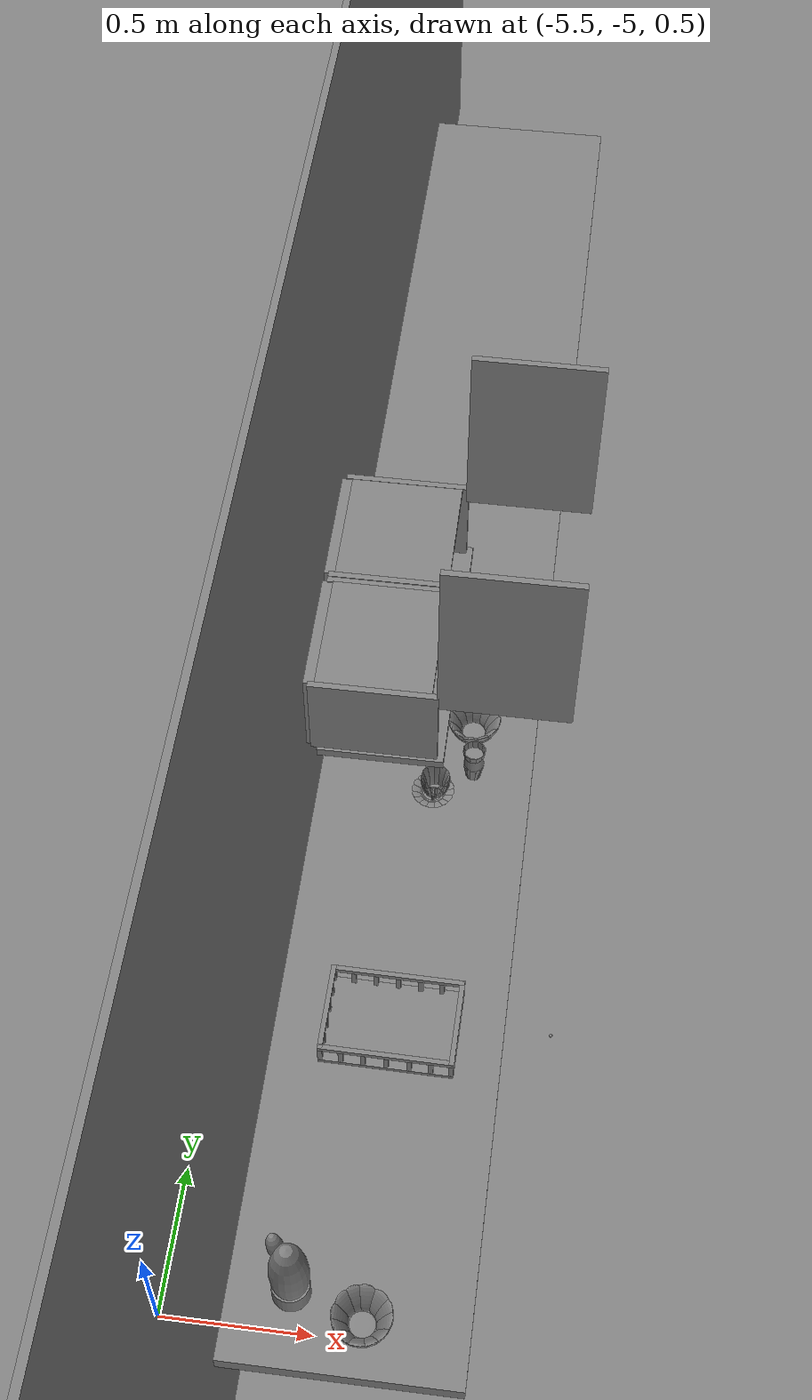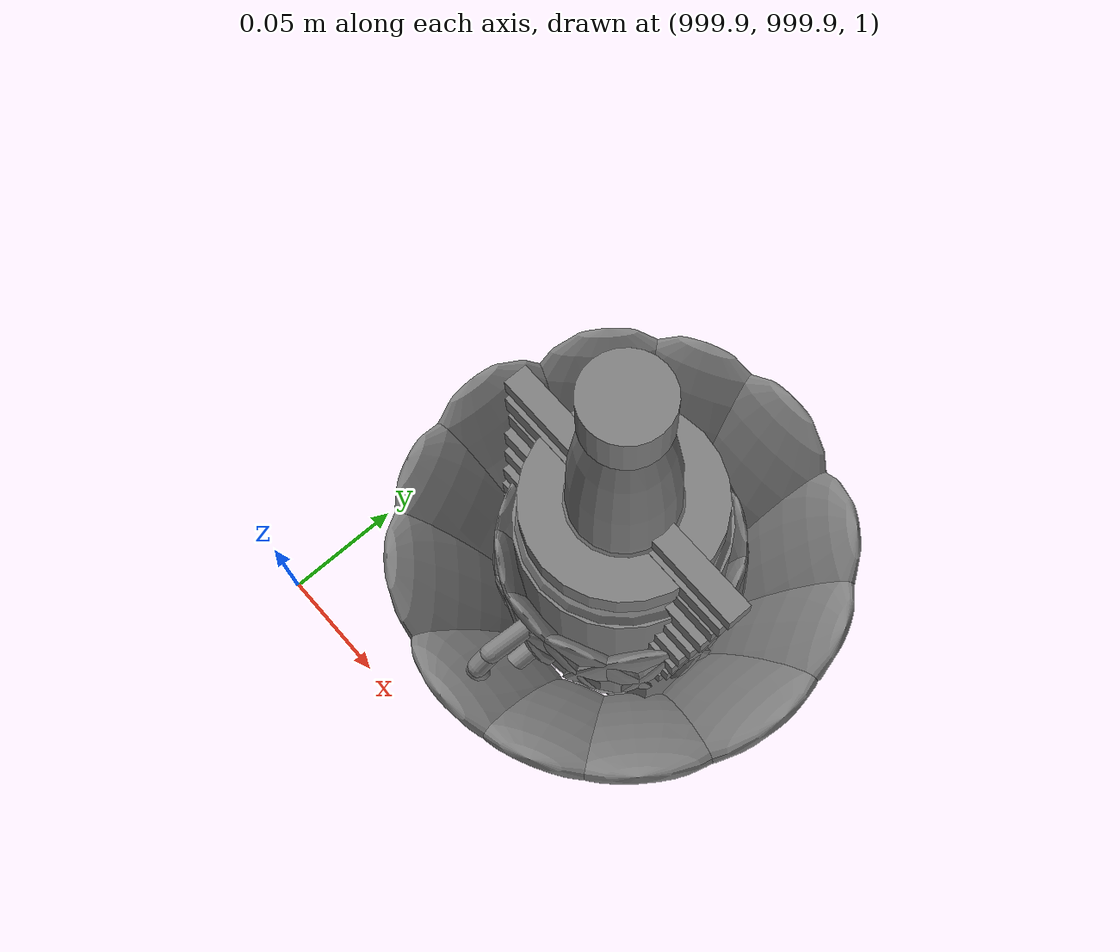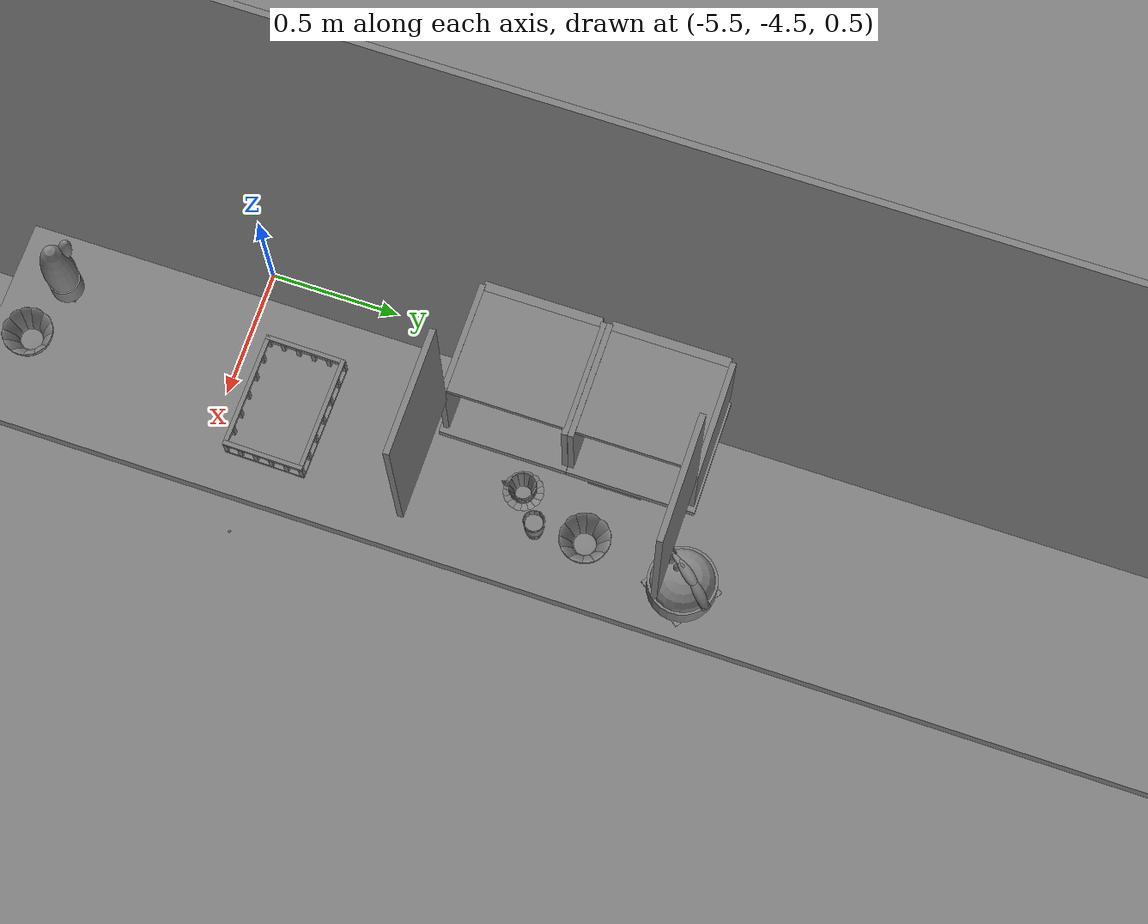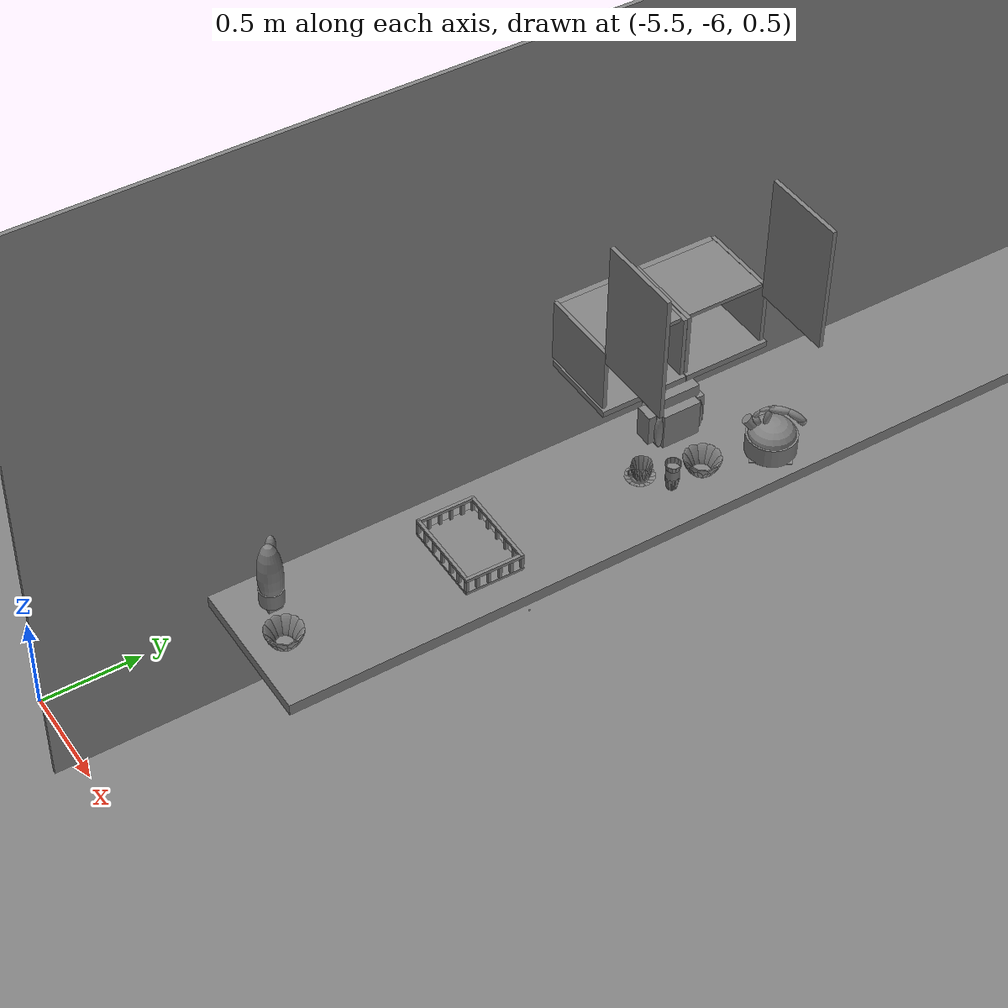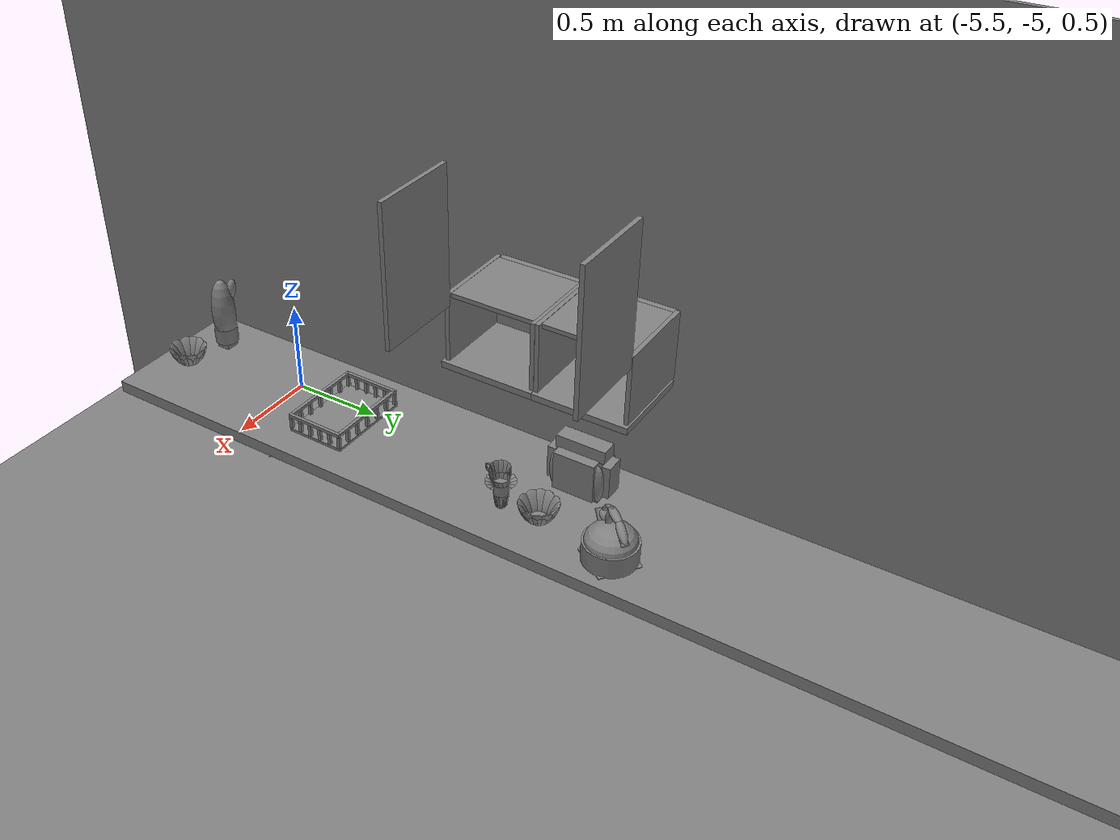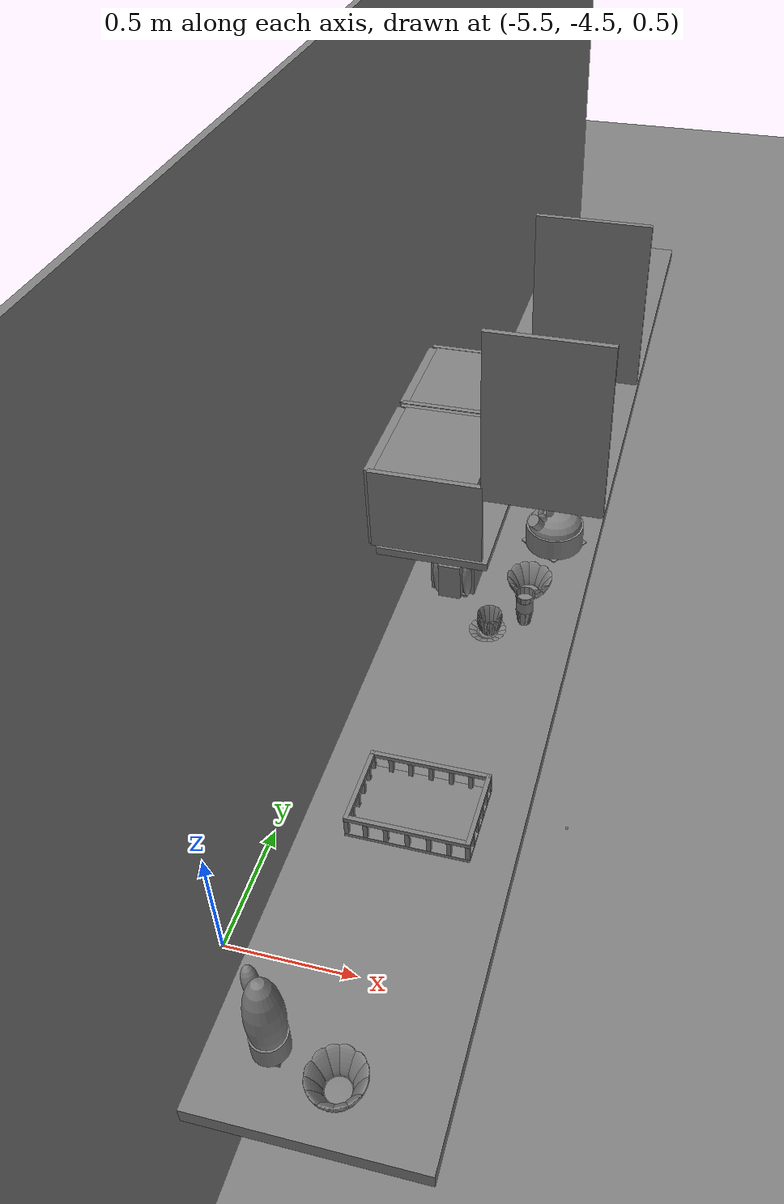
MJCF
<mujoco>
    <option gravity="0.000000000 0.000000000 -9.810000420" timestep="0.0049999999" integrator="implicitfast" density="9.8000002" viscosity="1.8000001e-05" noslip_iterations="10" iterations="100" sdf_iterations="50">
        <flag multiccd="disable"/>
    </option>
    <size memory="1000M"/>
    <compiler coordinate="local"/>
    <worldbody>
        <light cutoff="30" pos="0 1 1" dir="0 -1 -2"/>
        <light cutoff="30" pos="0 -1 1" dir="0 1 -2"/>
        <body pos="-5.046103477 -5.051773071 1.001502514" euler="0.000000000 0.000000000 0.000000000" name="Interactive Objcets_huapen">
            <geom contype="1" conaffinity="1" density="1000" type="ellipsoid" material="" rgba="0.500000000 0.500000000 0.500000000 1.000000000" solimp="0.899999976 0.949999988 0.001000000" friction="1.000000000 0.005000000 0.000100000" solref="0.020000000 1.000000000" margin="0" condim="3" group="0" pos="0.008062840 0.004346371 0.205056787" quat="1.000000000 0.000000000 0.000000000 0.000000000" size="0.059999999 0.059999999 0.180000007" name="Interactive Objcets_huapen_hua_60C698AC_56B8_4FC5_A21F_B8C0F6AAF1D0"/>
            <geom contype="1" conaffinity="1" density="1000" type="cylinder" material="" rgba="0.500000000 0.500000000 0.500000000 1.000000000" solimp="0.899999976 0.949999988 0.001000000" friction="1.000000000 0.005000000 0.000100000" solref="0.020000000 1.000000000" margin="0" condim="3" group="0" pos="0.008062840 0.003952026 0.080107450" quat="1.000000000 0.000000000 0.000000000 0.000000000" size="0.057999998 0.039999999 1.000000000" name="Interactive Objcets_huapen_hua_26DEEE38_8474_47E7_978B_B009AD8E4F50"/>
            <geom contype="1" conaffinity="1" density="1000" type="box" material="" rgba="0.500000000 0.500000000 0.500000000 1.000000000" solimp="0.899999976 0.949999988 0.001000000" friction="1.000000000 0.005000000 0.000100000" solref="0.020000000 1.000000000" margin="0" condim="3" group="0" pos="0.008062840 0.003952503 0.020566106" quat="1.000000000 0.000000000 0.000000000 0.000000000" size="0.035000000 0.035000000 0.020000000" name="Interactive Objcets_huapen_hua_9FD36183_1361_4038_9E07_9BBF9B18E487"/>
            <geom contype="1" conaffinity="1" density="1000" type="ellipsoid" material="" rgba="0.500000000 0.500000000 0.500000000 1.000000000" solimp="0.899999976 0.949999988 0.001000000" friction="1.000000000 0.005000000 0.000100000" solref="0.020000000 1.000000000" margin="0" condim="3" group="0" pos="-0.029900074 0.033599377 0.321917295" quat="0.992658079 -0.083605267 -0.087364964 0.002748166" size="0.025000000 0.025000000 0.059999999" name="Interactive Objcets_huapen_hua_D968DAFF_CB43_4947_8D61_1D7393C449C2"/>
            <freejoint name="Interactive Objcets_huapen"/>
        </body>
        <body pos="-4.279959202 -4.274725437 1.818652391" euler="-145.547607422 -37.044097900 152.164169312" mocap="true" name="spotlight3_SpotLight"/>
        <body pos="-4.111306190 -3.790724277 1.784271121" euler="49.984092712 -38.727416992 -63.318752289" mocap="true" name="spotlight6_SpotLight"/>
        <body pos="1000.000000000 1000.000000000 1.000000000" euler="0.000000000 0.000000000 0.000000000" name="openloong_gripper_2f85_fix_base_usda_bow_yellow_kps">
            <geom contype="1" conaffinity="1" density="1000" type="ellipsoid" material="" rgba="0.500000000 0.500000000 0.500000000 1.000000000" solimp="0.899999976 0.949999988 0.001000000" friction="1.000000000 0.005000000 0.000100000" solref="0.020000000 1.000000000" margin="0" condim="3" group="0" pos="-0.052185059 0.040283203 0.044118762" quat="0.919264615 -0.076883033 -0.225593656 -0.313287765" size="0.010000000 0.039999999 0.052000001" name="openloong_gripper_2f85_fix_base_usda_geom_03B37AA0_84D4_428D_93D1_4C4532E47E5A"/>
            <geom contype="1" conaffinity="1" density="1000" type="ellipsoid" material="" rgba="0.500000000 0.500000000 0.500000000 1.000000000" solimp="0.899999976 0.949999988 0.001000000" friction="1.000000000 0.005000000 0.000100000" solref="0.020000000 1.000000000" margin="0" condim="3" group="0" pos="-0.000061035 0.065979004 0.044118762" quat="0.687598765 -0.168314874 -0.168741167 -0.685860336" size="0.010000000 0.039999999 0.052000001" name="openloong_gripper_2f85_fix_base_usda_geom_3DC62BDE_8200_4440_AE34_FA6DF871B952"/>
            <geom contype="1" conaffinity="1" density="1000" type="box" material="" rgba="0.500000000 0.500000000 0.500000000 1.000000000" solimp="0.899999976 0.949999988 0.001000000" friction="1.000000000 0.005000000 0.000100000" solref="0.020000000 1.000000000" margin="0" condim="3" group="0" pos="0.000061035 0.000000000 -0.002001643" quat="1.000000000 0.000000000 0.000000000 0.000000000" size="0.029999999 0.029999999 0.002000000" name="openloong_gripper_2f85_fix_base_usda_geom_E0004666_1534_4435_8C70_FC8A2C550FFC"/>
            <geom contype="1" conaffinity="1" density="1000" type="ellipsoid" material="" rgba="0.500000000 0.500000000 0.500000000 1.000000000" solimp="0.899999976 0.949999988 0.001000000" friction="1.000000000 0.005000000 0.000100000" solref="0.020000000 1.000000000" margin="0" condim="3" group="0" pos="0.029418945 -0.059082031 0.044118762" quat="0.825555861 0.125530601 0.202597082 -0.511521280" size="0.010000000 0.039999999 0.052000001" name="openloong_gripper_2f85_fix_base_usda_geom_2987087C_6E96_4BD3_9722_8E816EC6917D"/>
            <geom contype="1" conaffinity="1" density="1000" type="ellipsoid" material="" rgba="0.500000000 0.500000000 0.500000000 1.000000000" solimp="0.899999976 0.949999988 0.001000000" friction="1.000000000 0.005000000 0.000100000" solref="0.020000000 1.000000000" margin="0" condim="3" group="0" pos="0.000244141 -0.065979004 0.044118762" quat="0.687598765 0.168314651 0.168741375 -0.685860336" size="0.010000000 0.039999999 0.052000001" name="openloong_gripper_2f85_fix_base_usda_geom_2B1E64BB_1008_454B_9BBD_C55080E06BA3"/>
            <geom contype="1" conaffinity="1" density="1000" type="ellipsoid" material="" rgba="0.500000000 0.500000000 0.500000000 1.000000000" solimp="0.899999976 0.949999988 0.001000000" friction="1.000000000 0.005000000 0.000100000" solref="0.020000000 1.000000000" margin="0" condim="3" group="0" pos="0.000061035 0.000000000 0.000446677" quat="1.000000000 0.000000000 0.000000000 0.000000000" size="0.039999999 0.039999999 0.002000000" name="openloong_gripper_2f85_fix_base_usda_geom_B6D12C0B_8070_4FE2_990E_73B326AB7301"/>
            <geom contype="1" conaffinity="1" density="1000" type="ellipsoid" material="" rgba="0.500000000 0.500000000 0.500000000 1.000000000" solimp="0.899999976 0.949999988 0.001000000" friction="1.000000000 0.005000000 0.000100000" solref="0.020000000 1.000000000" margin="0" condim="3" group="0" pos="0.059082031 0.029541016 0.044118762" quat="0.223252773 -0.231952220 -0.054787423 -0.945174456" size="0.010000000 0.039999999 0.052000001" name="openloong_gripper_2f85_fix_base_usda_geom_C02F382C_BD2F_46F0_A461_43FEEF3A23B2"/>
            <geom contype="1" conaffinity="1" density="1000" type="ellipsoid" material="" rgba="0.500000000 0.500000000 0.500000000 1.000000000" solimp="0.899999976 0.949999988 0.001000000" friction="1.000000000 0.005000000 0.000100000" solref="0.020000000 1.000000000" margin="0" condim="3" group="0" pos="0.000061035 0.000000000 0.007335305" quat="1.000000000 0.000000000 0.000000000 0.000000000" size="0.039999999 0.039999999 0.002000000" name="openloong_gripper_2f85_fix_base_usda_geom_40C6AAB9_223F_4827_AEB5_E51DC78C65CB"/>
            <geom contype="1" conaffinity="1" density="1000" type="ellipsoid" material="" rgba="0.500000000 0.500000000 0.500000000 1.000000000" solimp="0.899999976 0.949999988 0.001000000" friction="1.000000000 0.005000000 0.000100000" solref="0.020000000 1.000000000" margin="0" condim="3" group="0" pos="-0.029296875 0.059082031 0.044118762" quat="0.825555861 -0.125530809 -0.202596918 -0.511521280" size="0.010000000 0.039999999 0.052000001" name="openloong_gripper_2f85_fix_base_usda_geom_DCDFC315_2ED8_4411_B21E_6EFD15390ED7"/>
            <geom contype="1" conaffinity="1" density="1000" type="ellipsoid" material="" rgba="0.500000000 0.500000000 0.500000000 1.000000000" solimp="0.899999976 0.949999988 0.001000000" friction="1.000000000 0.005000000 0.000100000" solref="0.020000000 1.000000000" margin="0" condim="3" group="0" pos="0.040222168 0.052368164 0.044118762" quat="0.429593176 -0.213750049 -0.105424821 -0.871002972" size="0.010000000 0.039999999 0.052000001" name="openloong_gripper_2f85_fix_base_usda_geom_0F08E720_EC56_477F_B99E_4B08AA8F8CC5"/>
            <geom contype="1" conaffinity="1" density="1000" type="ellipsoid" material="" rgba="0.500000000 0.500000000 0.500000000 1.000000000" solimp="0.899999976 0.949999988 0.001000000" friction="1.000000000 0.005000000 0.000100000" solref="0.020000000 1.000000000" margin="0" condim="3" group="0" pos="0.066040039 0.000000000 0.044118762" quat="0.971183062 -0.000000156 0.238334835 0.000000030" size="0.010000000 0.039999999 0.052000001" name="openloong_gripper_2f85_fix_base_usda_geom_5A091A7F_ABE1_4A27_AD17_4F36639D5C5F"/>
            <geom contype="1" conaffinity="1" density="1000" type="ellipsoid" material="" rgba="0.500000000 0.500000000 0.500000000 1.000000000" solimp="0.899999976 0.949999988 0.001000000" friction="1.000000000 0.005000000 0.000100000" solref="0.020000000 1.000000000" margin="0" condim="3" group="0" pos="0.052307129 -0.040283203 0.044118762" quat="0.919264674 0.076882750 0.225593731 -0.313287705" size="0.010000000 0.039999999 0.052000001" name="openloong_gripper_2f85_fix_base_usda_geom_41574CE8_D326_4B0A_833D_936B9D961754"/>
            <geom contype="1" conaffinity="1" density="1000" type="ellipsoid" material="" rgba="0.500000000 0.500000000 0.500000000 1.000000000" solimp="0.899999976 0.949999988 0.001000000" friction="1.000000000 0.005000000 0.000100000" solref="0.020000000 1.000000000" margin="0" condim="3" group="0" pos="-0.065917969 0.000000000 0.044118762" quat="0.971183062 -0.000000142 -0.238334835 0.000000030" size="0.010000000 0.039999999 0.052000001" name="openloong_gripper_2f85_fix_base_usda_geom_119D2C31_A300_495E_B1CB_A47C8196904B"/>
            <geom contype="1" conaffinity="1" density="1000" type="ellipsoid" material="" rgba="0.500000000 0.500000000 0.500000000 1.000000000" solimp="0.899999976 0.949999988 0.001000000" friction="1.000000000 0.005000000 0.000100000" solref="0.020000000 1.000000000" margin="0" condim="3" group="0" pos="-0.058898926 -0.029541016 0.044118762" quat="0.223252758 0.231952101 0.054787733 -0.945174575" size="0.010000000 0.039999999 0.052000001" name="openloong_gripper_2f85_fix_base_usda_geom_DD5BD5C8_A4AE_4C24_8A92_19D5866D5EF6"/>
            <geom contype="1" conaffinity="1" density="1000" type="ellipsoid" material="" rgba="0.500000000 0.500000000 0.500000000 1.000000000" solimp="0.899999976 0.949999988 0.001000000" friction="1.000000000 0.005000000 0.000100000" solref="0.020000000 1.000000000" margin="0" condim="3" group="0" pos="-0.040100098 -0.052368164 0.044118762" quat="0.429593235 0.213749886 0.105425082 -0.871003032" size="0.010000000 0.039999999 0.052000001" name="openloong_gripper_2f85_fix_base_usda_geom_E5077A7F_0E82_4D92_BF6D_DD4B8ABAC2B7"/>
            <freejoint name="openloong_gripper_2f85_fix_base_usda_bow_yellow_kps_joint"/>
            <site size="0.005000000 0.005000000 0.005000000" rgba="0.500000000 0.500000000 0.500000000 1.000000000" pos="0.000000000 0.000000000 0.000000000" quat="0.999961913 0.008726534 0.000000000 0.000000000" group="0" type="sphere" name="openloong_gripper_2f85_fix_base_usda_bow_yellow_kps"/>
        </body>
        <body pos="1000.000000000 1000.000000000 1.000000000" euler="0.000000000 0.000000000 0.000000000" name="openloong_gripper_2f85_fix_base_usda_coffeecup_white_kps">
            <geom contype="1" conaffinity="1" density="1000" type="capsule" material="" rgba="0.500000000 0.500000000 0.500000000 1.000000000" solimp="0.899999976 0.949999988 0.001000000" friction="1.000000000 0.005000000 0.000100000" solref="0.020000000 1.000000000" margin="0" condim="3" group="0" pos="-0.000854492 -0.065795898 0.050029993" quat="0.343559504 -0.613204718 0.626912475 0.336047262" size="0.004000000 0.005000000 1.000000000" name="openloong_gripper_2f85_fix_base_usda_geom_E193F56A_D057_4C4C_BCFE_C9D683928B8F"/>
            <geom contype="1" conaffinity="1" density="1000" type="ellipsoid" material="" rgba="0.500000000 0.500000000 0.500000000 1.000000000" solimp="0.899999976 0.949999988 0.001000000" friction="1.000000000 0.005000000 0.000100000" solref="0.020000000 1.000000000" margin="0" condim="3" group="0" pos="-0.000793457 -0.038452148 0.048040152" quat="0.711656272 0.066323131 -0.067805752 0.696095467" size="0.005000000 0.029999999 0.048999999" name="openloong_gripper_2f85_fix_base_usda_geom_0B3C8C1A_73CE_4959_848F_2A4C7483232B"/>
            <geom contype="1" conaffinity="1" density="1000" type="ellipsoid" material="" rgba="0.500000000 0.500000000 0.500000000 1.000000000" solimp="0.899999976 0.949999988 0.001000000" friction="1.000000000 0.005000000 0.000100000" solref="0.020000000 1.000000000" margin="0" condim="3" group="0" pos="0.037719727 -0.001892090 0.048040152" quat="0.995387912 0.001371633 0.094835162 -0.014391154" size="0.005000000 0.029999999 0.048999999" name="openloong_gripper_2f85_fix_base_usda_geom_05A4E0C1_2A85_4791_A694_8BB2E3D1EAB4"/>
            <geom contype="1" conaffinity="1" density="1000" type="ellipsoid" material="" rgba="0.500000000 0.500000000 0.500000000 1.000000000" solimp="0.899999976 0.949999988 0.001000000" friction="1.000000000 0.005000000 0.000100000" solref="0.020000000 1.000000000" margin="0" condim="3" group="0" pos="0.033996582 0.015502930 0.048040152" quat="0.970659733 -0.021051638 0.092478797 0.220962167" size="0.005000000 0.029999999 0.048999999" name="openloong_gripper_2f85_fix_base_usda_geom_D3468E8F_D6AC_4447_A094_F74510C583D2"/>
            <geom contype="1" conaffinity="1" density="1000" type="box" material="" rgba="0.500000000 0.500000000 0.500000000 1.000000000" solimp="0.899999976 0.949999988 0.001000000" friction="1.000000000 0.005000000 0.000100000" solref="0.020000000 1.000000000" margin="0" condim="3" group="0" pos="0.000793457 -0.000183105 0.000156164" quat="0.714879215 0.000000000 0.000000000 0.699247897" size="0.020000000 0.020000000 0.002000000" name="openloong_gripper_2f85_fix_base_usda_geom_09B80C3D_1D1D_404D_BBE4_8E7E718E5080"/>
            <geom contype="1" conaffinity="1" density="1000" type="ellipsoid" material="" rgba="0.500000000 0.500000000 0.500000000 1.000000000" solimp="0.899999976 0.949999988 0.001000000" friction="1.000000000 0.005000000 0.000100000" solref="0.020000000 1.000000000" margin="0" condim="3" group="0" pos="-0.019409180 -0.033081055 0.048040152" quat="0.866879702 0.046630561 -0.082595348 0.489411235" size="0.005000000 0.029999999 0.048999999" name="openloong_gripper_2f85_fix_base_usda_geom_24BDFCC4_36EE_484B_8338_33DA65277630"/>
            <geom contype="1" conaffinity="1" density="1000" type="ellipsoid" material="" rgba="0.500000000 0.500000000 0.500000000 1.000000000" solimp="0.899999976 0.949999988 0.001000000" friction="1.000000000 0.005000000 0.000100000" solref="0.020000000 1.000000000" margin="0" condim="3" group="0" pos="-0.016052246 0.033264160 0.048040152" quat="0.840792537 -0.050782297 -0.080109790 -0.532983541" size="0.005000000 0.029999999 0.048999999" name="openloong_gripper_2f85_fix_base_usda_geom_0CB7D09E_AE14_4394_8F33_0C2857DC9CC9"/>
            <geom contype="1" conaffinity="1" density="1000" type="capsule" material="" rgba="0.500000000 0.500000000 0.500000000 1.000000000" solimp="0.899999976 0.949999988 0.001000000" friction="1.000000000 0.005000000 0.000100000" solref="0.020000000 1.000000000" margin="0" condim="3" group="0" pos="-0.000549316 -0.053527832 0.046825886" quat="0.505496025 -0.494442940 0.505495846 0.494442940" size="0.004000000 0.005000000 1.000000000" name="openloong_gripper_2f85_fix_base_usda_geom_42C4E0CD_E4D9_463B_BB35_98018DD3C361"/>
            <geom contype="1" conaffinity="1" density="1000" type="ellipsoid" material="" rgba="0.500000000 0.500000000 0.500000000 1.000000000" solimp="0.899999976 0.949999988 0.001000000" friction="1.000000000 0.005000000 0.000100000" solref="0.020000000 1.000000000" margin="0" condim="3" group="0" pos="-0.032104492 0.018920898 0.048040152" quat="0.958129764 -0.025742561 -0.091288343 -0.270168930" size="0.005000000 0.029999999 0.048999999" name="openloong_gripper_2f85_fix_base_usda_geom_1E0BD0E7_A348_4018_BE7C_77BDCAFFBB8B"/>
            <geom contype="1" conaffinity="1" density="1000" type="ellipsoid" material="" rgba="0.500000000 0.500000000 0.500000000 1.000000000" solimp="0.899999976 0.949999988 0.001000000" friction="1.000000000 0.005000000 0.000100000" solref="0.020000000 1.000000000" margin="0" condim="3" group="0" pos="-0.037597656 0.000305176 0.048040152" quat="0.995387554 -0.001371440 -0.094839431 -0.014389008" size="0.005000000 0.029999999 0.048999999" name="openloong_gripper_2f85_fix_base_usda_geom_4DC97624_7FAD_4E4B_A772_35501B4D55BA"/>
            <geom contype="1" conaffinity="1" density="1000" type="capsule" material="" rgba="0.500000000 0.500000000 0.500000000 1.000000000" solimp="0.899999976 0.949999988 0.001000000" friction="1.000000000 0.005000000 0.000100000" solref="0.020000000 1.000000000" margin="0" condim="3" group="0" pos="-0.000366211 -0.043762207 0.044118762" quat="0.260488123 -0.651174724 0.665731549 0.254792154" size="0.004000000 0.003000000 1.000000000" name="openloong_gripper_2f85_fix_base_usda_geom_C2717611_A638_4536_9B82_F711BAC54115"/>
            <geom contype="1" conaffinity="1" density="1000" type="capsule" material="" rgba="0.500000000 0.500000000 0.500000000 1.000000000" solimp="0.899999976 0.949999988 0.001000000" friction="1.000000000 0.005000000 0.000100000" solref="0.020000000 1.000000000" margin="0" condim="3" group="0" pos="-0.000915527 -0.068542480 0.082936406" quat="0.624995589 -0.339446366 0.347034454 0.611329615" size="0.004000000 0.004000000 1.000000000" name="openloong_gripper_2f85_fix_base_usda_geom_251BD5DA_5A60_4556_B686_31805D1EFAD2"/>
            <geom contype="1" conaffinity="1" density="1000" type="ellipsoid" material="" rgba="0.500000000 0.500000000 0.500000000 1.000000000" solimp="0.899999976 0.949999988 0.001000000" friction="1.000000000 0.005000000 0.000100000" solref="0.020000000 1.000000000" margin="0" condim="3" group="0" pos="0.016113281 -0.034851074 0.048040152" quat="0.840793252 0.050779939 0.080106191 -0.532983422" size="0.005000000 0.029999999 0.048999999" name="openloong_gripper_2f85_fix_base_usda_geom_122F72B5_29F9_4772_B03F_D1B5807F3F9E"/>
            <geom contype="1" conaffinity="1" density="1000" type="ellipsoid" material="" rgba="0.500000000 0.500000000 0.500000000 1.000000000" solimp="0.899999976 0.949999988 0.001000000" friction="1.000000000 0.005000000 0.000100000" solref="0.020000000 1.000000000" margin="0" condim="3" group="0" pos="0.000854492 0.036865234 0.048040152" quat="0.711656570 -0.066320375 0.067802906 0.696095705" size="0.005000000 0.029999999 0.048999999" name="openloong_gripper_2f85_fix_base_usda_geom_66F0495A_F27B_4C25_A715_916BD7ADFA53"/>
            <geom contype="1" conaffinity="1" density="1000" type="ellipsoid" material="" rgba="0.500000000 0.500000000 0.500000000 1.000000000" solimp="0.899999976 0.949999988 0.001000000" friction="1.000000000 0.005000000 0.000100000" solref="0.020000000 1.000000000" margin="0" condim="3" group="0" pos="-0.033935547 -0.017089844 0.048040152" quat="0.970659137 0.021052625 -0.092483103 0.220962465" size="0.005000000 0.029999999 0.048999999" name="openloong_gripper_2f85_fix_base_usda_geom_B43AD4AA_5D17_4931_A83C_AB43E23C13BA"/>
            <geom contype="1" conaffinity="1" density="1000" type="ellipsoid" material="" rgba="0.500000000 0.500000000 0.500000000 1.000000000" solimp="0.899999976 0.949999988 0.001000000" friction="1.000000000 0.005000000 0.000100000" solref="0.020000000 1.000000000" margin="0" condim="3" group="0" pos="0.019531250 0.031494141 0.048040152" quat="0.866880119 -0.046628602 0.082591817 0.489411235" size="0.005000000 0.029999999 0.048999999" name="openloong_gripper_2f85_fix_base_usda_geom_213C07AD_0848_42D4_8B11_452105875AE2"/>
            <geom contype="1" conaffinity="1" density="1000" type="ellipsoid" material="" rgba="0.500000000 0.500000000 0.500000000 1.000000000" solimp="0.899999976 0.949999988 0.001000000" friction="1.000000000 0.005000000 0.000100000" solref="0.020000000 1.000000000" margin="0" condim="3" group="0" pos="0.032165527 -0.020507812 0.048040152" quat="0.958128154 0.025740955 0.091285400 -0.270175666" size="0.005000000 0.029999999 0.048999999" name="openloong_gripper_2f85_fix_base_usda_geom_229CB611_A7D0_49FA_9748_0135004D2504"/>
            <geom contype="1" conaffinity="1" density="1000" type="capsule" material="" rgba="0.500000000 0.500000000 0.500000000 1.000000000" solimp="0.899999976 0.949999988 0.001000000" friction="1.000000000 0.005000000 0.000100000" solref="0.020000000 1.000000000" margin="0" condim="3" group="0" pos="-0.000610352 -0.056823730 0.083572865" quat="0.452654332 -0.541215360 0.553313971 0.442756712" size="0.004000000 0.009000000 1.000000000" name="openloong_gripper_2f85_fix_base_usda_geom_B99A2404_836C_47AF_8B6E_DB2D0C34A748"/>
            <geom contype="1" conaffinity="1" density="1000" type="ellipsoid" material="" rgba="0.500000000 0.500000000 0.500000000 1.000000000" solimp="0.899999976 0.949999988 0.001000000" friction="1.000000000 0.005000000 0.000100000" solref="0.020000000 1.000000000" margin="0" condim="3" group="0" pos="0.000061035 -0.000183105 0.001848221" quat="0.714879215 0.000000000 0.000000000 0.699247897" size="0.029999999 0.029999999 0.001000000" name="openloong_gripper_2f85_fix_base_usda_geom_6389A01C_DC19_4A42_A351_7BED7EEB7F6A"/>
            <geom contype="1" conaffinity="1" density="1000" type="capsule" material="" rgba="0.500000000 0.500000000 0.500000000 1.000000000" solimp="0.899999976 0.949999988 0.001000000" friction="1.000000000 0.005000000 0.000100000" solref="0.020000000 1.000000000" margin="0" condim="3" group="0" pos="-0.000976562 -0.071838379 0.066101432" quat="0.031849027 -0.698553741 0.714169443 0.031152546" size="0.004000000 0.012000000 1.000000000" name="openloong_gripper_2f85_fix_base_usda_geom_F8C6F01A_0658_477C_87B4_656E7F481C15"/>
            <freejoint name="openloong_gripper_2f85_fix_base_usda_coffeecup_white_kps_joint"/>
            <site size="0.005000000 0.005000000 0.005000000" rgba="0.500000000 0.500000000 0.500000000 1.000000000" pos="0.000000000 0.000000000 0.000000000" quat="0.999961913 0.008726534 0.000000000 0.000000000" group="0" type="sphere" name="openloong_gripper_2f85_fix_base_usda_coffeecup_white_kps"/>
        </body>
        <body pos="1000.000000000 1000.000000000 1.000000000" euler="0.000000000 0.000000000 0.000000000" name="openloong_gripper_2f85_fix_base_usda_salt">
            <geom contype="1" conaffinity="1" density="1000" type="box" material="" rgba="0.500000000 0.500000000 0.500000000 1.000000000" solimp="0.899999976 0.949999988 0.001000000" friction="1.000000000 0.005000000 0.000100000" solref="0.020000000 1.000000000" margin="0" condim="3" group="0" pos="0.000305176 0.000000000 0.084862232" quat="1.000000000 0.000000000 0.000000000 0.000000000" size="0.048999999 0.018999999 0.005000000" name="openloong_gripper_2f85_fix_base_usda_geom_CD128D92_5C99_4A85_9867_BEE9A000A5E3"/>
            <geom contype="1" conaffinity="1" density="1000" type="box" material="" rgba="0.500000000 0.500000000 0.500000000 1.000000000" solimp="0.899999976 0.949999988 0.001000000" friction="1.000000000 0.005000000 0.000100000" solref="0.020000000 1.000000000" margin="0" condim="3" group="0" pos="0.000305176 0.000000000 0.104564309" quat="1.000000000 0.000000000 0.000000000 0.000000000" size="0.052000001 0.014000000 0.005000000" name="openloong_gripper_2f85_fix_base_usda_geom_31DC0DFA_C027_44C5_859C_32AE8191AE6C"/>
            <geom contype="1" conaffinity="1" density="1000" type="box" material="" rgba="0.500000000 0.500000000 0.500000000 1.000000000" solimp="0.899999976 0.949999988 0.001000000" friction="1.000000000 0.005000000 0.000100000" solref="0.020000000 1.000000000" margin="0" condim="3" group="0" pos="0.000305176 0.000000000 0.114487171" quat="1.000000000 0.000000000 0.000000000 0.000000000" size="0.054000001 0.011500000 0.005000000" name="openloong_gripper_2f85_fix_base_usda_geom_DD19531D_0794_4BF4_B75C_7E214BF86977"/>
            <geom contype="1" conaffinity="1" density="1000" type="box" material="" rgba="0.500000000 0.500000000 0.500000000 1.000000000" solimp="0.899999976 0.949999988 0.001000000" friction="1.000000000 0.005000000 0.000100000" solref="0.020000000 1.000000000" margin="0" condim="3" group="0" pos="0.000305176 0.000000000 0.075103164" quat="1.000000000 0.000000000 0.000000000 0.000000000" size="0.048000000 0.020000000 0.005000000" name="openloong_gripper_2f85_fix_base_usda_geom_5D42D68B_CD9A_4042_A07A_04B8BC947189"/>
            <geom contype="1" conaffinity="1" density="1000" type="box" material="" rgba="0.500000000 0.500000000 0.500000000 1.000000000" solimp="0.899999976 0.949999988 0.001000000" friction="1.000000000 0.005000000 0.000100000" solref="0.020000000 1.000000000" margin="0" condim="3" group="0" pos="0.000305176 0.000000000 0.134892464" quat="1.000000000 0.000000000 0.000000000 0.000000000" size="0.057000000 0.007000000 0.005000000" name="openloong_gripper_2f85_fix_base_usda_geom_84CBDFF3_9172_48B1_AF1F_5401485B4BF0"/>
            <geom contype="1" conaffinity="1" density="1000" type="box" material="" rgba="0.500000000 0.500000000 0.500000000 1.000000000" solimp="0.899999976 0.949999988 0.001000000" friction="1.000000000 0.005000000 0.000100000" solref="0.020000000 1.000000000" margin="0" condim="3" group="0" pos="0.000305176 0.000000000 0.094920278" quat="1.000000000 0.000000000 0.000000000 0.000000000" size="0.050000001 0.017000001 0.005000000" name="openloong_gripper_2f85_fix_base_usda_geom_E8B4C83D_B198_4306_89A0_B4841C61B12A"/>
            <geom contype="1" conaffinity="1" density="1000" type="box" material="" rgba="0.500000000 0.500000000 0.500000000 1.000000000" solimp="0.899999976 0.949999988 0.001000000" friction="1.000000000 0.005000000 0.000100000" solref="0.020000000 1.000000000" margin="0" condim="3" group="0" pos="0.000305176 0.000000000 0.065204859" quat="1.000000000 0.000000000 0.000000000 0.000000000" size="0.045000002 0.021000000 0.005000000" name="openloong_gripper_2f85_fix_base_usda_geom_929CCB49_005C_4290_ACCD_375E0F24CF24"/>
            <geom contype="1" conaffinity="1" density="1000" type="box" material="" rgba="0.500000000 0.500000000 0.500000000 1.000000000" solimp="0.899999976 0.949999988 0.001000000" friction="1.000000000 0.005000000 0.000100000" solref="0.020000000 1.000000000" margin="0" condim="3" group="0" pos="0.000305176 0.000000000 0.144135714" quat="1.000000000 0.000000000 0.000000000 0.000000000" size="0.059000000 0.005000000 0.004000000" name="openloong_gripper_2f85_fix_base_usda_geom_DACDE758_2EB1_4EB1_82CC_FE83BF03B3CE"/>
            <geom contype="1" conaffinity="1" density="1000" type="box" material="" rgba="0.500000000 0.500000000 0.500000000 1.000000000" solimp="0.899999976 0.949999988 0.001000000" friction="1.000000000 0.005000000 0.000100000" solref="0.020000000 1.000000000" margin="0" condim="3" group="0" pos="0.000000000 0.000000000 0.031593561" quat="1.000000000 0.000000000 0.000000000 0.000000000" size="0.041999999 0.024000000 0.029999999" name="openloong_gripper_2f85_fix_base_usda_geom_1278742A_339F_457C_9356_747B3F915167"/>
            <geom contype="1" conaffinity="1" density="1000" type="box" material="" rgba="0.500000000 0.500000000 0.500000000 1.000000000" solimp="0.899999976 0.949999988 0.001000000" friction="1.000000000 0.005000000 0.000100000" solref="0.020000000 1.000000000" margin="0" condim="3" group="0" pos="0.000305176 0.000000000 0.124608755" quat="1.000000000 0.000000000 0.000000000 0.000000000" size="0.055000000 0.008000000 0.005000000" name="openloong_gripper_2f85_fix_base_usda_geom_3CB8F0EB_5D3F_4E5C_B8D9_751417BD77A1"/>
            <freejoint name="openloong_gripper_2f85_fix_base_usda_salt_joint"/>
            <site size="0.005000000 0.005000000 0.005000000" rgba="0.500000000 0.500000000 0.500000000 1.000000000" pos="0.000000000 0.000000000 0.000000000" quat="1.000000000 0.000000000 0.000000000 0.000000000" group="0" type="sphere" name="openloong_gripper_2f85_fix_base_usda_saltsite"/>
        </body>
        <body pos="1000.000000000 1000.000000000 1.000000000" euler="0.000000000 0.000000000 0.000000000" name="openloong_gripper_2f85_fix_base_usda_bottle_red">
            <geom contype="1" conaffinity="1" density="1000" type="ellipsoid" material="" rgba="0.500000000 0.500000000 0.500000000 1.000000000" solimp="0.899999976 0.949999988 0.001000000" friction="1.000000000 0.005000000 0.000100000" solref="0.020000000 1.000000000" margin="0" condim="3" group="0" pos="0.000000000 0.000000000 0.144284487" quat="1.000000000 0.000000000 0.000000000 0.000000000" size="0.021000000 0.021000000 0.079999998" name="openloong_gripper_2f85_fix_base_usda_geom_AB35B633_A3CB_4F05_8490_8B414BC8E7B1"/>
            <geom contype="1" conaffinity="1" density="1000" type="cylinder" material="" rgba="0.500000000 0.500000000 0.500000000 1.000000000" solimp="0.899999976 0.949999988 0.001000000" friction="1.000000000 0.005000000 0.000100000" solref="0.020000000 1.000000000" margin="0" condim="3" group="0" pos="0.000000000 0.000000000 0.220618963" quat="1.000000000 0.000000000 0.000000000 0.000000000" size="0.016000001 0.010000000 1.000000000" name="openloong_gripper_2f85_fix_base_usda_geom_094C252C_E8B0_49E1_9966_814C2CA65660"/>
            <geom contype="1" conaffinity="1" density="1000" type="ellipsoid" material="" rgba="0.500000000 0.500000000 0.500000000 1.000000000" solimp="0.899999976 0.949999988 0.001000000" friction="1.000000000 0.005000000 0.000100000" solref="0.020000000 1.000000000" margin="0" condim="3" group="0" pos="0.000000000 0.000000000 0.118945479" quat="1.000000000 0.000000000 0.000000000 0.000000000" size="0.030999999 0.030999999 0.029999999" name="openloong_gripper_2f85_fix_base_usda_geom_95934147_CC28_473D_9495_08E96C3B00C2"/>
            <geom contype="1" conaffinity="1" density="1000" type="box" material="" rgba="0.500000000 0.500000000 0.500000000 1.000000000" solimp="0.899999976 0.949999988 0.001000000" friction="1.000000000 0.005000000 0.000100000" solref="0.020000000 1.000000000" margin="0" condim="3" group="0" pos="0.000000000 0.000000000 0.002189159" quat="1.000000000 0.000000000 0.000000000 0.000000000" size="0.020000000 0.020000000 0.003000000" name="openloong_gripper_2f85_fix_base_usda_geom_C60440A1_97CA_4906_A5B3_06F6EE1C82F0"/>
            <geom contype="1" conaffinity="1" density="1000" type="cylinder" material="" rgba="0.500000000 0.500000000 0.500000000 1.000000000" solimp="0.899999976 0.949999988 0.001000000" friction="1.000000000 0.005000000 0.000100000" solref="0.020000000 1.000000000" margin="0" condim="3" group="0" pos="0.000000000 -0.000366211 0.060884237" quat="1.000000000 0.000000000 0.000000000 0.000000000" size="0.030999999 0.057999998 1.000000000" name="openloong_gripper_2f85_fix_base_usda_geom_9BD143DA_C7D2_4566_A787_FCAC3431529F"/>
            <freejoint name="openloong_gripper_2f85_fix_base_usda_bottle_red_joint"/>
            <site size="0.005000000 0.005000000 0.005000000" rgba="0.500000000 0.500000000 0.500000000 1.000000000" pos="0.000000000 0.000000000 0.000000000" quat="0.999961913 0.008726535 0.000000000 0.000000000" group="0" type="sphere" name="openloong_gripper_2f85_fix_base_usda_bottle_redsite"/>
        </body>
        <body pos="-3.937113285 -4.088953495 1.800938964" euler="-166.486846924 52.115566254 11.054606438" mocap="true" name="spotlight5_SpotLight"/>
        <body pos="1000.000000000 1000.000000000 1.000000000" euler="0.000000000 0.000000000 0.000000000" name="openloong_gripper_2f85_fix_base_usda_jar_01">
            <geom contype="1" conaffinity="1" density="1000" type="box" material="" rgba="0.500000000 0.500000000 0.500000000 1.000000000" solimp="0.899999976 0.949999988 0.001000000" friction="1.000000000 0.005000000 0.000100000" solref="0.020000000 1.000000000" margin="0" condim="3" group="0" pos="0.000000000 0.000000000 0.006158113" quat="1.000000000 0.000000000 0.000000000 0.000000000" size="0.020000000 0.020000000 0.005000000" name="openloong_gripper_2f85_fix_base_usda_geom_04108FEE_2CF6_426C_8819_D21EC19517BF"/>
            <geom contype="1" conaffinity="1" density="1000" type="cylinder" material="" rgba="0.500000000 0.500000000 0.500000000 1.000000000" solimp="0.899999976 0.949999988 0.001000000" friction="1.000000000 0.005000000 0.000100000" solref="0.020000000 1.000000000" margin="0" condim="3" group="0" pos="0.000000000 0.000000000 0.062744498" quat="1.000000000 0.000000000 0.000000000 0.000000000" size="0.041000001 0.052999999 1.000000000" name="openloong_gripper_2f85_fix_base_usda_geom_BA630B81_773F_45A3_BD99_CEFD8ACE8EE2"/>
            <geom contype="1" conaffinity="1" density="1000" type="ellipsoid" material="" rgba="0.500000000 0.500000000 0.500000000 1.000000000" solimp="0.899999976 0.949999988 0.001000000" friction="1.000000000 0.005000000 0.000100000" solref="0.020000000 1.000000000" margin="0" condim="3" group="0" pos="0.000000000 0.000000000 0.122252703" quat="1.000000000 0.000000000 0.000000000 0.000000000" size="0.035999998 0.035999998 0.010000000" name="openloong_gripper_2f85_fix_base_usda_geom_77972046_EC93_443E_98D4_366314634A7C"/>
            <geom contype="1" conaffinity="1" density="1000" type="cylinder" material="" rgba="0.500000000 0.500000000 0.500000000 1.000000000" solimp="0.899999976 0.949999988 0.001000000" friction="1.000000000 0.005000000 0.000100000" solref="0.020000000 1.000000000" margin="0" condim="3" group="0" pos="0.000000000 0.000000000 0.015747190" quat="1.000000000 0.000000000 0.000000000 0.000000000" size="0.035000000 0.010000000 1.000000000" name="openloong_gripper_2f85_fix_base_usda_geom_3A7D6EDB_8F23_4706_B9F2_2CC18A7F82A0"/>
            <geom contype="1" conaffinity="1" density="1000" type="ellipsoid" material="" rgba="0.500000000 0.500000000 0.500000000 1.000000000" solimp="0.899999976 0.949999988 0.001000000" friction="1.000000000 0.005000000 0.000100000" solref="0.020000000 1.000000000" margin="0" condim="3" group="0" pos="0.000000000 0.000000000 0.115815401" quat="1.000000000 0.000000000 0.000000000 0.000000000" size="0.039999999 0.039999999 0.010000000" name="openloong_gripper_2f85_fix_base_usda_geom_1628632F_DC21_4512_B68D_4B83487FA53A"/>
            <geom contype="1" conaffinity="1" density="1000" type="cylinder" material="" rgba="0.500000000 0.500000000 0.500000000 1.000000000" solimp="0.899999976 0.949999988 0.001000000" friction="1.000000000 0.005000000 0.000100000" solref="0.020000000 1.000000000" margin="0" condim="3" group="0" pos="0.000000000 0.000000000 0.133183479" quat="1.000000000 0.000000000 0.000000000 0.000000000" size="0.037999999 0.006500000 1.000000000" name="openloong_gripper_2f85_fix_base_usda_geom_43E6CEE4_D2DD_4042_BD3F_F36D805EBEC5"/>
            <freejoint name="openloong_gripper_2f85_fix_base_usda_jar_01_joint"/>
            <site size="0.005000000 0.005000000 0.005000000" rgba="0.500000000 0.500000000 0.500000000 1.000000000" pos="0.000000000 0.000000000 0.000000000" quat="1.000000000 0.000000000 0.000000000 0.000000000" group="0" type="sphere" name="openloong_gripper_2f85_fix_base_usda_jar_01site"/>
        </body>
        <body pos="0.000000000 0.000000000 0.000000000" euler="0.000000000 0.000000000 0.000000000" name="Static Objcets_Static Objcets">
            <geom contype="1" conaffinity="1" density="1000" type="box" material="" rgba="0.500000000 0.500000000 0.500000000 1.000000000" solimp="0.899999976 0.949999988 0.001000000" friction="1.000000000 0.005000000 0.000100000" solref="0.020000000 1.000000000" margin="0" condim="3" group="0" pos="-4.999745846 -3.497932911 1.764780521" quat="0.707107067 0.707106471 0.000000000 0.000000000" size="0.200000003 0.159999996 0.010000000" name="Static Objcets_geom_77E74EE4_3038_40B6_91B4_1B3A18584371"/>
            <geom contype="1" conaffinity="1" density="1000" type="box" material="" rgba="0.500000000 0.500000000 0.500000000 1.000000000" solimp="0.899999976 0.949999988 0.001000000" friction="1.000000000 0.005000000 0.000100000" solref="0.020000000 1.000000000" margin="0" condim="3" group="0" pos="-4.979488373 -3.297635794 1.591412544" quat="0.707106829 0.707106709 0.000000000 0.000000000" size="0.200000003 0.015000000 0.219999999" name="Static Objcets_geom_09BD169A_937D_4A0C_9DB7_6FB9A78E97C2"/>
            <geom contype="1" conaffinity="1" density="1000" type="box" material="" rgba="0.500000000 0.500000000 0.500000000 1.000000000" solimp="0.899999976 0.949999988 0.001000000" friction="1.000000000 0.005000000 0.000100000" solref="0.020000000 1.000000000" margin="0" condim="3" group="0" pos="-4.999745846 -3.087441683 1.763863802" quat="0.707107067 0.707106471 0.000000000 0.000000000" size="0.200000003 0.159999996 0.010000000" name="Static Objcets_geom_057CF455_8AA9_4F54_B472_366DFE076962"/>
            <geom contype="1" conaffinity="1" density="1000" type="box" material="" rgba="0.500000000 0.500000000 0.500000000 1.000000000" solimp="0.899999976 0.949999988 0.001000000" friction="1.000000000 0.005000000 0.000100000" solref="0.020000000 1.000000000" margin="0" condim="3" group="0" pos="-5.189302921 -3.293644905 1.760152459" quat="0.707107067 0.707106471 0.000000000 0.000000000" size="0.025000000 0.159999996 0.200000003" name="Static Objcets_geom_2F4BB5B9_581A_476F_BC47_476EEC52FCF0"/>
            <geom contype="1" conaffinity="1" density="1000" type="box" material="" rgba="0.500000000 0.500000000 0.500000000 1.000000000" solimp="0.899999976 0.949999988 0.001000000" friction="1.000000000 0.005000000 0.000100000" solref="0.020000000 1.000000000" margin="0" condim="3" group="0" pos="-5.000125408 -3.294431210 1.913951039" quat="0.707107067 0.707106471 0.000000000 0.000000000" size="0.180000007 0.010000000 0.200000003" name="Static Objcets_geom_930880A1_AC56_432B_8501_2695ED5FF3A4"/>
            <geom contype="1" conaffinity="1" density="1000" type="box" material="" rgba="0.500000000 0.500000000 0.500000000 1.000000000" solimp="0.899999976 0.949999988 0.001000000" friction="1.000000000 0.005000000 0.000100000" solref="0.020000000 1.000000000" margin="0" condim="3" group="0" pos="-5.000125408 -2.861802340 1.913950682" quat="0.707107067 0.707106471 0.000000000 0.000000000" size="0.180000007 0.010000000 0.200000003" name="Static Objcets_geom_3EAC485B_A153_4D0D_8AF0_2D094CC257D9"/>
            <geom contype="1" conaffinity="1" density="1000" type="box" material="" rgba="0.500000000 0.500000000 0.500000000 1.000000000" solimp="0.899999976 0.949999988 0.001000000" friction="1.000000000 0.005000000 0.000100000" solref="0.020000000 1.000000000" margin="0" condim="3" group="0" pos="-4.979488373 -2.855390549 1.591412187" quat="0.707106709 0.707106769 0.000000000 0.000000000" size="0.200000003 0.015000000 0.219999999" name="Static Objcets_geom_643DE011_F28F_43B4_8872_2F03DBDF336D"/>
            <geom contype="1" conaffinity="1" density="1000" type="box" material="" rgba="0.500000000 0.500000000 0.500000000 1.000000000" solimp="0.899999976 0.949999988 0.001000000" friction="1.000000000 0.005000000 0.000100000" solref="0.020000000 1.000000000" margin="0" condim="3" group="0" pos="-4.999745846 -3.066934109 1.765979409" quat="0.707107067 0.707106471 0.000000000 0.000000000" size="0.200000003 0.159999996 0.010000000" name="Static Objcets_geom_7CB55352_A815_480E_8A51_FA56D748C981"/>
            <geom contype="1" conaffinity="1" density="1000" type="box" material="" rgba="0.500000000 0.500000000 0.500000000 1.000000000" solimp="0.899999976 0.949999988 0.001000000" friction="1.000000000 0.005000000 0.000100000" solref="0.020000000 1.000000000" margin="0" condim="3" group="0" pos="-4.999745846 -2.653569937 1.764779806" quat="0.707107067 0.707106471 0.000000000 0.000000000" size="0.200000003 0.159999996 0.010000000" name="Static Objcets_geom_0D4BE5D0_BDE3_417F_8E2B_C3EB6B44A4BD"/>
            <geom contype="1" conaffinity="1" density="1000" type="box" material="" rgba="0.500000000 0.500000000 0.500000000 1.000000000" solimp="0.899999976 0.949999988 0.001000000" friction="1.000000000 0.005000000 0.000100000" solref="0.020000000 1.000000000" margin="0" condim="3" group="0" pos="-5.189302921 -2.861564636 1.760152102" quat="0.707107067 0.707106471 0.000000000 0.000000000" size="0.025000000 0.159999996 0.200000003" name="Static Objcets_geom_43F73496_3802_4CCA_9742_BC2D6BA759CA"/>
            <geom contype="1" conaffinity="1" density="1000" type="box" material="" rgba="0.500000000 0.500000000 0.500000000 1.000000000" solimp="0.899999976 0.949999988 0.001000000" friction="1.000000000 0.005000000 0.000100000" solref="0.020000000 1.000000000" margin="0" condim="3" group="0" pos="-4.873187065 -2.461376429 0.977675021" quat="0.707107067 0.707106471 0.000000000 0.000000000" size="0.370000005 0.029999999 2.799999952" name="Static Objcets_geom_FA4B4E93_D48E_4D5D_8959_FDCA4B425C74"/>
            <geom contype="1" conaffinity="1" density="1000" type="box" material="" rgba="0.500000000 0.500000000 0.500000000 1.000000000" solimp="0.899999976 0.949999988 0.001000000" friction="1.000000000 0.005000000 0.000100000" solref="0.020000000 1.000000000" margin="0" condim="3" group="0" pos="-5.244853973 -2.375543594 1.820221663" quat="0.707107008 0.707106531 0.000000000 0.000000000" size="0.010000000 1.500000000 3.700000048" name="Static Objcets_geom_3716F8CF_6739_4836_8C5D_E5DD9308C6DE"/>
            <geom contype="1" conaffinity="1" density="1000" type="box" material="" rgba="0.500000000 0.500000000 0.500000000 1.000000000" solimp="0.899999976 0.949999988 0.001000000" friction="1.000000000 0.005000000 0.000100000" solref="0.020000000 1.000000000" margin="0" condim="3" group="0" pos="-0.720102787 0.222944975 -1.102830648" quat="0.000000954 1.000000000 0.000000000 0.000000000" size="8.000000000 8.000000000 0.010000000" name="Static Objcets_geom_B48CE2BA_6A7C_44AF_BC6D_06BC0809A625"/>
        </body>
        <body pos="-4.685121059 -2.618872881 1.139834642" euler="-89.999885559 -75.046211243 -179.999633789" name="Interactive Objcets_shuihu">
            <geom contype="1" conaffinity="1" density="1000" type="ellipsoid" material="" rgba="0.500000000 0.500000000 0.500000000 1.000000000" solimp="0.899999976 0.949999988 0.001000000" friction="1.000000000 0.005000000 0.000100000" solref="0.020000000 1.000000000" margin="0" condim="3" group="0" pos="0.031587839 0.066336274 0.011863232" quat="0.813834965 -0.098448642 0.568551302 0.068776846" size="0.020000000 0.059999999 0.015000000" name="Interactive Objcets_geom_89BE93E9_94AB_4C3D_A47B_4ACCADA11723"/>
            <geom contype="1" conaffinity="1" density="1000" type="cylinder" material="" rgba="0.500000000 0.500000000 0.500000000 1.000000000" solimp="0.899999976 0.949999988 0.001000000" friction="1.000000000 0.005000000 0.000100000" solref="0.020000000 1.000000000" margin="0" condim="3" group="0" pos="0.097564876 0.019223809 0.042538166" quat="0.757945418 -0.330064029 0.507527351 0.242883876" size="0.027000001 0.032499999 1.000000000" name="Interactive Objcets_geom_093B05BD_05D6_4577_9FE4_1F863BE7C239"/>
            <geom contype="1" conaffinity="1" density="1000" type="ellipsoid" material="" rgba="0.500000000 0.500000000 0.500000000 1.000000000" solimp="0.899999976 0.949999988 0.001000000" friction="1.000000000 0.005000000 0.000100000" solref="0.020000000 1.000000000" margin="0" condim="3" group="0" pos="0.079775751 0.074323297 0.032407284" quat="0.807211578 -0.212389767 0.536951303 0.122406662" size="0.011000000 0.029999999 0.010000000" name="Interactive Objcets_geom_7D83D4A8_1A77_478B_B2D6_02C1E7C5A9AE"/>
            <geom contype="1" conaffinity="1" density="1000" type="cylinder" material="" rgba="0.500000000 0.500000000 0.500000000 1.000000000" solimp="0.899999976 0.949999988 0.001000000" friction="1.000000000 0.005000000 0.000100000" solref="0.020000000 1.000000000" margin="0" condim="3" group="0" pos="0.006719470 -0.083229184 -0.000185013" quat="0.579664290 -0.579662681 0.404957741 0.404956520" size="0.123000003 0.050000001 1.000000000" name="Interactive Objcets_geom_1424151A_DD14_494E_9D72_57223F113E5F"/>
            <geom contype="1" conaffinity="1" density="1000" type="cylinder" material="" rgba="0.500000000 0.500000000 0.500000000 1.000000000" solimp="0.899999976 0.949999988 0.001000000" friction="1.000000000 0.005000000 0.000100000" solref="0.020000000 1.000000000" margin="0" condim="3" group="0" pos="-0.109747589 0.061178923 -0.054180622" quat="0.791120291 -0.252390862 0.522301614 0.193980843" size="0.017000001 0.015000000 1.000000000" name="Interactive Objcets_geom_7ADF2059_58E6_4490_B76D_3C875E7BB83C"/>
            <geom contype="1" conaffinity="1" density="1000" type="ellipsoid" material="" rgba="0.500000000 0.500000000 0.500000000 1.000000000" solimp="0.899999976 0.949999988 0.001000000" friction="1.000000000 0.005000000 0.000100000" solref="0.020000000 1.000000000" margin="0" condim="3" group="0" pos="-0.012925148 0.115441918 -0.008463383" quat="0.573223114 -0.617213011 0.363985062 0.397464871" size="0.020000000 0.059999999 0.017999999" name="Interactive Objcets_geom_704B8E32_80D4_467F_9036_253D590D9FFF"/>
            <geom contype="1" conaffinity="1" density="1000" type="ellipsoid" material="" rgba="0.500000000 0.500000000 0.500000000 1.000000000" solimp="0.899999976 0.949999988 0.001000000" friction="1.000000000 0.005000000 0.000100000" solref="0.020000000 1.000000000" margin="0" condim="3" group="0" pos="0.076839805 0.041928887 0.028444767" quat="0.777403057 0.260122687 0.543099582 -0.181723833" size="0.020000000 0.029999999 0.015000000" name="Interactive Objcets_geom_9C310070_BD82_4B39_A6BF_0CA27DDA679C"/>
            <geom contype="1" conaffinity="1" density="1000" type="ellipsoid" material="" rgba="0.500000000 0.500000000 0.500000000 1.000000000" solimp="0.899999976 0.949999988 0.001000000" friction="1.000000000 0.005000000 0.000100000" solref="0.020000000 1.000000000" margin="0" condim="3" group="0" pos="-0.081469536 0.090929627 -0.040654182" quat="0.423473954 -0.728255510 0.250199795 0.477193654" size="0.020000000 0.059999999 0.017999999" name="Interactive Objcets_geom_E452E4FB_E308_43C1_93FB_761051BDBFC2"/>
            <geom contype="1" conaffinity="1" density="1000" type="ellipsoid" material="" rgba="0.500000000 0.500000000 0.500000000 1.000000000" solimp="0.899999976 0.949999988 0.001000000" friction="1.000000000 0.005000000 0.000100000" solref="0.020000000 1.000000000" margin="0" condim="3" group="0" pos="0.036164403 0.116219044 0.012343884" quat="0.691036344 -0.468154669 0.465933800 0.293608427" size="0.011000000 0.039999999 0.010000000" name="Interactive Objcets_geom_156D8E25_11B7_4150_A658_6154A8C15BE1"/>
            <geom contype="1" conaffinity="1" density="1000" type="box" material="" rgba="0.500000000 0.500000000 0.500000000 1.000000000" solimp="0.899999976 0.949999988 0.001000000" friction="1.000000000 0.005000000 0.000100000" solref="0.020000000 1.000000000" margin="0" condim="3" group="0" pos="0.006720424 -0.132364750 -0.000183582" quat="0.579664230 -0.579662681 0.404957652 0.404956520" size="0.100000001 0.100000001 0.005000000" name="Interactive Objcets_geom_CAAD3995_B2F3_4A67_88A7_59B0F412472A"/>
            <geom contype="1" conaffinity="1" density="1000" type="ellipsoid" material="" rgba="0.500000000 0.500000000 0.500000000 1.000000000" solimp="0.899999976 0.949999988 0.001000000" friction="1.000000000 0.005000000 0.000100000" solref="0.020000000 1.000000000" margin="0" condim="3" group="0" pos="0.006307602 -0.038442492 -0.000561237" quat="0.579664290 -0.579662681 0.404957741 0.404956520" size="0.115000002 0.115000002 0.079999998" name="Interactive Objcets_geom_97BCAEE1_E72A_4B10_9020_89B059123A1D"/>
            <freejoint name="Interactive Objcets_shuihu"/>
        </body>
        <body pos="-4.821335316 -5.105734825 1.007418752" euler="0.000000000 0.000000000 89.999946594" name="Interactive Objcets_bow_04">
            <geom contype="1" conaffinity="1" density="1000" type="ellipsoid" material="" rgba="0.500000000 0.500000000 0.500000000 1.000000000" solimp="0.899999976 0.949999988 0.001000000" friction="1.000000000 0.005000000 0.000100000" solref="0.020000000 1.000000000" margin="0" condim="3" group="0" pos="-0.000090122 0.065967083 0.044118762" quat="0.687598825 -0.168314755 -0.168741047 -0.685860395" size="0.010000000 0.039999999 0.052000001" name="Interactive Objcets_geom_D0A540C7_3053_49F3_B468_DB23441BCBCA"/>
            <geom contype="1" conaffinity="1" density="1000" type="ellipsoid" material="" rgba="0.500000000 0.500000000 0.500000000 1.000000000" solimp="0.899999976 0.949999988 0.001000000" friction="1.000000000 0.005000000 0.000100000" solref="0.020000000 1.000000000" margin="0" condim="3" group="0" pos="-0.040080309 -0.052354813 0.044118762" quat="0.429593146 0.213749856 0.105425127 -0.871003032" size="0.010000000 0.039999999 0.052000001" name="Interactive Objcets_geom_76C4589A_D147_4DBA_A6BE_9B1B82CDA3C8"/>
            <geom contype="1" conaffinity="1" density="1000" type="ellipsoid" material="" rgba="0.500000000 0.500000000 0.500000000 1.000000000" solimp="0.899999976 0.949999988 0.001000000" friction="1.000000000 0.005000000 0.000100000" solref="0.020000000 1.000000000" margin="0" condim="3" group="0" pos="-0.029293537 0.059069157 0.044118762" quat="0.825556040 -0.125530839 -0.202596709 -0.511521041" size="0.010000000 0.039999999 0.052000001" name="Interactive Objcets_geom_D0ABC0CE_99D1_4453_B2CC_D63A7B66F149"/>
            <geom contype="1" conaffinity="1" density="1000" type="ellipsoid" material="" rgba="0.500000000 0.500000000 0.500000000 1.000000000" solimp="0.899999976 0.949999988 0.001000000" friction="1.000000000 0.005000000 0.000100000" solref="0.020000000 1.000000000" margin="0" condim="3" group="0" pos="-0.065898657 -0.000007629 0.044118762" quat="0.971183062 -0.000000142 -0.238334835 0.000000030" size="0.010000000 0.039999999 0.052000001" name="Interactive Objcets_geom_58BE2E74_568D_4F63_8524_FDAE0AC6A4A7"/>
            <geom contype="1" conaffinity="1" density="1000" type="ellipsoid" material="" rgba="0.500000000 0.500000000 0.500000000 1.000000000" solimp="0.899999976 0.949999988 0.001000000" friction="1.000000000 0.005000000 0.000100000" solref="0.020000000 1.000000000" margin="0" condim="3" group="0" pos="0.000082970 0.000000000 0.000446677" quat="1.000000000 0.000000000 0.000000000 0.000000000" size="0.039999999 0.039999999 0.002000000" name="Interactive Objcets_geom_9CA1426C_7BA4_42CF_B9E0_1F8B976A3EC3"/>
            <geom contype="1" conaffinity="1" density="1000" type="ellipsoid" material="" rgba="0.500000000 0.500000000 0.500000000 1.000000000" solimp="0.899999976 0.949999988 0.001000000" friction="1.000000000 0.005000000 0.000100000" solref="0.020000000 1.000000000" margin="0" condim="3" group="0" pos="0.000243664 -0.065983295 0.044118762" quat="0.687598884 0.168314576 0.168741226 -0.685860336" size="0.010000000 0.039999999 0.052000001" name="Interactive Objcets_geom_B1A1173A_29ED_432A_96CE_70AF2AFD4107"/>
            <geom contype="1" conaffinity="1" density="1000" type="ellipsoid" material="" rgba="0.500000000 0.500000000 0.500000000 1.000000000" solimp="0.899999976 0.949999988 0.001000000" friction="1.000000000 0.005000000 0.000100000" solref="0.020000000 1.000000000" margin="0" condim="3" group="0" pos="0.000082970 0.000000000 0.003118873" quat="1.000000000 0.000000000 0.000000000 0.000000000" size="0.039999999 0.039999999 0.002000000" name="Interactive Objcets_geom_ABE16C7A_77C8_4A19_A01B_3DA26F84FA7D"/>
            <geom contype="1" conaffinity="1" density="1000" type="ellipsoid" material="" rgba="0.500000000 0.500000000 0.500000000 1.000000000" solimp="0.899999976 0.949999988 0.001000000" friction="1.000000000 0.005000000 0.000100000" solref="0.020000000 1.000000000" margin="0" condim="3" group="0" pos="0.040234327 0.052339077 0.044118762" quat="0.429593533 -0.213750005 -0.105424747 -0.871002972" size="0.010000000 0.039999999 0.052000001" name="Interactive Objcets_geom_C7E4D40F_AC8E_4885_BAAD_9E1B2F3FC03C"/>
            <geom contype="1" conaffinity="1" density="1000" type="ellipsoid" material="" rgba="0.500000000 0.500000000 0.500000000 1.000000000" solimp="0.899999976 0.949999988 0.001000000" friction="1.000000000 0.005000000 0.000100000" solref="0.020000000 1.000000000" margin="0" condim="3" group="0" pos="0.066051960 -0.000007629 0.044118762" quat="0.971183062 -0.000000156 0.238334835 0.000000030" size="0.010000000 0.039999999 0.052000001" name="Interactive Objcets_geom_F1BF6205_4081_45E8_9F15_DE1468FAA3B2"/>
            <geom contype="1" conaffinity="1" density="1000" type="ellipsoid" material="" rgba="0.500000000 0.500000000 0.500000000 1.000000000" solimp="0.899999976 0.949999988 0.001000000" friction="1.000000000 0.005000000 0.000100000" solref="0.020000000 1.000000000" margin="0" condim="3" group="0" pos="-0.058925867 -0.029528618 0.044118762" quat="0.223252863 0.231952116 0.054787725 -0.945174456" size="0.010000000 0.039999999 0.052000001" name="Interactive Objcets_geom_7C5EFB1E_F18F_479D_9E31_16E80EB1252C"/>
            <geom contype="1" conaffinity="1" density="1000" type="ellipsoid" material="" rgba="0.500000000 0.500000000 0.500000000 1.000000000" solimp="0.899999976 0.949999988 0.001000000" friction="1.000000000 0.005000000 0.000100000" solref="0.020000000 1.000000000" margin="0" condim="3" group="0" pos="0.029448032 -0.059085369 0.044118762" quat="0.825555801 0.125530601 0.202597082 -0.511521280" size="0.010000000 0.039999999 0.052000001" name="Interactive Objcets_geom_79F82751_3B74_4A9C_9E60_681A9AA6710A"/>
            <geom contype="1" conaffinity="1" density="1000" type="ellipsoid" material="" rgba="0.500000000 0.500000000 0.500000000 1.000000000" solimp="0.899999976 0.949999988 0.001000000" friction="1.000000000 0.005000000 0.000100000" solref="0.020000000 1.000000000" margin="0" condim="3" group="0" pos="0.059080124 0.029511929 0.044118762" quat="0.223252952 -0.231952190 -0.054787360 -0.945174456" size="0.010000000 0.039999999 0.052000001" name="Interactive Objcets_geom_27576CFF_714F_41E5_B4D9_D3AD01FEA5A7"/>
            <geom contype="1" conaffinity="1" density="1000" type="ellipsoid" material="" rgba="0.500000000 0.500000000 0.500000000 1.000000000" solimp="0.899999976 0.949999988 0.001000000" friction="1.000000000 0.005000000 0.000100000" solref="0.020000000 1.000000000" margin="0" condim="3" group="0" pos="-0.052167892 0.040281773 0.044118762" quat="0.919264615 -0.076883025 -0.225593626 -0.313287735" size="0.010000000 0.039999999 0.052000001" name="Interactive Objcets_geom_5792F4B2_DAA5_44D9_B19E_E6CF3E01B72F"/>
            <geom contype="1" conaffinity="1" density="1000" type="ellipsoid" material="" rgba="0.500000000 0.500000000 0.500000000 1.000000000" solimp="0.899999976 0.949999988 0.001000000" friction="1.000000000 0.005000000 0.000100000" solref="0.020000000 1.000000000" margin="0" condim="3" group="0" pos="0.052321672 -0.040297985 0.044118762" quat="0.919264674 0.076882720 0.225593746 -0.313287675" size="0.010000000 0.039999999 0.052000001" name="Interactive Objcets_geom_2F3E8A6A_B4D9_4171_909C_36A8969C8741"/>
            <freejoint name="Interactive Objcets_bow_04"/>
        </body>
        <body pos="-4.835184574 -3.254794121 1.033557892" euler="0.000000000 0.000000000 0.000000000" name="Interactive Objcets_cupplate_01">
            <geom contype="1" conaffinity="1" density="1000" type="ellipsoid" material="" rgba="0.500000000 0.500000000 0.500000000 1.000000000" solimp="0.899999976 0.949999988 0.001000000" friction="1.000000000 0.005000000 0.000100000" solref="0.020000000 1.000000000" margin="0" condim="3" group="0" pos="0.052457333 0.022318602 0.000154614" quat="0.165263638 -0.548659503 -0.111679509 -0.811904132" size="0.002000000 0.020000000 0.017000001" name="Interactive Objcets_geom_5BD41FAC_07A4_4881_9778_F599F9098FE2"/>
            <geom contype="1" conaffinity="1" density="1000" type="ellipsoid" material="" rgba="0.500000000 0.500000000 0.500000000 1.000000000" solimp="0.899999976 0.949999988 0.001000000" friction="1.000000000 0.005000000 0.000100000" solref="0.020000000 1.000000000" margin="0" condim="3" group="0" pos="0.000000000 0.000000000 -0.007192612" quat="1.000000000 0.000000000 0.000000000 0.000000000" size="0.039999999 0.039999999 0.001000000" name="Interactive Objcets_geom_1D219B39_DC39_4238_B0D9_E56C2394F771"/>
            <geom contype="1" conaffinity="1" density="1000" type="ellipsoid" material="" rgba="0.500000000 0.500000000 0.500000000 1.000000000" solimp="0.899999976 0.949999988 0.001000000" friction="1.000000000 0.005000000 0.000100000" solref="0.020000000 1.000000000" margin="0" condim="3" group="0" pos="0.022432804 0.052464008 0.000154614" quat="0.455865860 -0.467545629 -0.308059722 -0.691871881" size="0.002000000 0.020000000 0.017000001" name="Interactive Objcets_geom_73AB629D_54C1_4304_A261_C4B56413BCAA"/>
            <geom contype="1" conaffinity="1" density="1000" type="ellipsoid" material="" rgba="0.500000000 0.500000000 0.500000000 1.000000000" solimp="0.899999976 0.949999988 0.001000000" friction="1.000000000 0.005000000 0.000100000" solref="0.020000000 1.000000000" margin="0" condim="3" group="0" pos="-0.052522659 0.022613287 0.000154614" quat="0.811438143 -0.113215551 -0.548344791 -0.167535841" size="0.002000000 0.020000000 0.017000001" name="Interactive Objcets_geom_A98F8411_8403_4A27_A7B7_2E2D876BFF47"/>
            <geom contype="1" conaffinity="1" density="1000" type="ellipsoid" material="" rgba="0.500000000 0.500000000 0.500000000 1.000000000" solimp="0.899999976 0.949999988 0.001000000" friction="1.000000000 0.005000000 0.000100000" solref="0.020000000 1.000000000" margin="0" condim="3" group="0" pos="0.057000160 0.000000477 0.000000000" quat="0.828553081 0.000000000 0.559910476 0.000000000" size="0.002000000 0.020000000 0.017000001" name="Interactive Objcets_geom_5DA50A98_1530_4CB7_9402_5A2D46646FF1"/>
            <geom contype="1" conaffinity="1" density="1000" type="ellipsoid" material="" rgba="0.500000000 0.500000000 0.500000000 1.000000000" solimp="0.899999976 0.949999988 0.001000000" friction="1.000000000 0.005000000 0.000100000" solref="0.020000000 1.000000000" margin="0" condim="3" group="0" pos="-0.039110661 0.041686535 0.000154614" quat="0.760133922 -0.222795680 -0.513674736 -0.329691947" size="0.002000000 0.020000000 0.017000001" name="Interactive Objcets_geom_04623EAB_7031_4F2E_A86A_C01DAAF79BFD"/>
            <geom contype="1" conaffinity="1" density="1000" type="ellipsoid" material="" rgba="0.500000000 0.500000000 0.500000000 1.000000000" solimp="0.899999976 0.949999988 0.001000000" friction="1.000000000 0.005000000 0.000100000" solref="0.020000000 1.000000000" margin="0" condim="3" group="0" pos="-0.041719437 -0.039082766 0.000000000" quat="0.304989874 0.520597219 0.206102297 -0.770377457" size="0.002000000 0.020000000 0.017000001" name="Interactive Objcets_geom_0ACD6F14_97F8_41D2_884C_986CCD66BCFA"/>
            <geom contype="1" conaffinity="1" density="1000" type="ellipsoid" material="" rgba="0.500000000 0.500000000 0.500000000 1.000000000" solimp="0.899999976 0.949999988 0.001000000" friction="1.000000000 0.005000000 0.000100000" solref="0.020000000 1.000000000" margin="0" condim="3" group="0" pos="-0.000003815 -0.057095528 0.000000000" quat="0.586347640 0.395597160 0.396235406 -0.585402966" size="0.002000000 0.020000000 0.017000001" name="Interactive Objcets_geom_50E2AD0B_E2DB_4131_9C09_94E35F753353"/>
            <geom contype="1" conaffinity="1" density="1000" type="ellipsoid" material="" rgba="0.500000000 0.500000000 0.500000000 1.000000000" solimp="0.899999976 0.949999988 0.001000000" friction="1.000000000 0.005000000 0.000100000" solref="0.020000000 1.000000000" margin="0" condim="3" group="0" pos="0.041527748 0.039082766 0.000154614" quat="0.304989874 -0.520597219 -0.206102297 -0.770377457" size="0.002000000 0.020000000 0.017000001" name="Interactive Objcets_geom_750657F6_09FB_4803_AA14_E55D88ACC663"/>
            <geom contype="1" conaffinity="1" density="1000" type="ellipsoid" material="" rgba="0.500000000 0.500000000 0.500000000 1.000000000" solimp="0.899999976 0.949999988 0.001000000" friction="1.000000000 0.005000000 0.000100000" solref="0.020000000 1.000000000" margin="0" condim="3" group="0" pos="0.022139072 -0.052588940 0.000000119" quat="0.690592766 0.309367865 0.466681093 -0.457801163" size="0.002000000 0.020000000 0.017000001" name="Interactive Objcets_geom_A685F8A8_1572_4D40_A4B0_D9913A00E64D"/>
            <geom contype="1" conaffinity="1" density="1000" type="ellipsoid" material="" rgba="0.500000000 0.500000000 0.500000000 1.000000000" solimp="0.899999976 0.949999988 0.001000000" friction="1.000000000 0.005000000 0.000100000" solref="0.020000000 1.000000000" margin="0" condim="3" group="0" pos="-0.057191849 0.000000477 0.000154614" quat="0.828553081 0.000000000 -0.559910476 0.000000000" size="0.002000000 0.020000000 0.017000001" name="Interactive Objcets_geom_1416BA45_DED5_40BF_AB02_74D1A9840084"/>
            <geom contype="1" conaffinity="1" density="1000" type="ellipsoid" material="" rgba="0.500000000 0.500000000 0.500000000 1.000000000" solimp="0.899999976 0.949999988 0.001000000" friction="1.000000000 0.005000000 0.000100000" solref="0.020000000 1.000000000" margin="0" condim="3" group="0" pos="-0.052649021 -0.022319317 0.000000119" quat="0.165263638 0.548659503 0.111679509 -0.811904132" size="0.002000000 0.020000000 0.017000001" name="Interactive Objcets_geom_2395CC20_13E4_462F_B72C_DC6DE6762516"/>
            <geom contype="1" conaffinity="1" density="1000" type="ellipsoid" material="" rgba="0.500000000 0.500000000 0.500000000 1.000000000" solimp="0.899999976 0.949999988 0.001000000" friction="1.000000000 0.005000000 0.000100000" solref="0.020000000 1.000000000" margin="0" condim="3" group="0" pos="0.038919926 -0.041685820 0.000000000" quat="0.760133922 0.222795680 0.513674736 -0.329691947" size="0.002000000 0.020000000 0.017000001" name="Interactive Objcets_geom_A3E5A892_B168_464D_9434_B68C3652553C"/>
            <geom contype="1" conaffinity="1" density="1000" type="ellipsoid" material="" rgba="0.500000000 0.500000000 0.500000000 1.000000000" solimp="0.899999976 0.949999988 0.001000000" friction="1.000000000 0.005000000 0.000100000" solref="0.020000000 1.000000000" margin="0" condim="3" group="0" pos="-0.000187874 0.057096481 0.000154614" quat="0.586347640 -0.395597160 -0.396235406 -0.585402966" size="0.002000000 0.020000000 0.017000001" name="Interactive Objcets_geom_D4CA5B57_FFBF_42F0_99D7_3BBADD4E7C5C"/>
            <geom contype="1" conaffinity="1" density="1000" type="ellipsoid" material="" rgba="0.500000000 0.500000000 0.500000000 1.000000000" solimp="0.899999976 0.949999988 0.001000000" friction="1.000000000 0.005000000 0.000100000" solref="0.020000000 1.000000000" margin="0" condim="3" group="0" pos="0.052331448 -0.022612572 0.000000000" quat="0.811438143 0.113215551 0.548344791 -0.167535841" size="0.002000000 0.020000000 0.017000001" name="Interactive Objcets_geom_B10210CA_6266_45B8_A4E1_46F7B2DA3D59"/>
            <geom contype="1" conaffinity="1" density="1000" type="ellipsoid" material="" rgba="0.500000000 0.500000000 0.500000000 1.000000000" solimp="0.899999976 0.949999988 0.001000000" friction="1.000000000 0.005000000 0.000100000" solref="0.020000000 1.000000000" margin="0" condim="3" group="0" pos="0.000000000 0.000000000 -0.006308794" quat="1.000000000 0.000000000 0.000000000 0.000000000" size="0.035000000 0.035000000 0.001000000" name="Interactive Objcets_geom_84C73CAA_CD9F_4D66_B0DF_072435C638DB"/>
            <geom contype="1" conaffinity="1" density="1000" type="ellipsoid" material="" rgba="0.500000000 0.500000000 0.500000000 1.000000000" solimp="0.899999976 0.949999988 0.001000000" friction="1.000000000 0.005000000 0.000100000" solref="0.020000000 1.000000000" margin="0" condim="3" group="0" pos="-0.022624493 -0.052463770 0.000000000" quat="0.455865860 0.467545629 0.308059722 -0.691871881" size="0.002000000 0.020000000 0.017000001" name="Interactive Objcets_geom_E562B9DC_3A2C_47C2_A841_AD2D85DF4397"/>
            <geom contype="1" conaffinity="1" density="1000" type="ellipsoid" material="" rgba="0.500000000 0.500000000 0.500000000 1.000000000" solimp="0.899999976 0.949999988 0.001000000" friction="1.000000000 0.005000000 0.000100000" solref="0.020000000 1.000000000" margin="0" condim="3" group="0" pos="-0.022329807 0.052588463 0.000154614" quat="0.690592766 -0.309367865 -0.466681093 -0.457801163" size="0.002000000 0.020000000 0.017000001" name="Interactive Objcets_geom_2289C108_919C_48D3_991A_F5261B09140A"/>
            <freejoint name="Interactive Objcets_cupplate_01"/>
        </body>
        <body pos="-5.020127296 -2.953741550 1.135127425" euler="89.999946594 0.000000000 0.000000000" name="Interactive Objcets_Bread">
            <geom contype="1" conaffinity="1" density="1000" type="ellipsoid" material="" rgba="0.500000000 0.500000000 0.500000000 1.000000000" solimp="0.899999976 0.949999988 0.001000000" friction="1.000000000 0.005000000 0.000100000" solref="0.020000000 1.000000000" margin="0" condim="3" group="0" pos="-0.069190502 -0.026057363 0.101458766" quat="0.707107067 -0.707106471 0.000000021 -0.000000021" size="0.020000000 0.029999999 0.094999999" name="Interactive Objcets_geom_C41E3771_C1AD_4B07_83BC_818EA283B9DB"/>
            <geom contype="1" conaffinity="1" density="1000" type="box" material="" rgba="0.500000000 0.500000000 0.500000000 1.000000000" solimp="0.899999976 0.949999988 0.001000000" friction="1.000000000 0.005000000 0.000100000" solref="0.020000000 1.000000000" margin="0" condim="3" group="0" pos="-0.008702755 -0.017670274 -0.135069147" quat="0.707107067 -0.707106471 0.000000021 -0.000000021" size="0.045000002 0.020000000 0.079999998" name="Interactive Objcets_geom_19D7E4B1_2A6A_4838_8493_E25FB5B2D982"/>
            <geom contype="1" conaffinity="1" density="1000" type="box" material="" rgba="0.500000000 0.500000000 0.500000000 1.000000000" solimp="0.899999976 0.949999988 0.001000000" friction="1.000000000 0.005000000 0.000100000" solref="0.020000000 1.000000000" margin="0" condim="3" group="0" pos="0.033925056 -0.123201847 0.086778767" quat="0.707107067 -0.707106471 0.000000021 -0.000000021" size="0.020000000 0.020000000 0.005000000" name="Interactive Objcets_geom_1859760D_3543_4C63_9E58_74D4E5E3B58B"/>
            <geom contype="1" conaffinity="1" density="1000" type="box" material="" rgba="0.500000000 0.500000000 0.500000000 1.000000000" solimp="0.899999976 0.949999988 0.001000000" friction="1.000000000 0.005000000 0.000100000" solref="0.020000000 1.000000000" margin="0" condim="3" group="0" pos="-0.008702755 0.104617000 -0.003706597" quat="0.707107067 -0.707106471 0.000000021 -0.000000021" size="0.039999999 0.119999997 0.030999999" name="Interactive Objcets_geom_065A58C9_A397_47E9_86DB_BB14CE229062"/>
            <geom contype="1" conaffinity="1" density="1000" type="ellipsoid" material="" rgba="0.500000000 0.500000000 0.500000000 1.000000000" solimp="0.899999976 0.949999988 0.001000000" friction="1.000000000 0.005000000 0.000100000" solref="0.020000000 1.000000000" margin="0" condim="3" group="0" pos="0.052222252 -0.026057363 0.101459242" quat="0.707107067 -0.707106471 0.000000021 -0.000000021" size="0.020000000 0.029999999 0.094999999" name="Interactive Objcets_geom_C0874A2C_C4E6_41B7_A082_7D4090B0D39E"/>
            <geom contype="1" conaffinity="1" density="1000" type="ellipsoid" material="" rgba="0.500000000 0.500000000 0.500000000 1.000000000" solimp="0.899999976 0.949999988 0.001000000" friction="1.000000000 0.005000000 0.000100000" solref="0.020000000 1.000000000" margin="0" condim="3" group="0" pos="0.052222252 -0.026057243 -0.106481344" quat="0.707107067 -0.707106471 0.000000021 -0.000000021" size="0.020000000 0.029999999 0.094999999" name="Interactive Objcets_geom_8836156C_3CC1_43D8_BCC7_E6DDBFAD3E4C"/>
            <geom contype="1" conaffinity="1" density="1000" type="box" material="" rgba="0.500000000 0.500000000 0.500000000 1.000000000" solimp="0.899999976 0.949999988 0.001000000" friction="1.000000000 0.005000000 0.000100000" solref="0.020000000 1.000000000" margin="0" condim="3" group="0" pos="-0.050020695 -0.123201847 0.086778767" quat="0.707107067 -0.707106471 0.000000021 -0.000000021" size="0.020000000 0.020000000 0.005000000" name="Interactive Objcets_geom_34168D5C_F8F5_4BC4_BE5B_C24790D940AA"/>
            <geom contype="1" conaffinity="1" density="1000" type="box" material="" rgba="0.500000000 0.500000000 0.500000000 1.000000000" solimp="0.899999976 0.949999988 0.001000000" friction="1.000000000 0.005000000 0.000100000" solref="0.020000000 1.000000000" margin="0" condim="3" group="0" pos="0.033925056 -0.123201728 -0.092369899" quat="0.707107067 -0.707106471 0.000000021 -0.000000021" size="0.020000000 0.020000000 0.005000000" name="Interactive Objcets_geom_B242835B_8F42_4E0D_823C_67A04415E61D"/>
            <geom contype="1" conaffinity="1" density="1000" type="box" material="" rgba="0.500000000 0.500000000 0.500000000 1.000000000" solimp="0.899999976 0.949999988 0.001000000" friction="1.000000000 0.005000000 0.000100000" solref="0.020000000 1.000000000" margin="0" condim="3" group="0" pos="-0.050020695 -0.123201728 -0.092370376" quat="0.707107067 -0.707106471 0.000000021 -0.000000021" size="0.020000000 0.020000000 0.005000000" name="Interactive Objcets_geom_9E34BBB1_F6F0_452A_8E23_C4BB309D34FD"/>
            <geom contype="1" conaffinity="1" density="1000" type="box" material="" rgba="0.500000000 0.500000000 0.500000000 1.000000000" solimp="0.899999976 0.949999988 0.001000000" friction="1.000000000 0.005000000 0.000100000" solref="0.020000000 1.000000000" margin="0" condim="3" group="0" pos="-0.008702755 -0.017670155 0.134585604" quat="0.707107067 -0.707106471 0.000000021 -0.000000021" size="0.045000002 0.020000000 0.079999998" name="Interactive Objcets_geom_FB8BD2F8_A574_4EB7_96D1_6DF0CC679E12"/>
            <geom contype="1" conaffinity="1" density="1000" type="box" material="" rgba="0.500000000 0.500000000 0.500000000 1.000000000" solimp="0.899999976 0.949999988 0.001000000" friction="1.000000000 0.005000000 0.000100000" solref="0.020000000 1.000000000" margin="0" condim="3" group="0" pos="-0.008702755 -0.016588926 0.000174277" quat="0.707107067 -0.707106471 0.000000021 -0.000000021" size="0.090000004 0.100000001 0.094999999" name="Interactive Objcets_geom_674A99E4_FD82_43E4_81FC_F991BBEC30A4"/>
            <geom contype="1" conaffinity="1" density="1000" type="ellipsoid" material="" rgba="0.500000000 0.500000000 0.500000000 1.000000000" solimp="0.899999976 0.949999988 0.001000000" friction="1.000000000 0.005000000 0.000100000" solref="0.020000000 1.000000000" margin="0" condim="3" group="0" pos="-0.067312241 -0.026057482 -0.101716787" quat="0.707107067 -0.707106471 0.000000021 -0.000000021" size="0.020000000 0.029999999 0.094999999" name="Interactive Objcets_geom_CC62EBF5_73B7_4B1A_BFD2_18174D572746"/>
            <freejoint name="Interactive Objcets_Bread"/>
        </body>
        <body pos="-4.705342293 -3.169416904 1.103703976" euler="0.000000000 0.000000000 0.000000000" name="Interactive Objcets_cup_02">
            <geom contype="1" conaffinity="1" density="1000" type="box" material="" rgba="0.500000000 0.500000000 0.500000000 1.000000000" solimp="0.899999976 0.949999988 0.001000000" friction="1.000000000 0.005000000 0.000100000" solref="0.020000000 1.000000000" margin="0" condim="3" group="0" pos="-0.016875744 0.022189617 -0.037281752" quat="0.944716334 -0.074092269 -0.024973858 0.318430305" size="0.010000000 0.001000000 0.035000000" name="Interactive Objcets_geom_B64A9122_EA1D_46EA_8682_0A3F55832667"/>
            <geom contype="1" conaffinity="1" density="1000" type="box" material="" rgba="0.500000000 0.500000000 0.500000000 1.000000000" solimp="0.899999976 0.949999988 0.001000000" friction="1.000000000 0.005000000 0.000100000" solref="0.020000000 1.000000000" margin="0" condim="3" group="0" pos="0.029378891 -0.018181801 0.062637210" quat="0.870895982 0.068302706 0.038053915 0.485208035" size="0.010000000 0.001000000 0.015000000" name="Interactive Objcets_geom_C0B1FFE5_4AAB_4F30_BB93_9AF4000EE6F0"/>
            <geom contype="1" conaffinity="1" density="1000" type="box" material="" rgba="0.500000000 0.500000000 0.500000000 1.000000000" solimp="0.899999976 0.949999988 0.001000000" friction="1.000000000 0.005000000 0.000100000" solref="0.020000000 1.000000000" margin="0" condim="3" group="0" pos="0.027999878 0.000000000 -0.037281752" quat="0.704941988 -0.055288255 0.055288251 -0.704942048" size="0.010000000 0.001000000 0.035000000" name="Interactive Objcets_geom_36372EFD_E65D_4458_93DD_F7FA7BBF9975"/>
            <geom contype="1" conaffinity="1" density="1000" type="box" material="" rgba="0.500000000 0.500000000 0.500000000 1.000000000" solimp="0.899999976 0.949999988 0.001000000" friction="1.000000000 0.005000000 0.000100000" solref="0.020000000 1.000000000" margin="0" condim="3" group="0" pos="0.022285938 0.016949892 -0.037281752" quat="0.893179297 -0.070051625 0.034732576 -0.442851186" size="0.010000000 0.001000000 0.035000000" name="Interactive Objcets_geom_CCA2541F_2326_44B9_89AE_5E193FF74589"/>
            <geom contype="1" conaffinity="1" density="1000" type="cylinder" material="" rgba="0.500000000 0.500000000 0.500000000 1.000000000" solimp="0.899999976 0.949999988 0.001000000" friction="1.000000000 0.005000000 0.000100000" solref="0.020000000 1.000000000" margin="0" condim="3" group="0" pos="0.000000000 0.000000000 0.022491097" quat="1.000000000 0.000000030 0.000000000 0.000000000" size="0.033000000 0.025000000 1.000000000" name="Interactive Objcets_geom_AE3CD4AD_7C81_43C9_97E3_DE7689AF0A1E"/>
            <geom contype="1" conaffinity="1" density="1000" type="box" material="" rgba="0.500000000 0.500000000 0.500000000 1.000000000" solimp="0.899999976 0.949999988 0.001000000" friction="1.000000000 0.005000000 0.000100000" solref="0.020000000 1.000000000" margin="0" condim="3" group="0" pos="0.000000000 0.034549713 0.062637210" quat="0.996938646 -0.078187965 0.000000000 0.000000000" size="0.010000000 0.001000000 0.015000000" name="Interactive Objcets_geom_32891A3F_2407_4E59_85A0_447E3DD95287"/>
            <geom contype="1" conaffinity="1" density="1000" type="box" material="" rgba="0.500000000 0.500000000 0.500000000 1.000000000" solimp="0.899999976 0.949999988 0.001000000" friction="1.000000000 0.005000000 0.000100000" solref="0.020000000 1.000000000" margin="0" condim="3" group="0" pos="-0.018181324 -0.029377937 0.062637210" quat="0.958910167 0.075206861 -0.021389510 -0.272722572" size="0.010000000 0.001000000 0.015000000" name="Interactive Objcets_geom_7ECBEA94_4A7B_4C97_977E_E0ED61194393"/>
            <geom contype="1" conaffinity="1" density="1000" type="box" material="" rgba="0.500000000 0.500000000 0.500000000 1.000000000" solimp="0.899999976 0.949999988 0.001000000" friction="1.000000000 0.005000000 0.000100000" solref="0.020000000 1.000000000" margin="0" condim="3" group="0" pos="-0.034549713 0.000000000 0.062637210" quat="0.704941988 0.055288255 -0.055288251 -0.704942048" size="0.010000000 0.001000000 0.015000000" name="Interactive Objcets_geom_1E967197_A6F5_4E67_AA7E_3BB663E912D5"/>
            <geom contype="1" conaffinity="1" density="1000" type="box" material="" rgba="0.500000000 0.500000000 0.500000000 1.000000000" solimp="0.899999976 0.949999988 0.001000000" friction="1.000000000 0.005000000 0.000100000" solref="0.020000000 1.000000000" margin="0" condim="3" group="0" pos="0.011943817 0.025323629 -0.037281752" quat="0.972834349 -0.076298930 0.017089661 -0.217898533" size="0.010000000 0.001000000 0.035000000" name="Interactive Objcets_geom_A41DF6A0_3328_4880_AD64_1D14A2A1AFD6"/>
            <geom contype="1" conaffinity="1" density="1000" type="box" material="" rgba="0.500000000 0.500000000 0.500000000 1.000000000" solimp="0.899999976 0.949999988 0.001000000" friction="1.000000000 0.005000000 0.000100000" solref="0.020000000 1.000000000" margin="0" condim="3" group="0" pos="0.017436981 -0.029826880 0.062637210" quat="0.962265730 0.075468659 0.020441191 0.260636479" size="0.010000000 0.001000000 0.015000000" name="Interactive Objcets_geom_5F20F8E5_5076_4981_B18D_355E653CB7A2"/>
            <geom contype="1" conaffinity="1" density="1000" type="box" material="" rgba="0.500000000 0.500000000 0.500000000 1.000000000" solimp="0.899999976 0.949999988 0.001000000" friction="1.000000000 0.005000000 0.000100000" solref="0.020000000 1.000000000" margin="0" condim="3" group="0" pos="0.000000000 -0.034549713 0.062637210" quat="0.996938646 0.078187965 0.000000000 0.000000000" size="0.010000000 0.001000000 0.015000000" name="Interactive Objcets_geom_7CA6B625_4093_4BEA_B6D8_2427526D399D"/>
            <geom contype="1" conaffinity="1" density="1000" type="box" material="" rgba="0.500000000 0.500000000 0.500000000 1.000000000" solimp="0.899999976 0.949999988 0.001000000" friction="1.000000000 0.005000000 0.000100000" solref="0.020000000 1.000000000" margin="0" condim="3" group="0" pos="0.016875744 -0.022189379 -0.037281752" quat="0.944716334 0.074092269 0.024973858 0.318430305" size="0.010000000 0.001000000 0.035000000" name="Interactive Objcets_geom_D215FC69_E392_4132_A653_370FC6366ACF"/>
            <geom contype="1" conaffinity="1" density="1000" type="box" material="" rgba="0.500000000 0.500000000 0.500000000 1.000000000" solimp="0.899999976 0.949999988 0.001000000" friction="1.000000000 0.005000000 0.000100000" solref="0.020000000 1.000000000" margin="0" condim="3" group="0" pos="-0.025214195 0.011891127 -0.037281752" quat="0.841975451 -0.066034243 -0.041866414 0.533820212" size="0.010000000 0.001000000 0.035000000" name="Interactive Objcets_geom_8247DE1F_4BBC_489D_8F9D_64EFFE45AACB"/>
            <geom contype="1" conaffinity="1" density="1000" type="box" material="" rgba="0.500000000 0.500000000 0.500000000 1.000000000" solimp="0.899999976 0.949999988 0.001000000" friction="1.000000000 0.005000000 0.000100000" solref="0.020000000 1.000000000" margin="0" condim="3" group="0" pos="0.000000000 0.027877331 -0.037281752" quat="0.996938646 -0.078187965 0.000000000 0.000000000" size="0.010000000 0.001000000 0.035000000" name="Interactive Objcets_geom_8B3E5CC4_14CB_405D_A7F5_A53AE2DE0FD0"/>
            <geom contype="1" conaffinity="1" density="1000" type="box" material="" rgba="0.500000000 0.500000000 0.500000000 1.000000000" solimp="0.899999976 0.949999988 0.001000000" friction="1.000000000 0.005000000 0.000100000" solref="0.020000000 1.000000000" margin="0" condim="3" group="0" pos="0.000000000 0.000000000 -0.075536966" quat="1.000000000 0.000000000 0.000000000 0.000000000" size="0.015000000 0.015000000 0.002000000" name="Interactive Objcets_geom_7C0F2E3A_8F57_40F5_82D6_BEAAB5B0124B"/>
            <geom contype="1" conaffinity="1" density="1000" type="box" material="" rgba="0.500000000 0.500000000 0.500000000 1.000000000" solimp="0.899999976 0.949999988 0.001000000" friction="1.000000000 0.005000000 0.000100000" solref="0.020000000 1.000000000" margin="0" condim="3" group="0" pos="-0.022286415 -0.016949654 -0.037281752" quat="0.893179297 0.070051625 -0.034732576 -0.442851186" size="0.010000000 0.001000000 0.035000000" name="Interactive Objcets_geom_9330983B_7B56_4DC5_B6CE_C476CFA99FEC"/>
            <geom contype="1" conaffinity="1" density="1000" type="box" material="" rgba="0.500000000 0.500000000 0.500000000 1.000000000" solimp="0.899999976 0.949999988 0.001000000" friction="1.000000000 0.005000000 0.000100000" solref="0.020000000 1.000000000" margin="0" condim="3" group="0" pos="-0.017436504 0.029826880 0.062637210" quat="0.962265730 -0.075468659 -0.020441191 0.260636479" size="0.010000000 0.001000000 0.015000000" name="Interactive Objcets_geom_626BADAD_0320_4387_B3D0_54C9E087A811"/>
            <geom contype="1" conaffinity="1" density="1000" type="box" material="" rgba="0.500000000 0.500000000 0.500000000 1.000000000" solimp="0.899999976 0.949999988 0.001000000" friction="1.000000000 0.005000000 0.000100000" solref="0.020000000 1.000000000" margin="0" condim="3" group="0" pos="0.034549713 0.000000000 0.062637210" quat="0.704941988 -0.055288255 0.055288251 -0.704942048" size="0.010000000 0.001000000 0.015000000" name="Interactive Objcets_geom_4154DC27_FF47_4DCC_9F84_084B6C72D03E"/>
            <geom contype="1" conaffinity="1" density="1000" type="box" material="" rgba="0.500000000 0.500000000 0.500000000 1.000000000" solimp="0.899999976 0.949999988 0.001000000" friction="1.000000000 0.005000000 0.000100000" solref="0.020000000 1.000000000" margin="0" condim="3" group="0" pos="0.029827118 0.017437220 0.062637210" quat="0.864722252 -0.067819774 0.038910985 -0.496126890" size="0.010000000 0.001000000 0.015000000" name="Interactive Objcets_geom_10165150_8F58_41C2_A023_A1D094F619AE"/>
            <geom contype="1" conaffinity="1" density="1000" type="box" material="" rgba="0.500000000 0.500000000 0.500000000 1.000000000" solimp="0.899999976 0.949999988 0.001000000" friction="1.000000000 0.005000000 0.000100000" solref="0.020000000 1.000000000" margin="0" condim="3" group="0" pos="0.018182278 0.029379368 0.062637210" quat="0.958910167 -0.075206861 0.021389510 -0.272722572" size="0.010000000 0.001000000 0.015000000" name="Interactive Objcets_geom_33C82A99_9F98_400A_A2CB_6D743B3CF70A"/>
            <geom contype="1" conaffinity="1" density="1000" type="box" material="" rgba="0.500000000 0.500000000 0.500000000 1.000000000" solimp="0.899999976 0.949999988 0.001000000" friction="1.000000000 0.005000000 0.000100000" solref="0.020000000 1.000000000" margin="0" condim="3" group="0" pos="-0.027999878 0.000000000 -0.037281752" quat="0.704941988 0.055288255 -0.055288251 -0.704942048" size="0.010000000 0.001000000 0.035000000" name="Interactive Objcets_geom_A5831C0F_D27B_451E_8AD5_4AD2C3C5A1A0"/>
            <geom contype="1" conaffinity="1" density="1000" type="box" material="" rgba="0.500000000 0.500000000 0.500000000 1.000000000" solimp="0.899999976 0.949999988 0.001000000" friction="1.000000000 0.005000000 0.000100000" solref="0.020000000 1.000000000" margin="0" condim="3" group="0" pos="0.000000000 -0.027877331 -0.037281752" quat="0.996938646 0.078187965 0.000000000 0.000000000" size="0.010000000 0.001000000 0.035000000" name="Interactive Objcets_geom_F33B204B_21E5_4F76_AD58_C7A45A297E30"/>
            <geom contype="1" conaffinity="1" density="1000" type="box" material="" rgba="0.500000000 0.500000000 0.500000000 1.000000000" solimp="0.899999976 0.949999988 0.001000000" friction="1.000000000 0.005000000 0.000100000" solref="0.020000000 1.000000000" margin="0" condim="3" group="0" pos="-0.029377937 0.018182278 0.062637210" quat="0.870895982 -0.068302706 -0.038053915 0.485208035" size="0.010000000 0.001000000 0.015000000" name="Interactive Objcets_geom_1FAD0295_480B_4802_8222_CA62102672CD"/>
            <geom contype="1" conaffinity="1" density="1000" type="box" material="" rgba="0.500000000 0.500000000 0.500000000 1.000000000" solimp="0.899999976 0.949999988 0.001000000" friction="1.000000000 0.005000000 0.000100000" solref="0.020000000 1.000000000" margin="0" condim="3" group="0" pos="0.025214195 -0.011892319 -0.037281752" quat="0.841975451 0.066034243 0.041866414 0.533820212" size="0.010000000 0.001000000 0.035000000" name="Interactive Objcets_geom_6AF42B22_2952_4398_9940_2D733634A25B"/>
            <geom contype="1" conaffinity="1" density="1000" type="box" material="" rgba="0.500000000 0.500000000 0.500000000 1.000000000" solimp="0.899999976 0.949999988 0.001000000" friction="1.000000000 0.005000000 0.000100000" solref="0.020000000 1.000000000" margin="0" condim="3" group="0" pos="-0.029826641 -0.017436504 0.062637210" quat="0.864722252 0.067819774 -0.038910985 -0.496126890" size="0.010000000 0.001000000 0.015000000" name="Interactive Objcets_geom_41767F8A_AB72_4766_B465_5EE22B21C6C2"/>
            <freejoint name="Interactive Objcets_cup_02"/>
        </body>
        <body pos="-4.805274963 -2.665403366 1.876015186" euler="89.999877930 89.999969482 0.000000000" name="Interactive Objcets_guimen_02">
            <geom contype="1" conaffinity="1" density="1000" type="box" material="" rgba="0.500000000 0.500000000 0.500000000 1.000000000" solimp="0.899999976 0.949999988 0.001000000" friction="1.000000000 0.005000000 0.000100000" solref="0.020000000 1.000000000" margin="0" condim="3" group="0" pos="0.006727815 0.314709663 0.203009367" quat="0.999999940 0.000000000 0.000000000 0.000000000" size="0.010000000 0.317999989 0.204999998" name="Interactive Objcets_geom_C699EEA0_6337_4883_BC7B_E55E1D5EFD88"/>
            <joint armature="0" stiffness="0" damping="1" axis="0.000000 1.000000 0.000000" type="hinge" name="Interactive Objcets_guimen_02"/>
        </body>
        <body pos="-4.827295780 -3.287638187 1.074643731" euler="0.000000000 0.000000000 89.999992371" name="Interactive Objcets_coffeecup_01">
            <geom contype="1" conaffinity="1" density="1000" type="ellipsoid" material="" rgba="0.500000000 0.500000000 0.500000000 1.000000000" solimp="0.899999976 0.949999988 0.001000000" friction="1.000000000 0.005000000 0.000100000" solref="0.020000000 1.000000000" margin="0" condim="3" group="0" pos="0.053700209 0.033117294 0.002976775" quat="0.496025741 -0.082236379 -0.047260769 -0.863111615" size="0.005000000 0.029999999 0.048999999" name="Interactive Objcets_geom_18EA5E7A_6DE2_459F_9F43_D97B3C46E464"/>
            <geom contype="1" conaffinity="1" density="1000" type="ellipsoid" material="" rgba="0.500000000 0.500000000 0.500000000 1.000000000" solimp="0.899999976 0.949999988 0.001000000" friction="1.000000000 0.005000000 0.000100000" solref="0.020000000 1.000000000" margin="0" condim="3" group="0" pos="0.068445444 0.017385960 0.002976775" quat="0.228377223 -0.092319682 -0.021759447 -0.968941331" size="0.005000000 0.029999999 0.048999999" name="Interactive Objcets_geom_88ABCA2F_3FC5_4151_B9B5_0CCB0AB367DE"/>
            <geom contype="1" conaffinity="1" density="1000" type="capsule" material="" rgba="0.500000000 0.500000000 0.500000000 1.000000000" solimp="0.899999976 0.949999988 0.001000000" friction="1.000000000 0.005000000 0.000100000" solref="0.020000000 1.000000000" margin="0" condim="3" group="0" pos="-0.030251026 0.000000000 0.004966617" quat="0.480583906 -0.000000000 0.876948774 -0.000000126" size="0.004000000 0.005000000 1.000000000" name="Interactive Objcets_geom_28690FF7_661A_4C91_AF2C_30917BF002ED"/>
            <geom contype="1" conaffinity="1" density="1000" type="ellipsoid" material="" rgba="0.500000000 0.500000000 0.500000000 1.000000000" solimp="0.899999976 0.949999988 0.001000000" friction="1.000000000 0.005000000 0.000100000" solref="0.020000000 1.000000000" margin="0" condim="3" group="0" pos="0.034471050 -0.037125111 0.002976775" quat="0.701517045 0.067293778 0.066836871 -0.706313014" size="0.005000000 0.029999999 0.048999999" name="Interactive Objcets_geom_ED42B44D_B136_4A60_A218_5800D5F8F0DE"/>
            <geom contype="1" conaffinity="1" density="1000" type="ellipsoid" material="" rgba="0.500000000 0.500000000 0.500000000 1.000000000" solimp="0.899999976 0.949999988 0.001000000" friction="1.000000000 0.005000000 0.000100000" solref="0.020000000 1.000000000" margin="0" condim="3" group="0" pos="0.035336256 0.000558376 -0.045152068" quat="0.999999881 0.000000000 0.000000000 0.000000000" size="0.029999999 0.029999999 0.001000000" name="Interactive Objcets_geom_9074E78F_343A_444D_8E61_933D57275A80"/>
            <geom contype="1" conaffinity="1" density="1000" type="capsule" material="" rgba="0.500000000 0.500000000 0.500000000 1.000000000" solimp="0.899999976 0.949999988 0.001000000" friction="1.000000000 0.005000000 0.000100000" solref="0.020000000 1.000000000" margin="0" condim="3" group="0" pos="-0.021276474 0.000000000 0.038509369" quat="0.633189917 0.000000000 0.773996413 0.000000000" size="0.004000000 0.009000000 1.000000000" name="Interactive Objcets_geom_CB1FA046_CC51_4874_A8FD_5A3FD4F40D16"/>
            <geom contype="1" conaffinity="1" density="1000" type="capsule" material="" rgba="0.500000000 0.500000000 0.500000000 1.000000000" solimp="0.899999976 0.949999988 0.001000000" friction="1.000000000 0.005000000 0.000100000" solref="0.020000000 1.000000000" margin="0" condim="3" group="0" pos="-0.018014431 0.000000000 0.001762271" quat="0.707106769 -0.000000004 0.707106709 -0.000000088" size="0.004000000 0.005000000 1.000000000" name="Interactive Objcets_geom_57C47691_6EA6_43C6_80DA_12A85D0A5EF7"/>
            <geom contype="1" conaffinity="1" density="1000" type="ellipsoid" material="" rgba="0.500000000 0.500000000 0.500000000 1.000000000" solimp="0.899999976 0.949999988 0.001000000" friction="1.000000000 0.005000000 0.000100000" solref="0.020000000 1.000000000" margin="0" condim="3" group="0" pos="0.001010895 -0.016271591 0.002976775" quat="0.228377163 0.092315644 0.021758538 -0.968941689" size="0.005000000 0.029999999 0.048999999" name="Interactive Objcets_geom_46E6E928_7B4D_4A65_89C3_F32A8B40A2C2"/>
            <geom contype="1" conaffinity="1" density="1000" type="capsule" material="" rgba="0.500000000 0.500000000 0.500000000 1.000000000" solimp="0.899999976 0.949999988 0.001000000" friction="1.000000000 0.005000000 0.000100000" solref="0.020000000 1.000000000" margin="0" condim="3" group="0" pos="-0.008219719 0.000000000 -0.000944734" quat="0.364379913 0.000000063 0.931250274 -0.000000063" size="0.004000000 0.003000000 1.000000000" name="Interactive Objcets_geom_04C4CBD7_16C6_42E4_B3AF_06246CC38DF1"/>
            <geom contype="1" conaffinity="1" density="1000" type="ellipsoid" material="" rgba="0.500000000 0.500000000 0.500000000 1.000000000" solimp="0.899999976 0.949999988 0.001000000" friction="1.000000000 0.005000000 0.000100000" solref="0.020000000 1.000000000" margin="0" condim="3" group="0" pos="0.002039194 0.019308567 0.002976775" quat="0.961933970 -0.024419386 -0.091652036 -0.256293654" size="0.005000000 0.029999999 0.048999999" name="Interactive Objcets_geom_39F8AB1F_AA35_4219_95C5_543A6E163BE1"/>
            <geom contype="1" conaffinity="1" density="1000" type="capsule" material="" rgba="0.500000000 0.500000000 0.500000000 1.000000000" solimp="0.899999976 0.949999988 0.001000000" friction="1.000000000 0.005000000 0.000100000" solref="0.020000000 1.000000000" margin="0" condim="3" group="0" pos="-0.033022881 0.000000000 0.037873149" quat="0.874267220 0.000000042 0.485444903 -0.000000084" size="0.004000000 0.004000000 1.000000000" name="Interactive Objcets_geom_295B5629_E6BE_4B3B_84EA_16EE345ECC91"/>
            <geom contype="1" conaffinity="1" density="1000" type="ellipsoid" material="" rgba="0.500000000 0.500000000 0.500000000 1.000000000" solimp="0.899999976 0.949999988 0.001000000" friction="1.000000000 0.005000000 0.000100000" solref="0.020000000 1.000000000" margin="0" condim="3" group="0" pos="0.034984604 0.038240910 0.002976775" quat="0.701516926 -0.067296736 -0.066839755 -0.706312656" size="0.005000000 0.029999999 0.048999999" name="Interactive Objcets_geom_DA2645E1_3A78_4C63_AB08_55042D9EF80A"/>
            <geom contype="1" conaffinity="1" density="1000" type="ellipsoid" material="" rgba="0.500000000 0.500000000 0.500000000 1.000000000" solimp="0.899999976 0.949999988 0.001000000" friction="1.000000000 0.005000000 0.000100000" solref="0.020000000 1.000000000" margin="0" condim="3" group="0" pos="-0.002956629 0.000558376 0.002976775" quat="0.995491505 0.000000004 -0.094849378 -0.000000089" size="0.005000000 0.029999999 0.048999999" name="Interactive Objcets_geom_1D034369_5FEB_42E2_A2D8_6EA90AD83FE9"/>
            <geom contype="1" conaffinity="1" density="1000" type="ellipsoid" material="" rgba="0.500000000 0.500000000 0.500000000 1.000000000" solimp="0.899999976 0.949999988 0.001000000" friction="1.000000000 0.005000000 0.000100000" solref="0.020000000 1.000000000" margin="0" condim="3" group="0" pos="0.017669693 0.034160614 0.002976775" quat="0.848410904 -0.049618516 -0.080835648 -0.520770907" size="0.005000000 0.029999999 0.048999999" name="Interactive Objcets_geom_3620FE25_236C_4279_9546_D2B50F59DBCE"/>
            <geom contype="1" conaffinity="1" density="1000" type="ellipsoid" material="" rgba="0.500000000 0.500000000 0.500000000 1.000000000" solimp="0.899999976 0.949999988 0.001000000" friction="1.000000000 0.005000000 0.000100000" solref="0.020000000 1.000000000" margin="0" condim="3" group="0" pos="0.051787138 -0.033043861 0.002976775" quat="0.848411202 0.049616337 0.080832161 -0.520771146" size="0.005000000 0.029999999 0.048999999" name="Interactive Objcets_geom_8FDDBF09_5F85_4017_B4CA_9180537BF0BD"/>
            <geom contype="1" conaffinity="1" density="1000" type="ellipsoid" material="" rgba="0.500000000 0.500000000 0.500000000 1.000000000" solimp="0.899999976 0.949999988 0.001000000" friction="1.000000000 0.005000000 0.000100000" solref="0.020000000 1.000000000" margin="0" condim="3" group="0" pos="0.035336256 0.000558376 -0.043215394" quat="0.999999881 0.000000000 0.000000000 0.000000000" size="0.029999999 0.029999999 0.001000000" name="Interactive Objcets_geom_1D17E492_7EB7_4C78_AF76_A667B65C9BA4"/>
            <geom contype="1" conaffinity="1" density="1000" type="capsule" material="" rgba="0.500000000 0.500000000 0.500000000 1.000000000" solimp="0.899999976 0.949999988 0.001000000" friction="1.000000000 0.005000000 0.000100000" solref="0.020000000 1.000000000" margin="0" condim="3" group="0" pos="-0.036300898 0.000000000 0.021037936" quat="0.044551343 -0.000000000 0.999007046 -0.000000126" size="0.004000000 0.012000000 1.000000000" name="Interactive Objcets_geom_45F27A66_5463_4454_ACA8_66F0CADBBE71"/>
            <geom contype="1" conaffinity="1" density="1000" type="ellipsoid" material="" rgba="0.500000000 0.500000000 0.500000000 1.000000000" solimp="0.899999976 0.949999988 0.001000000" friction="1.000000000 0.005000000 0.000100000" solref="0.020000000 1.000000000" margin="0" condim="3" group="0" pos="0.067416430 -0.018191338 0.002976775" quat="0.961934388 0.024418317 0.091648072 -0.256293803" size="0.005000000 0.029999999 0.048999999" name="Interactive Objcets_geom_524D8113_A2D2_4533_8EDA_73EF4DC6192C"/>
            <geom contype="1" conaffinity="1" density="1000" type="ellipsoid" material="" rgba="0.500000000 0.500000000 0.500000000 1.000000000" solimp="0.899999976 0.949999988 0.001000000" friction="1.000000000 0.005000000 0.000100000" solref="0.020000000 1.000000000" margin="0" condim="3" group="0" pos="0.015755907 -0.032001972 0.002976775" quat="0.496025920 0.082232773 0.047258731 -0.863112032" size="0.005000000 0.029999999 0.048999999" name="Interactive Objcets_geom_37409B7C_83BE_4D51_9C5C_A3790B0E50C2"/>
            <geom contype="1" conaffinity="1" density="1000" type="ellipsoid" material="" rgba="0.500000000 0.500000000 0.500000000 1.000000000" solimp="0.899999976 0.949999988 0.001000000" friction="1.000000000 0.005000000 0.000100000" solref="0.020000000 1.000000000" margin="0" condim="3" group="0" pos="0.072411790 0.000558376 0.002976775" quat="0.995491922 -0.000000019 0.094845265 -0.000000089" size="0.005000000 0.029999999 0.048999999" name="Interactive Objcets_geom_12384CBF_8C45_4F7C_9EA9_14F2D31F2A90"/>
            <freejoint name="Interactive Objcets_coffeecup_01"/>
        </body>
        <body pos="-4.802892208 -3.488179445 1.876015186" euler="89.999992371 -89.999946594 0.000000000" name="Interactive Objcets_guimen_01">
            <geom contype="1" conaffinity="1" density="1000" type="box" material="" rgba="0.500000000 0.500000000 0.500000000 1.000000000" solimp="0.899999976 0.949999988 0.001000000" friction="1.000000000 0.005000000 0.000100000" solref="0.020000000 1.000000000" margin="0" condim="3" group="0" pos="0.006727934 0.314709902 -0.203009605" quat="1.000000000 0.000000119 -0.000000119 0.000000000" size="0.010000000 0.317999989 0.204999998" name="Interactive Objcets_geom_65824A66_D8D2_4C35_A2B9_AD398715EF0A"/>
            <joint armature="0" stiffness="0" damping="1" axis="0.000000 1.000000 0.000000" type="hinge" name="Interactive Objcets_guimen_01"/>
        </body>
        <body pos="-4.721817970 -2.990536690 1.027358174" euler="0.000000000 0.000000000 89.999946594" name="Interactive Objcets_bow_02">
            <geom contype="1" conaffinity="1" density="1000" type="ellipsoid" material="" rgba="0.500000000 0.500000000 0.500000000 1.000000000" solimp="0.899999976 0.949999988 0.001000000" friction="1.000000000 0.005000000 0.000100000" solref="0.020000000 1.000000000" margin="0" condim="3" group="0" pos="-0.058925860 -0.029528141 0.044118762" quat="0.223252773 0.231952101 0.054787740 -0.945174515" size="0.010000000 0.039999999 0.052000001" name="Interactive Objcets_geom_5FB5551A_E6CA_4D35_A716_4B29A13A8F52"/>
            <geom contype="1" conaffinity="1" density="1000" type="ellipsoid" material="" rgba="0.500000000 0.500000000 0.500000000 1.000000000" solimp="0.899999976 0.949999988 0.001000000" friction="1.000000000 0.005000000 0.000100000" solref="0.020000000 1.000000000" margin="0" condim="3" group="0" pos="0.000082973 0.000000000 0.000446677" quat="1.000000000 0.000000000 0.000000000 0.000000000" size="0.039999999 0.039999999 0.002000000" name="Interactive Objcets_geom_4938AD9B_B193_4019_BE65_14B86B7A27E2"/>
            <geom contype="1" conaffinity="1" density="1000" type="ellipsoid" material="" rgba="0.500000000 0.500000000 0.500000000 1.000000000" solimp="0.899999976 0.949999988 0.001000000" friction="1.000000000 0.005000000 0.000100000" solref="0.020000000 1.000000000" margin="0" condim="3" group="0" pos="0.029448029 -0.059084892 0.044118762" quat="0.825555801 0.125530601 0.202597082 -0.511521280" size="0.010000000 0.039999999 0.052000001" name="Interactive Objcets_geom_B6877D26_8B6F_4B1F_B831_C00E8E2ED8B7"/>
            <geom contype="1" conaffinity="1" density="1000" type="ellipsoid" material="" rgba="0.500000000 0.500000000 0.500000000 1.000000000" solimp="0.899999976 0.949999988 0.001000000" friction="1.000000000 0.005000000 0.000100000" solref="0.020000000 1.000000000" margin="0" condim="3" group="0" pos="0.000082973 0.000000000 0.005656481" quat="1.000000000 0.000000000 0.000000000 0.000000000" size="0.039999999 0.039999999 0.002000000" name="Interactive Objcets_geom_4F8D9EAE_AEFA_4DD3_986A_231F2FC79EEB"/>
            <geom contype="1" conaffinity="1" density="1000" type="ellipsoid" material="" rgba="0.500000000 0.500000000 0.500000000 1.000000000" solimp="0.899999976 0.949999988 0.001000000" friction="1.000000000 0.005000000 0.000100000" solref="0.020000000 1.000000000" margin="0" condim="3" group="0" pos="-0.040080305 -0.052354336 0.044118762" quat="0.429593205 0.213749886 0.105425082 -0.871003032" size="0.010000000 0.039999999 0.052000001" name="Interactive Objcets_geom_0C37AA8F_E756_42EF_97DE_0CD52FFDD2CC"/>
            <geom contype="1" conaffinity="1" density="1000" type="ellipsoid" material="" rgba="0.500000000 0.500000000 0.500000000 1.000000000" solimp="0.899999976 0.949999988 0.001000000" friction="1.000000000 0.005000000 0.000100000" solref="0.020000000 1.000000000" margin="0" condim="3" group="0" pos="-0.065898418 -0.000007629 0.044118762" quat="0.971183062 -0.000000142 -0.238334835 0.000000030" size="0.010000000 0.039999999 0.052000001" name="Interactive Objcets_geom_8B0DD54A_2381_4110_8618_52BD561F13B2"/>
            <geom contype="1" conaffinity="1" density="1000" type="ellipsoid" material="" rgba="0.500000000 0.500000000 0.500000000 1.000000000" solimp="0.899999976 0.949999988 0.001000000" friction="1.000000000 0.005000000 0.000100000" solref="0.020000000 1.000000000" margin="0" condim="3" group="0" pos="0.059080135 0.029512405 0.044118762" quat="0.223252743 -0.231952220 -0.054787420 -0.945174456" size="0.010000000 0.039999999 0.052000001" name="Interactive Objcets_geom_6B34D79F_75B4_4414_BCB9_FC6B6507D528"/>
            <geom contype="1" conaffinity="1" density="1000" type="ellipsoid" material="" rgba="0.500000000 0.500000000 0.500000000 1.000000000" solimp="0.899999976 0.949999988 0.001000000" friction="1.000000000 0.005000000 0.000100000" solref="0.020000000 1.000000000" margin="0" condim="3" group="0" pos="0.066052437 -0.000007629 0.044118762" quat="0.971183062 -0.000000156 0.238334835 0.000000030" size="0.010000000 0.039999999 0.052000001" name="Interactive Objcets_geom_DFB0C3DF_079E_49EA_8295_FA2ABB5922BF"/>
            <geom contype="1" conaffinity="1" density="1000" type="ellipsoid" material="" rgba="0.500000000 0.500000000 0.500000000 1.000000000" solimp="0.899999976 0.949999988 0.001000000" friction="1.000000000 0.005000000 0.000100000" solref="0.020000000 1.000000000" margin="0" condim="3" group="0" pos="0.000243668 -0.065982819 0.044118762" quat="0.687598705 0.168314636 0.168741375 -0.685860336" size="0.010000000 0.039999999 0.052000001" name="Interactive Objcets_geom_2CA63181_0C1E_4A1C_B4B6_7CF8B5EF8656"/>
            <geom contype="1" conaffinity="1" density="1000" type="ellipsoid" material="" rgba="0.500000000 0.500000000 0.500000000 1.000000000" solimp="0.899999976 0.949999988 0.001000000" friction="1.000000000 0.005000000 0.000100000" solref="0.020000000 1.000000000" margin="0" condim="3" group="0" pos="-0.000090118 0.065967560 0.044118762" quat="0.687598705 -0.168314859 -0.168741152 -0.685860336" size="0.010000000 0.039999999 0.052000001" name="Interactive Objcets_geom_A9E7C2CD_C490_49EF_BD26_B10756DA6A51"/>
            <geom contype="1" conaffinity="1" density="1000" type="ellipsoid" material="" rgba="0.500000000 0.500000000 0.500000000 1.000000000" solimp="0.899999976 0.949999988 0.001000000" friction="1.000000000 0.005000000 0.000100000" solref="0.020000000 1.000000000" margin="0" condim="3" group="0" pos="0.052321676 -0.040297508 0.044118762" quat="0.919264674 0.076882742 0.225593731 -0.313287675" size="0.010000000 0.039999999 0.052000001" name="Interactive Objcets_geom_12C726F5_C3DA_43B4_B3E4_77CA028D813D"/>
            <geom contype="1" conaffinity="1" density="1000" type="ellipsoid" material="" rgba="0.500000000 0.500000000 0.500000000 1.000000000" solimp="0.899999976 0.949999988 0.001000000" friction="1.000000000 0.005000000 0.000100000" solref="0.020000000 1.000000000" margin="0" condim="3" group="0" pos="0.040234569 0.052338600 0.044118762" quat="0.429593176 -0.213750035 -0.105424814 -0.871002913" size="0.010000000 0.039999999 0.052000001" name="Interactive Objcets_geom_24B35AD7_FE81_4E95_8ACA_6074C371A51C"/>
            <geom contype="1" conaffinity="1" density="1000" type="ellipsoid" material="" rgba="0.500000000 0.500000000 0.500000000 1.000000000" solimp="0.899999976 0.949999988 0.001000000" friction="1.000000000 0.005000000 0.000100000" solref="0.020000000 1.000000000" margin="0" condim="3" group="0" pos="-0.052167647 0.040282249 0.044118762" quat="0.919264615 -0.076883025 -0.225593641 -0.313287735" size="0.010000000 0.039999999 0.052000001" name="Interactive Objcets_geom_07062CC8_402E_4201_8930_064C13616066"/>
            <geom contype="1" conaffinity="1" density="1000" type="ellipsoid" material="" rgba="0.500000000 0.500000000 0.500000000 1.000000000" solimp="0.899999976 0.949999988 0.001000000" friction="1.000000000 0.005000000 0.000100000" solref="0.020000000 1.000000000" margin="0" condim="3" group="0" pos="-0.029293532 0.059069633 0.044118762" quat="0.825555801 -0.125530809 -0.202596903 -0.511521280" size="0.010000000 0.039999999 0.052000001" name="Interactive Objcets_geom_01877DF5_953B_408A_A099_DAF945430B2D"/>
            <freejoint name="Interactive Objcets_bow_02"/>
        </body>
        <body pos="-4.860558033 -4.149443150 1.004824400" euler="0.000000000 0.000000000 -90.691085815" name="openloong_gripper_2f85_fix_base_usda_Basket_Kitchen_01">
            <geom contype="1" conaffinity="1" density="1000" type="box" material="" rgba="0.500000000 0.500000000 0.500000000 1.000000000" solimp="0.899999976 0.949999988 0.001000000" friction="1.000000000 0.005000000 0.000100000" solref="0.020000000 1.000000000" margin="0" condim="3" group="0" pos="0.086542420 0.207580194 0.047888089" quat="0.707106888 0.000000000 0.000000000 0.707106292" size="0.007600000 0.007600000 0.032000002" name="openloong_gripper_2f85_fix_base_usda_geom_E65B2722_E144_416F_BF13_439E267246A4"/>
            <geom contype="1" conaffinity="1" density="1000" type="box" material="" rgba="0.500000000 0.500000000 0.500000000 1.000000000" solimp="0.899999976 0.949999988 0.001000000" friction="1.000000000 0.005000000 0.000100000" solref="0.020000000 1.000000000" margin="0" condim="3" group="0" pos="-0.140816495 0.143604279 0.047889519" quat="0.707106888 0.000000000 0.000000000 0.707106292" size="0.007600000 0.007600000 0.032000002" name="openloong_gripper_2f85_fix_base_usda_geom_42814850_1D03_46B5_83C2_436C29297570"/>
            <geom contype="1" conaffinity="1" density="1000" type="box" material="" rgba="0.500000000 0.500000000 0.500000000 1.000000000" solimp="0.899999976 0.949999988 0.001000000" friction="1.000000000 0.005000000 0.000100000" solref="0.020000000 1.000000000" margin="0" condim="3" group="0" pos="-0.140816122 -0.070957564 0.047889043" quat="0.707106888 0.000000000 0.000000000 0.707106292" size="0.007600000 0.007600000 0.032000002" name="openloong_gripper_2f85_fix_base_usda_geom_F92F0943_B483_4A20_BD97_DB1B48D57385"/>
            <geom contype="1" conaffinity="1" density="1000" type="box" material="" rgba="0.500000000 0.500000000 0.500000000 1.000000000" solimp="0.899999976 0.949999988 0.001000000" friction="1.000000000 0.005000000 0.000100000" solref="0.020000000 1.000000000" margin="0" condim="3" group="0" pos="0.140802577 0.207579806 0.047887992" quat="0.707106888 0.000000000 0.000000000 0.707106292" size="0.007600000 0.007600000 0.032000002" name="openloong_gripper_2f85_fix_base_usda_geom_DE971B82_0307_4615_8AE4_2B824C46D3BA"/>
            <geom contype="1" conaffinity="1" density="1000" type="box" material="" rgba="0.500000000 0.500000000 0.500000000 1.000000000" solimp="0.899999976 0.949999988 0.001000000" friction="1.000000000 0.005000000 0.000100000" solref="0.020000000 1.000000000" margin="0" condim="3" group="0" pos="0.086541556 -0.207637027 0.047888376" quat="0.707106888 0.000000000 0.000000000 0.707106292" size="0.007600000 0.007600000 0.032000002" name="openloong_gripper_2f85_fix_base_usda_geom_4E371A57_493C_4559_A962_1F4FE827230C"/>
            <geom contype="1" conaffinity="1" density="1000" type="box" material="" rgba="0.500000000 0.500000000 0.500000000 1.000000000" solimp="0.899999976 0.949999988 0.001000000" friction="1.000000000 0.005000000 0.000100000" solref="0.020000000 1.000000000" margin="0" condim="3" group="0" pos="0.140633583 -0.000002289 0.087263778" quat="0.707106888 0.000000000 0.000000000 0.707106292" size="0.215199992 0.008000000 0.008400000" name="openloong_gripper_2f85_fix_base_usda_geom_BF0B9E34_6F7E_46F0_841A_E3CD960F5096"/>
            <geom contype="1" conaffinity="1" density="1000" type="box" material="" rgba="0.500000000 0.500000000 0.500000000 1.000000000" solimp="0.899999976 0.949999988 0.001000000" friction="1.000000000 0.005000000 0.000100000" solref="0.020000000 1.000000000" margin="0" condim="3" group="0" pos="-0.027960682 -0.207637414 0.047888566" quat="0.707106888 0.000000000 0.000000000 0.707106292" size="0.007600000 0.007600000 0.032000002" name="openloong_gripper_2f85_fix_base_usda_geom_CED83178_BB3B_4E7F_87AA_82D626D7E978"/>
            <geom contype="1" conaffinity="1" density="1000" type="box" material="" rgba="0.500000000 0.500000000 0.500000000 1.000000000" solimp="0.899999976 0.949999988 0.001000000" friction="1.000000000 0.005000000 0.000100000" solref="0.020000000 1.000000000" margin="0" condim="3" group="0" pos="-0.140816122 -0.141625986 0.047889043" quat="0.707106888 0.000000000 0.000000000 0.707106292" size="0.007600000 0.007600000 0.032000002" name="openloong_gripper_2f85_fix_base_usda_geom_4A8AC7FB_1C35_475B_8FFA_7BA288712F9E"/>
            <geom contype="1" conaffinity="1" density="1000" type="box" material="" rgba="0.500000000 0.500000000 0.500000000 1.000000000" solimp="0.899999976 0.949999988 0.001000000" friction="1.000000000 0.005000000 0.000100000" solref="0.020000000 1.000000000" margin="0" condim="3" group="0" pos="-0.140816122 0.207579806 0.047888756" quat="0.707106888 0.000000000 0.000000000 0.707106292" size="0.007600000 0.007600000 0.032000002" name="openloong_gripper_2f85_fix_base_usda_geom_730019DC_677B_423C_B163_CE93DF7DD5D8"/>
            <geom contype="1" conaffinity="1" density="1000" type="box" material="" rgba="0.500000000 0.500000000 0.500000000 1.000000000" solimp="0.899999976 0.949999988 0.001000000" friction="1.000000000 0.005000000 0.000100000" solref="0.020000000 1.000000000" margin="0" condim="3" group="0" pos="0.140800670 -0.070957184 0.047888566" quat="0.707106888 0.000000000 0.000000000 0.707106292" size="0.007600000 0.007600000 0.032000002" name="openloong_gripper_2f85_fix_base_usda_geom_15F2A640_042B_4FE0_85A3_04BAFE3E150F"/>
            <geom contype="1" conaffinity="1" density="1000" type="box" material="" rgba="0.500000000 0.500000000 0.500000000 1.000000000" solimp="0.899999976 0.949999988 0.001000000" friction="1.000000000 0.005000000 0.000100000" solref="0.020000000 1.000000000" margin="0" condim="3" group="0" pos="0.140800476 0.002392578 0.047888566" quat="0.707106888 0.000000000 0.000000000 0.707106292" size="0.007600000 0.007600000 0.032000002" name="openloong_gripper_2f85_fix_base_usda_geom_207E8083_9608_4EA4_9C74_CC0437993140"/>
            <geom contype="1" conaffinity="1" density="1000" type="box" material="" rgba="0.500000000 0.500000000 0.500000000 1.000000000" solimp="0.899999976 0.949999988 0.001000000" friction="1.000000000 0.005000000 0.000100000" solref="0.020000000 1.000000000" margin="0" condim="3" group="0" pos="-0.140543744 -0.000001907 0.087263875" quat="0.707106888 0.000000000 0.000000000 0.707106292" size="0.215199992 0.008000000 0.008400000" name="openloong_gripper_2f85_fix_base_usda_geom_7AD2B109_FAE4_4BB2_B7A4_CA1D4D4F1EFF"/>
            <geom contype="1" conaffinity="1" density="1000" type="box" material="" rgba="0.500000000 0.500000000 0.500000000 1.000000000" solimp="0.899999976 0.949999988 0.001000000" friction="1.000000000 0.005000000 0.000100000" solref="0.020000000 1.000000000" margin="0" condim="3" group="0" pos="-0.140816122 0.075379945 0.047889329" quat="0.707106888 0.000000000 0.000000000 0.707106292" size="0.007600000 0.007600000 0.032000002" name="openloong_gripper_2f85_fix_base_usda_geom_2831385D_0C3C_48FD_80E7_34CDA3C186D6"/>
            <geom contype="1" conaffinity="1" density="1000" type="box" material="" rgba="0.500000000 0.500000000 0.500000000 1.000000000" solimp="0.899999976 0.949999988 0.001000000" friction="1.000000000 0.005000000 0.000100000" solref="0.020000000 1.000000000" margin="0" condim="3" group="0" pos="0.140801057 -0.141625986 0.047888376" quat="0.707106888 0.000000000 0.000000000 0.707106292" size="0.007600000 0.007600000 0.032000002" name="openloong_gripper_2f85_fix_base_usda_geom_FA918281_8252_4FD8_AE86_3FAF7C1CD47B"/>
            <geom contype="1" conaffinity="1" density="1000" type="box" material="" rgba="0.500000000 0.500000000 0.500000000 1.000000000" solimp="0.899999976 0.949999988 0.001000000" friction="1.000000000 0.005000000 0.000100000" solref="0.020000000 1.000000000" margin="0" condim="3" group="0" pos="-0.000000095 -0.207718655 0.087264061" quat="0.707106888 0.000000000 0.000000000 0.707106292" size="0.008000000 0.148000002 0.008400000" name="openloong_gripper_2f85_fix_base_usda_geom_A10EAB15_B397_4583_86F1_5BB6EEBBF247"/>
            <geom contype="1" conaffinity="1" density="1000" type="box" material="" rgba="0.500000000 0.500000000 0.500000000 1.000000000" solimp="0.899999976 0.949999988 0.001000000" friction="1.000000000 0.005000000 0.000100000" solref="0.020000000 1.000000000" margin="0" condim="3" group="0" pos="0.029044246 -0.207636639 0.047888566" quat="0.707106888 0.000000000 0.000000000 0.707106292" size="0.007600000 0.007600000 0.032000002" name="openloong_gripper_2f85_fix_base_usda_geom_FBC941A3_68B5_4F62_B7D6_05DBD4490739"/>
            <geom contype="1" conaffinity="1" density="1000" type="box" material="" rgba="0.500000000 0.500000000 0.500000000 1.000000000" solimp="0.899999976 0.949999988 0.001000000" friction="1.000000000 0.005000000 0.000100000" solref="0.020000000 1.000000000" margin="0" condim="3" group="0" pos="0.140800387 0.075379185 0.047888566" quat="0.707106888 0.000000000 0.000000000 0.707106292" size="0.007600000 0.007600000 0.032000002" name="openloong_gripper_2f85_fix_base_usda_geom_85457811_BD1D_45C9_8B45_6D7E99F23D71"/>
            <geom contype="1" conaffinity="1" density="1000" type="box" material="" rgba="0.500000000 0.500000000 0.500000000 1.000000000" solimp="0.899999976 0.949999988 0.001000000" friction="1.000000000 0.005000000 0.000100000" solref="0.020000000 1.000000000" margin="0" condim="3" group="0" pos="-0.027959539 0.207579806 0.047888566" quat="0.707106888 0.000000000 0.000000000 0.707106292" size="0.007600000 0.007600000 0.032000002" name="openloong_gripper_2f85_fix_base_usda_geom_A097D177_C68A_45E9_85BA_1E0E28C7B5FC"/>
            <geom contype="1" conaffinity="1" density="1000" type="box" material="" rgba="0.500000000 0.500000000 0.500000000 1.000000000" solimp="0.899999976 0.949999988 0.001000000" friction="1.000000000 0.005000000 0.000100000" solref="0.020000000 1.000000000" margin="0" condim="3" group="0" pos="0.140799999 0.143603906 0.047888756" quat="0.707106888 0.000000000 0.000000000 0.707106292" size="0.007600000 0.007600000 0.032000002" name="openloong_gripper_2f85_fix_base_usda_geom_569754E5_7E0E_44EA_B9EE_E992346FF8DE"/>
            <geom contype="1" conaffinity="1" density="1000" type="box" material="" rgba="0.500000000 0.500000000 0.500000000 1.000000000" solimp="0.899999976 0.949999988 0.001000000" friction="1.000000000 0.005000000 0.000100000" solref="0.020000000 1.000000000" margin="0" condim="3" group="0" pos="-0.140816122 0.002392960 0.047889233" quat="0.707106888 0.000000000 0.000000000 0.707106292" size="0.007600000 0.007600000 0.032000002" name="openloong_gripper_2f85_fix_base_usda_geom_01DA677A_260B_4083_AEC9_59603D1AB3CE"/>
            <geom contype="1" conaffinity="1" density="1000" type="box" material="" rgba="0.500000000 0.500000000 0.500000000 1.000000000" solimp="0.899999976 0.949999988 0.001000000" friction="1.000000000 0.005000000 0.000100000" solref="0.020000000 1.000000000" margin="0" condim="3" group="0" pos="-0.085476778 0.207579806 0.047888566" quat="0.707106888 0.000000000 0.000000000 0.707106292" size="0.007600000 0.007600000 0.032000002" name="openloong_gripper_2f85_fix_base_usda_geom_BA54708F_AA7C_47D6_8D00_554310AC43A5"/>
            <geom contype="1" conaffinity="1" density="1000" type="box" material="" rgba="0.500000000 0.500000000 0.500000000 1.000000000" solimp="0.899999976 0.949999988 0.001000000" friction="1.000000000 0.005000000 0.000100000" solref="0.020000000 1.000000000" margin="0" condim="3" group="0" pos="-0.000000191 0.207717896 0.087264061" quat="0.707106888 0.000000000 0.000000000 0.707106292" size="0.008000000 0.148000002 0.008400000" name="openloong_gripper_2f85_fix_base_usda_geom_78061E15_DB14_4D42_A14A_89F32AA31018"/>
            <geom contype="1" conaffinity="1" density="1000" type="box" material="" rgba="0.500000000 0.500000000 0.500000000 1.000000000" solimp="0.899999976 0.949999988 0.001000000" friction="1.000000000 0.005000000 0.000100000" solref="0.020000000 1.000000000" margin="0" condim="3" group="0" pos="0.029045487 0.207580194 0.047888376" quat="0.707106888 0.000000000 0.000000000 0.707106292" size="0.007600000 0.007600000 0.032000002" name="openloong_gripper_2f85_fix_base_usda_geom_5E660339_E7B6_42A8_9879_9009DEFC5BE0"/>
            <geom contype="1" conaffinity="1" density="1000" type="box" material="" rgba="0.500000000 0.500000000 0.500000000 1.000000000" solimp="0.899999976 0.949999988 0.001000000" friction="1.000000000 0.005000000 0.000100000" solref="0.020000000 1.000000000" margin="0" condim="3" group="0" pos="-0.140816122 -0.207637027 0.047889043" quat="0.707106888 0.000000000 0.000000000 0.707106292" size="0.007600000 0.007600000 0.032000002" name="openloong_gripper_2f85_fix_base_usda_geom_A12DCF24_01F1_4370_81C5_73981C1454C5"/>
            <geom contype="1" conaffinity="1" density="1000" type="box" material="" rgba="0.500000000 0.500000000 0.500000000 1.000000000" solimp="0.899999976 0.949999988 0.001000000" friction="1.000000000 0.005000000 0.000100000" solref="0.020000000 1.000000000" margin="0" condim="3" group="0" pos="-0.085477069 -0.207637414 0.047888853" quat="0.707106888 0.000000000 0.000000000 0.707106292" size="0.007600000 0.007600000 0.032000002" name="openloong_gripper_2f85_fix_base_usda_geom_1AB1BFE4_A814_403D_9D9A_C926F8347472"/>
            <geom contype="1" conaffinity="1" density="1000" type="box" material="" rgba="0.500000000 0.500000000 0.500000000 1.000000000" solimp="0.899999976 0.949999988 0.001000000" friction="1.000000000 0.005000000 0.000100000" solref="0.020000000 1.000000000" margin="0" condim="3" group="0" pos="-0.000012207 -0.000000381 0.008534431" quat="0.707106888 0.000000000 0.000000000 0.707106292" size="0.215199992 0.148800001 0.008400000" name="openloong_gripper_2f85_fix_base_usda_geom_9BAB0E89_3292_4644_A282_3CBCBC21E94C"/>
            <geom contype="1" conaffinity="1" density="1000" type="box" material="" rgba="0.500000000 0.500000000 0.500000000 1.000000000" solimp="0.899999976 0.949999988 0.001000000" friction="1.000000000 0.005000000 0.000100000" solref="0.020000000 1.000000000" margin="0" condim="3" group="0" pos="0.140801430 -0.207637027 0.047888186" quat="0.707106888 0.000000000 0.000000000 0.707106292" size="0.007600000 0.007600000 0.032000002" name="openloong_gripper_2f85_fix_base_usda_geom_14E0B32C_B43B_4A87_B200_6E6F79B067FD"/>
            <freejoint name="openloong_gripper_2f85_fix_base_usda_Basket_Kitchen_01_joint"/>
            <site size="0.005000000 0.005000000 0.005000000" rgba="0.500000000 0.500000000 0.500000000 1.000000000" pos="0.000000000 0.000000000 0.000000000" quat="1.000000000 0.000000000 0.000000000 0.000000000" group="0" type="sphere" name="openloong_gripper_2f85_fix_base_usda_Basket_Kitchen_01site"/>
        </body>
        <body pos="-4.356668472 -4.161190033 -0.097664952" euler="0.000000000 0.000000000 180.000000000" mocap="true" name="openloong_gripper_2f85_fix_base_usda_leftHandMocap"/>
        <body pos="-4.356668472 -4.161190033 -0.097664952" euler="0.000000000 0.000000000 180.000000000" mocap="true" name="openloong_gripper_2f85_fix_base_usda_rightHandMocap"/>
        <body pos="-4.356668472 -4.161190033 1.102335095" euler="0.000000000 0.000000000 180.000000000" name="openloong_gripper_2f85_fix_base_usda_base_link">
            <geom contype="1" conaffinity="1" density="1000" type="mesh" material="" rgba="0.783999979 0.783999979 0.783999979 1.000000000" solimp="0.899999976 0.949999988 0.001000000" friction="1.000000000 0.005000000 0.000100000" solref="0.020000000 1.000000000" margin="0" condim="3" group="3" mesh="base_link" pos="0.000000000 0.000000000 0.000000000" quat="1.000000000 0.000000000 0.000000000 0.000000000" size="1.000000000 1.000000000 1.000000000" name="openloong_gripper_2f85_fix_base_usda__geom_7_594F0993_B593_4FB9_A736_62F28D8C9A20"/>
            <site size="0.005000000 0.005000000 0.005000000" rgba="0.500000000 0.500000000 0.500000000 1.000000000" pos="0.000000000 0.000000000 0.000000000" quat="1.000000000 0.000000000 0.000000000 0.000000000" group="0" type="sphere" name="openloong_gripper_2f85_fix_base_usda_imu"/>
            <inertial mass="22.447001" pos="-0.005664100 -0.001336700 0.238289997" diaginertia="0.374352545 0.277180195 0.220617250" quat="0.999247074 0.035235517 -0.015086859 0.006023135"/>
            <body pos="0.000000000 0.000000000 0.300000072" euler="0.000000000 0.000000000 0.000000000" name="openloong_gripper_2f85_fix_base_usda_dummy_body">
                <geom contype="1" conaffinity="1" density="1000" type="sphere" material="" rgba="0.783999979 0.783999979 0.783999979 1.000000000" solimp="0.899999976 0.949999988 0.001000000" friction="1.000000000 0.005000000 0.000100000" solref="0.020000000 1.000000000" margin="0" condim="3" group="3" pos="0.000000000 0.000000000 0.000000000" quat="1.000000000 0.000000000 0.000000000 0.000000000" size="0.010000000 0.000000000 0.000000000" name="openloong_gripper_2f85_fix_base_usda__geom_8_52466BE6_3E29_4120_BF4F_F6EDA9BB8E7B"/>
                <joint armature="0.0099999998" stiffness="0" damping="0.1" axis="0.000000 0.000000 1.000000" type="hinge" name="openloong_gripper_2f85_fix_base_usda_dummy_joint"/>
                <site size="0.010000000 0.005000000 0.005000000" rgba="0.500000000 0.500000000 0.500000000 1.000000000" pos="0.000000000 0.000000000 0.000000000" quat="1.000000000 0.000000000 0.000000000 0.000000000" group="3" type="sphere" name="openloong_gripper_2f85_fix_base_usda_dummy_site"/>
            </body>
            <body pos="0.009000063 0.000000000 0.406399965" euler="0.000000000 0.000000000 0.000000000" name="openloong_gripper_2f85_fix_base_usda_Link_head_yaw">
                <geom contype="1" conaffinity="1" density="1000" type="mesh" material="" rgba="0.783999979 0.783999979 0.783999979 1.000000000" solimp="0.899999976 0.949999988 0.001000000" friction="1.000000000 0.005000000 0.000100000" solref="0.020000000 1.000000000" margin="0" condim="3" group="3" mesh="Link_head_yaw" pos="0.000000000 0.000000000 0.000000000" quat="1.000000000 0.000000000 0.000000000 0.000000000" size="1.000000000 1.000000000 1.000000000" name="openloong_gripper_2f85_fix_base_usda__geom_10_7E3216F1_1863_4B0A_BD01_FC3FF4BB307D"/>
                <inertial mass="0.84249002" pos="0.000000000 -0.002081400 0.044801001" diaginertia="0.000700588 0.000629000 0.000553812" quat="0.706933022 -0.015675601 0.015677100 0.706933022"/>
                <body pos="0.000000000 -0.034600019 0.048499942" euler="0.000000000 0.000000000 0.000000000" name="openloong_gripper_2f85_fix_base_usda_Link_head_pitch">
                    <geom contype="1" conaffinity="1" density="1000" type="mesh" material="" rgba="0.783999979 0.783999979 0.783999979 1.000000000" solimp="0.899999976 0.949999988 0.001000000" friction="1.000000000 0.005000000 0.000100000" solref="0.020000000 1.000000000" margin="0" condim="3" group="3" mesh="Link_head_pitch" pos="0.000000000 0.000000000 0.000000000" quat="1.000000000 0.000000000 0.000000000 0.000000000" size="1.000000000 1.000000000 1.000000000" name="openloong_gripper_2f85_fix_base_usda__geom_12_EDA04EA7_3A0F_4189_9734_B75168693E3D"/>
                    <inertial mass="1.3943" pos="0.020569000 0.033004001 0.125000000" diaginertia="0.006381400 0.006289940 0.004481460" quat="0.973390222 0.008406822 0.228157058 0.019624906"/>
                    <body pos="0.000000000 0.029999971 0.000000000" euler="0.000000000 0.000000000 0.000000000" name="openloong_gripper_2f85_fix_base_usda_neck_center_body">
                        <site size="0.010000000 0.005000000 0.005000000" rgba="0.500000000 0.500000000 0.500000000 1.000000000" pos="0.000000000 0.000000000 0.000000000" quat="1.000000000 0.000000000 0.000000000 0.000000000" group="3" type="sphere" name="openloong_gripper_2f85_fix_base_usda_neck_center_site"/>
                        <body pos="0.019999981 0.000000000 0.149999976" euler="-0.000002229 39.998176575 -90.000205994" name="openloong_gripper_2f85_fix_base_usda_camera_head">
                            <site size="0.010000000 0.005000000 0.005000000" rgba="0.500000000 0.500000000 0.500000000 1.000000000" pos="0.000000000 0.000000000 0.000000000" quat="1.000000000 0.000000000 0.000000000 0.000000000" group="3" type="sphere" name="openloong_gripper_2f85_fix_base_usda_camera_head_site"/>
                        </body>
                    </body>
                </body>
            </body>
            <body pos="0.003999949 -0.161599994 0.392199993" euler="0.000000000 0.000000000 0.000000000" name="openloong_gripper_2f85_fix_base_usda_Link_arm_r_01">
                <geom contype="1" conaffinity="1" density="1000" type="mesh" material="" rgba="0.783999979 0.783999979 0.783999979 1.000000000" solimp="0.899999976 0.949999988 0.001000000" friction="1.000000000 0.005000000 0.000100000" solref="0.020000000 1.000000000" margin="0" condim="3" group="3" mesh="Link_arm_r_01" pos="0.000000000 0.000000000 0.000000000" quat="1.000000000 0.000000000 0.000000000 0.000000000" size="1.000000000 1.000000000 1.000000000" name="openloong_gripper_2f85_fix_base_usda__geom_14_6F1CDE95_D7DD_40BA_A28C_26C664EB7491"/>
                <joint armature="0.0099999998" stiffness="0" damping="1" axis="0.000000 -1.000000 0.000000" limited="true" range="-170.000015259 170.000015259" type="hinge" name="openloong_gripper_2f85_fix_base_usda_J_arm_r_01"/>
                <inertial mass="0.75641" pos="0.004494600 -0.038293999 -0.000001874" diaginertia="0.000842990 0.000803050 0.000587120" quat="-0.000163502 0.707098067 0.000812463 0.707115054"/>
                <body pos="-0.042000055 -0.041000009 0.000000000" euler="0.000000000 0.000000000 0.000000000" name="openloong_gripper_2f85_fix_base_usda_Link_arm_r_02">
                    <geom contype="1" conaffinity="1" density="1000" type="mesh" material="" rgba="0.783999979 0.783999979 0.783999979 1.000000000" solimp="0.899999976 0.949999988 0.001000000" friction="1.000000000 0.005000000 0.000100000" solref="0.020000000 1.000000000" margin="0" condim="3" group="3" mesh="Link_arm_r_02" pos="0.000000000 0.000000000 0.000000000" quat="1.000000000 0.000000000 0.000000000 0.000000000" size="1.000000000 1.000000000 1.000000000" name="openloong_gripper_2f85_fix_base_usda__geom_16_C61ECED3_0296_4790_8059_16619D57F050"/>
                    <joint armature="0.0099999998" stiffness="0" damping="1" axis="-1.000000 0.000000 0.000000" limited="true" range="-105.000244141 105.000244141" type="hinge" name="openloong_gripper_2f85_fix_base_usda_J_arm_r_02"/>
                    <inertial mass="0.98500001" pos="0.041999999 -0.067430697 0.000000000" diaginertia="0.002262690 0.001730990 0.001154020" quat="0.500000000 0.500000000 -0.500000000 0.500000000"/>
                    <body pos="0.042000055 -0.122600019 0.000000000" euler="0.000000000 0.000000000 0.000000000" name="openloong_gripper_2f85_fix_base_usda_Link_arm_r_03">
                        <geom contype="1" conaffinity="1" density="1000" type="mesh" material="" rgba="0.783999979 0.783999979 0.783999979 1.000000000" solimp="0.899999976 0.949999988 0.001000000" friction="1.000000000 0.005000000 0.000100000" solref="0.020000000 1.000000000" margin="0" condim="3" group="3" mesh="Link_arm_r_03" pos="0.000000000 0.000000000 0.000000000" quat="1.000000000 0.000000000 0.000000000 0.000000000" size="1.000000000 1.000000000 1.000000000" name="openloong_gripper_2f85_fix_base_usda__geom_18_5CC36B1D_5886_447D_A279_F8FAFA4705D6"/>
                        <joint armature="0.0099999998" stiffness="0" damping="1" axis="0.000000 -1.000000 0.000000" limited="true" range="-170.000015259 170.000015259" type="hinge" name="openloong_gripper_2f85_fix_base_usda_J_arm_r_03"/>
                        <inertial mass="0.95899999" pos="-0.001413580 -0.164663002 0.020757901" diaginertia="0.002101340 0.002064590 0.000754802" quat="0.560480952 0.454391927 -0.443732947 0.531497955"/>
                        <body pos="0.035300016 -0.177399993 0.024000049" euler="0.000000000 0.000000000 0.000000000" name="openloong_gripper_2f85_fix_base_usda_Link_arm_r_04">
                            <geom contype="1" conaffinity="1" density="1000" type="mesh" material="" rgba="0.783999979 0.783999979 0.783999979 1.000000000" solimp="0.899999976 0.949999988 0.001000000" friction="1.000000000 0.005000000 0.000100000" solref="0.020000000 1.000000000" margin="0" condim="3" group="3" mesh="Link_arm_r_04" pos="0.000000000 0.000000000 0.000000000" quat="1.000000000 0.000000000 0.000000000 0.000000000" size="1.000000000 1.000000000 1.000000000" name="openloong_gripper_2f85_fix_base_usda__geom_20_75ED7358_7424_40E6_9B93_135285933331"/>
                            <joint armature="0.0099999998" stiffness="0" damping="1" axis="-1.000000 0.000000 0.000000" limited="true" range="0.000000000 170.000015259" type="hinge" name="openloong_gripper_2f85_fix_base_usda_J_arm_r_04"/>
                            <inertial mass="0.60000002" pos="-0.038727000 -0.060766999 -0.021003000" diaginertia="0.001092610 0.000712422 0.000645102" quat="0.327701002 0.632602990 -0.467366993 0.523443997"/>
                            <body pos="-0.035300016 -0.103500009 -0.024000049" euler="0.000000000 0.000000000 0.000000000" name="openloong_gripper_2f85_fix_base_usda_Link_arm_r_05">
                                <geom contype="1" conaffinity="1" density="1000" type="mesh" material="" rgba="0.783999979 0.783999979 0.783999979 1.000000000" solimp="0.899999976 0.949999988 0.001000000" friction="1.000000000 0.005000000 0.000100000" solref="0.020000000 1.000000000" margin="0" condim="3" group="3" mesh="Link_arm_r_05" pos="0.000000000 0.000000000 0.000000000" quat="1.000000000 0.000000000 0.000000000 0.000000000" size="1.000000000 1.000000000 1.000000000" name="openloong_gripper_2f85_fix_base_usda__geom_22_177C104C_F58C_4B0D_86FC_5ACB3EF5C366"/>
                                <joint armature="0.0099999998" stiffness="0" damping="1" axis="0.000000 -1.000000 0.000000" limited="true" range="-170.000015259 170.000015259" type="hinge" name="openloong_gripper_2f85_fix_base_usda_J_arm_r_05"/>
                                <inertial mass="0.68976003" pos="0.000032712 -0.068658002 -0.000111780" diaginertia="0.002522510 0.002411100 0.000448695" quat="0.707660973 0.706543028 -0.002603360 0.002470550"/>
                                <body pos="-0.026499987 -0.196500003 0.000000000" euler="0.000000000 0.000000000 0.000000000" name="openloong_gripper_2f85_fix_base_usda_Link_arm_r_06">
                                    <geom contype="1" conaffinity="1" density="1000" type="mesh" material="" rgba="0.783999979 0.783999979 0.783999979 1.000000000" solimp="0.899999976 0.949999988 0.001000000" friction="1.000000000 0.005000000 0.000100000" solref="0.020000000 1.000000000" margin="0" condim="3" group="3" mesh="Link_arm_r_06" pos="0.000000000 0.000000000 0.000000000" quat="1.000000000 0.000000000 0.000000000 0.000000000" size="1.000000000 1.000000000 1.000000000" name="openloong_gripper_2f85_fix_base_usda__geom_24_3251C174_57BC_4193_81C4_FE22450E2AF3"/>
                                    <joint armature="0.0099999998" stiffness="0" damping="1" axis="1.000000 0.000000 0.000000" limited="true" range="-105.000244141 105.000244141" type="hinge" name="openloong_gripper_2f85_fix_base_usda_J_arm_r_06"/>
                                    <inertial mass="0.28" pos="0.026078001 -0.000000896 0.001663700" diaginertia="0.000156930 0.000145601 0.000104979" quat="0.707080841 0.001851080 0.001883810 0.707127810"/>
                                    <body pos="0.026499987 0.000000000 0.031800032" euler="0.000000000 0.000000000 0.000000000" name="openloong_gripper_2f85_fix_base_usda_Link_arm_r_07">
                                        <geom contype="1" conaffinity="1" density="1000" type="mesh" material="" rgba="0.783999979 0.783999979 0.783999979 1.000000000" solimp="0.899999976 0.949999988 0.001000000" friction="1.000000000 0.005000000 0.000100000" solref="0.020000000 1.000000000" margin="0" condim="3" group="3" mesh="Link_arm_r_07" pos="0.000000000 0.000000000 0.000000000" quat="1.000000000 0.000000000 0.000000000 0.000000000" size="1.000000000 1.000000000 1.000000000" name="openloong_gripper_2f85_fix_base_usda__geom_26_BD5886A2_0297_40E6_9DC9_55682876DE52"/>
                                        <joint armature="0.0099999998" stiffness="0" damping="1" axis="0.000000 0.000000 1.000000" limited="true" range="-60.000133514 60.000133514" type="hinge" name="openloong_gripper_2f85_fix_base_usda_J_arm_r_07"/>
                                        <inertial mass="0.61353999" pos="-0.007859000 -0.158170000 -0.027736001" diaginertia="0.003037610 0.002570910 0.000729379" quat="0.427542925 0.443532884 -0.553093910 0.560867906"/>
                                        <body pos="0.000000000 0.287000000 -0.269999981" euler="150.000350952 0.000000000 0.000000000" name="openloong_gripper_2f85_fix_base_usda_camera_wrist_r">
                                            <site size="0.010000000 0.005000000 0.005000000" rgba="0.500000000 0.500000000 0.500000000 1.000000000" pos="0.000000000 0.000000000 0.000000000" quat="1.000000000 0.000000000 0.000000000 0.000000000" group="3" type="sphere" name="openloong_gripper_2f85_fix_base_usda_camera_wrist_r_site"/>
                                        </body>
                                        <body pos="0.000000000 -0.219999999 -0.032999992" euler="0.000000000 0.000000000 179.999969482" name="openloong_gripper_2f85_fix_base_usda_ee_center_body_r">
                                            <site size="0.010000000 0.005000000 0.005000000" rgba="0.500000000 0.500000000 0.500000000 1.000000000" pos="0.000000000 0.000000000 0.000000000" quat="1.000000000 0.000000000 0.000000000 0.000000000" group="3" type="sphere" name="openloong_gripper_2f85_fix_base_usda_ee_center_site_r"/>
                                        </body>
                                        <body pos="0.000000000 -0.065999985 -0.031000018" euler="89.999984741 0.000000000 180.000000000" name="openloong_gripper_2f85_fix_base_usda_zbr_base_link">
                                            <geom contype="1" conaffinity="1" density="1000" type="mesh" material="" rgba="0.783999979 0.783999979 0.783999979 1.000000000" solimp="0.899999976 0.949999988 0.001000000" friction="1.000000000 0.005000000 0.000100000" solref="0.020000000 1.000000000" margin="0" condim="3" group="3" mesh="base" pos="0.000000238 0.000000000 0.000000000" quat="1.000000000 0.000000000 0.000000000 0.000000000" size="1.000000238 1.000000238 1.000000238" name="openloong_gripper_2f85_fix_base_usda__geom_30_83849E4E_4222_45D5_A90E_74EF7B0A95DB"/>
                                            <inertial mass="0.77744102" pos="0.000000000 -0.000027039 0.035467502" diaginertia="0.000260285 0.000225381 0.000152708" quat="0.999998808 -0.001528488 0.000000000 0.000000000"/>
                                            <body pos="-0.030600794 0.004750014 0.065704525" euler="-89.999977112 0.000000000 0.000000000" name="openloong_gripper_2f85_fix_base_usda_r_left_driver">
                                                <geom contype="1" conaffinity="1" density="1000" type="mesh" material="" rgba="0.783999979 0.783999979 0.783999979 1.000000000" solimp="0.899999976 0.949999988 0.001000000" friction="1.000000000 0.005000000 0.000100000" solref="0.020000000 1.000000000" margin="0" condim="3" group="3" mesh="driver" pos="0.030601032 0.054904506 -0.004699946" quat="0.707106709 0.707106590 0.000000000 0.000000000" size="1.000000238 1.000000238 1.000000238" name="openloong_gripper_2f85_fix_base_usda__geom_32_B99C3D38_940A_4CCE_BB0C_1EF8F03D1C66"/>
                                                <joint armature="0.0049999999" stiffness="0" damping="0.1" axis="0.000000 0.000000 1.000000" limited="true" range="0.000000000 51.566200256" type="hinge" name="openloong_gripper_2f85_fix_base_usda_r_left_driver_joint"/>
                                                <inertial mass="0.0089956298" pos="0.000000000 0.017754700 0.001073140" diaginertia="0.000001724 0.000001609 0.000000322" quat="0.681301236 0.732003212 0.000000000 0.000000000"/>
                                                <body pos="-0.031425007 0.004532234 -0.010199907" euler="0.000000000 0.000000000 180.000000000" name="openloong_gripper_2f85_fix_base_usda_r_left_coupler">
                                                    <geom contype="1" conaffinity="1" density="1000" type="mesh" material="" rgba="0.783999979 0.783999979 0.783999979 1.000000000" solimp="0.899999976 0.949999988 0.001000000" friction="1.000000000 0.005000000 0.000100000" solref="0.020000000 1.000000000" margin="0" condim="3" group="3" mesh="coupler" pos="-0.062026039 -0.050372269 0.005499841" quat="0.707106709 -0.707106590 0.000000000 0.000000000" size="1.000000238 1.000000238 1.000000238" name="openloong_gripper_2f85_fix_base_usda__geom_34_81B1A8CF_FF99_460A_A42B_B24E3454DB1D"/>
                                                    <inertial mass="0.0140974" pos="0.000000000 0.003012090 0.023217499" diaginertia="0.000004162 0.000003522 0.000000888" quat="0.705635548 -0.045590367 0.045590367 0.705635548"/>
                                                </body>
                                            </body>
                                            <body pos="-0.012699845 -0.011999848 0.072220027" euler="-89.999977112 0.000000000 0.000000000" name="openloong_gripper_2f85_fix_base_usda_r_left_spring_link">
                                                <geom contype="1" conaffinity="1" density="1000" type="mesh" material="" rgba="0.783999979 0.783999979 0.783999979 1.000000000" solimp="0.899999976 0.949999988 0.001000000" friction="1.000000000 0.005000000 0.000100000" solref="0.020000000 1.000000000" margin="0" condim="3" group="3" mesh="spring_link" pos="0.012700084 0.061420009 0.012049797" quat="0.707106709 0.707106590 0.000000000 0.000000000" size="1.000000238 1.000000238 1.000000238" name="openloong_gripper_2f85_fix_base_usda__geom_36_08BE769A_4482_48C7_93F7_B14FF6F07952"/>
                                                <joint armature="0.001" stiffness="0.050000001" damping="0.00125" axis="0.000000 0.000000 1.000000" limited="true" range="-17.000000000 51.566200256" type="hinge" name="openloong_gripper_2f85_fix_base_usda_r_left_spring_link_joint"/>
                                                <inertial mass="0.0221642" pos="-0.000000009 0.018162400 0.021265799" diaginertia="0.000008969 0.000006717 0.000002639" quat="0.663403213 -0.244737089 0.244737089 0.663403213"/>
                                                <body pos="-0.038208015 -0.042500284 0.002949954" euler="180.000000000 0.000000000 -0.002179886" name="openloong_gripper_2f85_fix_base_usda_r_left_follower">
                                                    <geom contype="1" conaffinity="1" density="1000" type="mesh" material="" rgba="0.783999979 0.783999979 0.783999979 1.000000000" solimp="0.899999976 0.949999988 0.001000000" friction="1.000000000 0.005000000 0.000100000" solref="0.020000000 1.000000000" margin="0" condim="3" group="3" mesh="tongue" pos="0.050908100 -0.103919990 -0.009099843" quat="0.707106709 -0.707106590 0.000000000 -0.000000000" size="1.000000238 1.000000238 1.000000238" name="openloong_gripper_2f85_fix_base_usda__geom_40_4972BF51_1A26_47A5_86E0_AEAA04D2B525"/>
                                                    <geom contype="1" conaffinity="1" density="1000" type="mesh" material="" rgba="0.783999979 0.783999979 0.783999979 1.000000000" solimp="0.899999976 0.949999988 0.001000000" friction="1.000000000 0.005000000 0.000100000" solref="0.020000000 1.000000000" margin="0" condim="3" group="3" mesh="follower" pos="0.050908100 -0.103919990 -0.009099843" quat="0.707106709 -0.707106590 0.000000000 -0.000000000" size="1.000000238 1.000000238 1.000000238" name="openloong_gripper_2f85_fix_base_usda__geom_39_8836FF7E_EDB2_4B65_B19A_F113F82B575E"/>
                                                    <joint armature="0.001" stiffness="0" damping="0.1" axis="0.000000 0.000000 1.000000" limited="true" range="-49.999961853 51.566200256" type="hinge" name="openloong_gripper_2f85_fix_base_usda_r_left_follower"/>
                                                    <inertial mass="0.0125222" pos="0.000000000 -0.011046000 0.012478600" diaginertia="0.000002674 0.000002456 0.000000602" quat="0.986436546 0.164143041 0.000000000 0.000000000"/>
                                                    <body pos="-0.037789591 -0.103915967 -0.009099843" euler="-89.999961853 0.000000000 -0.000000000" name="openloong_gripper_2f85_fix_base_usda_r_left_pad">
                                                        <geom contype="1" conaffinity="1" density="1000" type="box" material="" rgba="0.550000012 0.550000012 0.550000012 1.000000000" solimp="0.949999988 0.990000010 0.001000000" friction="0.699999988 0.005000000 0.000100000" solref="0.020000000 1.000000000" margin="0" condim="3" group="3" mass="1e-06" pos="0.043258440 0.000000000 0.120000005" quat="0.999999821 0.000000000 0.000000000 0.000000000" size="0.002000001 0.011000003 0.009375002" name="openloong_gripper_2f85_fix_base_usda_r_left_pad1_39256855_2F4A_4A20_82BD_E96C53025E17"/>
                                                        <geom contype="1" conaffinity="1" density="1000" type="box" material="" rgba="0.449999988 0.449999988 0.449999988 1.000000000" solimp="0.949999988 0.990000010 0.001000000" friction="0.600000024 0.005000000 0.000100000" solref="0.020000000 1.000000000" margin="0" condim="3" group="3" mass="1e-06" pos="0.043258201 0.000000000 0.138750002" quat="0.999999821 0.000000000 0.000000000 0.000000000" size="0.002000001 0.011000003 0.009375002" name="openloong_gripper_2f85_fix_base_usda_r_left_pad2_0BCA29EB_1AB6_4522_B06D_5F7987041697"/>
                                                    </body>
                                                </body>
                                            </body>
                                            <body pos="0.030601032 -0.004749895 0.065704525" euler="89.999984741 0.000000000 180.000000000" name="openloong_gripper_2f85_fix_base_usda_r_right_driver">
                                                <geom contype="1" conaffinity="1" density="1000" type="mesh" material="" rgba="0.783999979 0.783999979 0.783999979 1.000000000" solimp="0.899999976 0.949999988 0.001000000" friction="1.000000000 0.005000000 0.000100000" solref="0.020000000 1.000000000" margin="0" condim="3" group="3" mesh="driver" pos="0.030601032 0.054904506 -0.004699946" quat="0.707106829 0.707106709 0.000000000 0.000000000" size="1.000000238 1.000000238 1.000000238" name="openloong_gripper_2f85_fix_base_usda__geom_42_B2AFD0D2_11A8_4DD0_8BDA_53F0EE499DD0"/>
                                                <joint armature="0.0049999999" stiffness="0" damping="0.1" axis="0.000000 0.000000 1.000000" limited="true" range="0.000000000 51.566200256" type="hinge" name="openloong_gripper_2f85_fix_base_usda_r_right_driver_joint"/>
                                                <inertial mass="0.0089956298" pos="0.000000000 0.017754700 0.001073140" diaginertia="0.000001724 0.000001609 0.000000322" quat="0.681301236 0.732003212 0.000000000 0.000000000"/>
                                                <body pos="-0.031425007 0.004532234 -0.010200026" euler="0.000000000 0.000000000 180.000000000" name="openloong_gripper_2f85_fix_base_usda_r_right_coupler">
                                                    <geom contype="1" conaffinity="1" density="1000" type="mesh" material="" rgba="0.783999979 0.783999979 0.783999979 1.000000000" solimp="0.899999976 0.949999988 0.001000000" friction="1.000000000 0.005000000 0.000100000" solref="0.020000000 1.000000000" margin="0" condim="3" group="3" mesh="coupler" pos="-0.062026039 -0.050372299 0.005499960" quat="0.707106829 -0.707106709 0.000000000 0.000000000" size="1.000000238 1.000000238 1.000000238" name="openloong_gripper_2f85_fix_base_usda__geom_44_0E4AAF83_76AD_4362_95EF_8B08511ECD50"/>
                                                    <inertial mass="0.0140974" pos="0.000000000 0.003012090 0.023217499" diaginertia="0.000004162 0.000003522 0.000000888" quat="0.705635548 -0.045590367 0.045590367 0.705635548"/>
                                                </body>
                                            </body>
                                            <body pos="0.012700084 0.012000087 0.072220027" euler="89.999984741 0.000000000 180.000000000" name="openloong_gripper_2f85_fix_base_usda_r_right_spring_link">
                                                <geom contype="1" conaffinity="1" density="1000" type="mesh" material="" rgba="0.783999979 0.783999979 0.783999979 1.000000000" solimp="0.899999976 0.949999988 0.001000000" friction="1.000000000 0.005000000 0.000100000" solref="0.020000000 1.000000000" margin="0" condim="3" group="3" mesh="spring_link" pos="0.012700084 0.061420009 0.012050035" quat="0.707106829 0.707106709 0.000000000 0.000000000" size="1.000000238 1.000000238 1.000000238" name="openloong_gripper_2f85_fix_base_usda__geom_46_E884B2F4_FA46_4EC8_A214_89A8DB93F7D2"/>
                                                <joint armature="0.001" stiffness="0.050000001" damping="0.00125" axis="0.000000 0.000000 1.000000" limited="true" range="-17.000000000 51.566200256" type="hinge" name="openloong_gripper_2f85_fix_base_usda_r_right_spring_link_joint"/>
                                                <inertial mass="0.0221642" pos="-0.000000009 0.018162400 0.021265799" diaginertia="0.000008969 0.000006717 0.000002639" quat="0.663403213 -0.244737089 0.244737089 0.663403213"/>
                                                <body pos="-0.038208015 -0.042500298 0.002949954" euler="180.000000000 0.000000000 0.000000000" name="openloong_gripper_2f85_fix_base_usda_r_right_follower">
                                                    <geom contype="1" conaffinity="1" density="1000" type="mesh" material="" rgba="0.783999979 0.783999979 0.783999979 1.000000000" solimp="0.899999976 0.949999988 0.001000000" friction="1.000000000 0.005000000 0.000100000" solref="0.020000000 1.000000000" margin="0" condim="3" group="3" mesh="tongue" pos="0.050907861 -0.103920005 -0.009099962" quat="0.707106829 -0.707106709 0.000000000 0.000000000" size="1.000000238 1.000000238 1.000000238" name="openloong_gripper_2f85_fix_base_usda__geom_49_23950758_77B0_42CC_B1E5_D860E44DDA02"/>
                                                    <geom contype="1" conaffinity="1" density="1000" type="mesh" material="" rgba="0.783999979 0.783999979 0.783999979 1.000000000" solimp="0.899999976 0.949999988 0.001000000" friction="1.000000000 0.005000000 0.000100000" solref="0.020000000 1.000000000" margin="0" condim="3" group="3" mesh="follower" pos="0.050907861 -0.103920005 -0.009099962" quat="0.707106829 -0.707106709 0.000000000 0.000000000" size="1.000000238 1.000000238 1.000000238" name="openloong_gripper_2f85_fix_base_usda__geom_50_6F9F594E_DEC9_461E_9F70_0BA5252A1F53"/>
                                                    <joint armature="0.001" stiffness="0" damping="0.1" axis="0.000000 0.000000 1.000000" limited="true" range="-49.999961853 51.566200256" type="hinge" name="openloong_gripper_2f85_fix_base_usda_r_right_follower_joint"/>
                                                    <inertial mass="0.0125222" pos="0.000000000 -0.011046000 0.012478600" diaginertia="0.000002674 0.000002456 0.000000602" quat="0.986436546 0.164143041 0.000000000 0.000000000"/>
                                                    <body pos="-0.037789829 -0.103916012 -0.009099962" euler="-89.999984741 0.000000000 0.000000000" name="openloong_gripper_2f85_fix_base_usda_r_right_pad">
                                                        <geom contype="1" conaffinity="1" density="1000" type="box" material="" rgba="0.550000012 0.550000012 0.550000012 1.000000000" solimp="0.949999988 0.990000010 0.001000000" friction="0.699999988 0.005000000 0.000100000" solref="0.020000000 1.000000000" margin="0" condim="3" group="3" mass="1e-06" pos="0.043257963 0.000000000 0.119999975" quat="1.000000000 0.000000000 0.000000000 0.000000000" size="0.002000001 0.011000003 0.009375002" name="openloong_gripper_2f85_fix_base_usda_r_right_pad1_1149139C_1E06_448D_B534_DA07F6BB744B"/>
                                                        <geom contype="1" conaffinity="1" density="1000" type="box" material="" rgba="0.449999988 0.449999988 0.449999988 1.000000000" solimp="0.949999988 0.990000010 0.001000000" friction="0.600000024 0.005000000 0.000100000" solref="0.020000000 1.000000000" margin="0" condim="3" group="3" mass="1e-06" pos="0.043257963 0.000000000 0.138750046" quat="1.000000000 0.000000000 0.000000000 0.000000000" size="0.002000001 0.011000003 0.009375002" name="openloong_gripper_2f85_fix_base_usda_r_right_pad2_0ED0DA9F_2BE2_4522_A860_9774E063113B"/>
                                                    </body>
                                                </body>
                                            </body>
                                        </body>
                                    </body>
                                </body>
                            </body>
                        </body>
                    </body>
                </body>
            </body>
            <body pos="0.003999949 0.161599994 0.392199993" euler="0.000000000 0.000000000 0.000000000" name="openloong_gripper_2f85_fix_base_usda_Link_arm_l_01">
                <geom contype="1" conaffinity="1" density="1000" type="mesh" material="" rgba="0.783999979 0.783999979 0.783999979 1.000000000" solimp="0.899999976 0.949999988 0.001000000" friction="1.000000000 0.005000000 0.000100000" solref="0.020000000 1.000000000" margin="0" condim="3" group="3" mesh="Link_arm_l_01" pos="0.000000000 0.000000000 0.000000000" quat="1.000000000 0.000000000 0.000000000 0.000000000" size="1.000000000 1.000000000 1.000000000" name="openloong_gripper_2f85_fix_base_usda__geom_52_1282C326_2378_409D_BBA3_5D8421E815C9"/>
                <joint armature="0.0099999998" stiffness="0" damping="1" axis="0.000000 1.000000 0.000000" limited="true" range="-170.000015259 170.000015259" type="hinge" name="openloong_gripper_2f85_fix_base_usda_J_arm_l_01"/>
                <inertial mass="0.75640601" pos="-0.004494650 0.038294200 -0.000001874" diaginertia="0.000842986 0.000803053 0.000587115" quat="-0.000812496 0.707115054 0.000163424 0.707098067"/>
                <body pos="0.042000055 0.041000009 0.000000000" euler="0.000000000 0.000000000 0.000000000" name="openloong_gripper_2f85_fix_base_usda_Link_arm_l_02">
                    <geom contype="1" conaffinity="1" density="1000" type="mesh" material="" rgba="0.783999979 0.783999979 0.783999979 1.000000000" solimp="0.899999976 0.949999988 0.001000000" friction="1.000000000 0.005000000 0.000100000" solref="0.020000000 1.000000000" margin="0" condim="3" group="3" mesh="Link_arm_l_02" pos="0.000000000 0.000000000 0.000000000" quat="1.000000000 0.000000000 0.000000000 0.000000000" size="1.000000000 1.000000000 1.000000000" name="openloong_gripper_2f85_fix_base_usda__geom_54_29ABE23C_2E05_4AE3_BE9C_3EF441AA60FB"/>
                    <joint armature="0.0099999998" stiffness="0" damping="1" axis="-1.000000 0.000000 0.000000" limited="true" range="-105.000244141 105.000244141" type="hinge" name="openloong_gripper_2f85_fix_base_usda_J_arm_l_02"/>
                    <inertial mass="0.98500001" pos="-0.041999999 0.067430697 0.000000000" diaginertia="0.002262690 0.001730990 0.001154020" quat="0.500000000 0.500000000 -0.500000000 0.500000000"/>
                    <body pos="-0.042000055 0.122599959 0.000000000" euler="0.000000000 0.000000000 0.000000000" name="openloong_gripper_2f85_fix_base_usda_Link_arm_l_03">
                        <geom contype="1" conaffinity="1" density="1000" type="mesh" material="" rgba="0.783999979 0.783999979 0.783999979 1.000000000" solimp="0.899999976 0.949999988 0.001000000" friction="1.000000000 0.005000000 0.000100000" solref="0.020000000 1.000000000" margin="0" condim="3" group="3" mesh="Link_arm_l_03" pos="0.000000000 0.000000000 0.000000000" quat="1.000000000 0.000000000 0.000000000 0.000000000" size="1.000000000 1.000000000 1.000000000" name="openloong_gripper_2f85_fix_base_usda__geom_56_3FCF8382_5E39_4128_8EA3_B6AEB7E1A1E3"/>
                        <joint armature="0.0099999998" stiffness="0" damping="1" axis="0.000000 1.000000 0.000000" limited="true" range="-170.000015259 170.000015259" type="hinge" name="openloong_gripper_2f85_fix_base_usda_J_arm_l_03"/>
                        <inertial mass="0.95899999" pos="0.001413580 0.164663002 0.020757901" diaginertia="0.002101340 0.002064590 0.000754802" quat="0.443732947 0.531497955 -0.560480952 0.454391927"/>
                        <body pos="-0.035300016 0.177399993 0.024000049" euler="0.000000000 0.000000000 0.000000000" name="openloong_gripper_2f85_fix_base_usda_Link_arm_l_04">
                            <geom contype="1" conaffinity="1" density="1000" type="mesh" material="" rgba="0.783999979 0.783999979 0.783999979 1.000000000" solimp="0.899999976 0.949999988 0.001000000" friction="1.000000000 0.005000000 0.000100000" solref="0.020000000 1.000000000" margin="0" condim="3" group="3" mesh="Link_arm_l_04" pos="0.000000000 0.000000000 0.000000000" quat="1.000000000 0.000000000 0.000000000 0.000000000" size="1.000000000 1.000000000 1.000000000" name="openloong_gripper_2f85_fix_base_usda__geom_58_97EE9CD6_CD28_403D_86C7_6B0622C103EE"/>
                            <joint armature="0.0099999998" stiffness="0" damping="1" axis="1.000000 0.000000 0.000000" limited="true" range="0.000000000 170.000015259" type="hinge" name="openloong_gripper_2f85_fix_base_usda_J_arm_l_04"/>
                            <inertial mass="0.60000002" pos="0.038727000 0.060767200 -0.021003200" diaginertia="0.001092570 0.000712419 0.000645098" quat="0.467370987 0.523440003 -0.327692002 0.632607996"/>
                            <body pos="0.035300016 0.103500009 -0.024000049" euler="0.000000000 0.000000000 0.000000000" name="openloong_gripper_2f85_fix_base_usda_Link_arm_l_05">
                                <geom contype="1" conaffinity="1" density="1000" type="mesh" material="" rgba="0.783999979 0.783999979 0.783999979 1.000000000" solimp="0.899999976 0.949999988 0.001000000" friction="1.000000000 0.005000000 0.000100000" solref="0.020000000 1.000000000" margin="0" condim="3" group="3" mesh="Link_arm_l_05" pos="0.000000000 0.000000000 0.000000000" quat="1.000000000 0.000000000 0.000000000 0.000000000" size="1.000000000 1.000000000 1.000000000" name="openloong_gripper_2f85_fix_base_usda__geom_60_D6A45D9A_8BAA_4330_8B3D_D83A386B6360"/>
                                <joint armature="0.0099999998" stiffness="0" damping="1" axis="0.000000 1.000000 0.000000" limited="true" range="-170.000015259 170.000015259" type="hinge" name="openloong_gripper_2f85_fix_base_usda_J_arm_l_05"/>
                                <inertial mass="0.68976003" pos="-0.000032712 0.068658002 -0.000111780" diaginertia="0.002522510 0.002411100 0.000448695" quat="0.706543028 0.707660973 0.002470550 -0.002603360"/>
                                <body pos="0.026499987 0.196499944 0.000000000" euler="0.000000000 0.000000000 0.000000000" name="openloong_gripper_2f85_fix_base_usda_Link_arm_l_06">
                                    <geom contype="1" conaffinity="1" density="1000" type="mesh" material="" rgba="0.783999979 0.783999979 0.783999979 1.000000000" solimp="0.899999976 0.949999988 0.001000000" friction="1.000000000 0.005000000 0.000100000" solref="0.020000000 1.000000000" margin="0" condim="3" group="3" mesh="Link_arm_l_06" pos="0.000000000 0.000000000 0.000000000" quat="1.000000000 0.000000000 0.000000000 0.000000000" size="1.000000000 1.000000000 1.000000000" name="openloong_gripper_2f85_fix_base_usda__geom_62_8861E428_5259_4AEE_8FCE_0524554F3120"/>
                                    <joint armature="0.0099999998" stiffness="0" damping="1" axis="-1.000000 0.000000 0.000000" limited="true" range="-105.000244141 105.000244141" type="hinge" name="openloong_gripper_2f85_fix_base_usda_J_arm_l_06"/>
                                    <inertial mass="0.28" pos="-0.026077701 0.000000896 0.001663730" diaginertia="0.000156927 0.000145598 0.000104981" quat="0.707080841 -0.001851280 -0.001884020 0.707127810"/>
                                    <body pos="-0.026499987 0.000000000 0.031800032" euler="0.000000000 0.000000000 0.000000000" name="openloong_gripper_2f85_fix_base_usda_Link_arm_l_07">
                                        <geom contype="1" conaffinity="1" density="1000" type="mesh" material="" rgba="0.783999979 0.783999979 0.783999979 1.000000000" solimp="0.899999976 0.949999988 0.001000000" friction="1.000000000 0.005000000 0.000100000" solref="0.020000000 1.000000000" margin="0" condim="3" group="3" mesh="Link_arm_l_07" pos="0.000000000 0.000000000 0.000000000" quat="1.000000000 0.000000000 0.000000000 0.000000000" size="1.000000000 1.000000000 1.000000000" name="openloong_gripper_2f85_fix_base_usda__geom_64_D767C66F_F458_46EC_8FDB_7D78F78957E6"/>
                                        <joint armature="0.0099999998" stiffness="0" damping="1" axis="0.000000 0.000000 1.000000" limited="true" range="-60.000133514 60.000133514" type="hinge" name="openloong_gripper_2f85_fix_base_usda_J_arm_l_07"/>
                                        <inertial mass="0.61353999" pos="-0.007787200 0.157049999 -0.027733000" diaginertia="0.003037200 0.002570420 0.000729374" quat="0.443562120 0.427539080 -0.560871124 0.553070128"/>
                                        <body pos="0.000000000 -0.286999941 -0.269999981" euler="-150.000350952 -0.000000001 179.976669312" name="openloong_gripper_2f85_fix_base_usda_camera_wrist_l">
                                            <site size="0.010000000 0.005000000 0.005000000" rgba="0.500000000 0.500000000 0.500000000 1.000000000" pos="0.000000000 0.000000000 0.000000000" quat="1.000000000 0.000000000 0.000000000 0.000000000" group="3" type="sphere" name="openloong_gripper_2f85_fix_base_usda_camera_wrist_l_site"/>
                                        </body>
                                        <body pos="0.000000000 0.220000029 -0.032999992" euler="0.000000000 0.000000000 0.000000000" name="openloong_gripper_2f85_fix_base_usda_ee_center_body">
                                            <site size="0.010000000 0.005000000 0.005000000" rgba="0.500000000 0.500000000 0.500000000 1.000000000" pos="0.000000000 0.000000000 0.000000000" quat="1.000000000 0.000000000 0.000000000 0.000000000" group="3" type="sphere" name="openloong_gripper_2f85_fix_base_usda_ee_center_site"/>
                                        </body>
                                        <body pos="0.000000000 0.065999985 -0.031000018" euler="-90.000007629 0.000000000 0.000000000" name="openloong_gripper_2f85_fix_base_usda_zbll_base_link">
                                            <geom contype="1" conaffinity="1" density="1000" type="mesh" material="" rgba="0.783999979 0.783999979 0.783999979 1.000000000" solimp="0.899999976 0.949999988 0.001000000" friction="1.000000000 0.005000000 0.000100000" solref="0.020000000 1.000000000" margin="0" condim="3" group="3" mesh="base" pos="0.000000000 0.000000000 0.000000000" quat="1.000000000 0.000000000 0.000000000 0.000000000" size="1.000000000 1.000000000 1.000000000" name="openloong_gripper_2f85_fix_base_usda__geom_68_AB49B44B_F6D7_44DF_84A0_B06CEEA8DC8A"/>
                                            <inertial mass="0.77744102" pos="0.000000000 -0.000027039 0.035467502" diaginertia="0.000260285 0.000225381 0.000152708" quat="0.999998808 -0.001528488 0.000000000 0.000000000"/>
                                            <body pos="-0.030601025 0.004750252 0.065704346" euler="-89.999992371 0.000000000 0.000000000" name="openloong_gripper_2f85_fix_base_usda_l_left_driver">
                                                <geom contype="1" conaffinity="1" density="1000" type="mesh" material="" rgba="0.783999979 0.783999979 0.783999979 1.000000000" solimp="0.899999976 0.949999988 0.001000000" friction="1.000000000 0.005000000 0.000100000" solref="0.020000000 1.000000000" margin="0" condim="3" group="3" mesh="driver" pos="0.030601025 0.054904461 -0.004699945" quat="0.707106829 0.707106709 0.000000000 0.000000000" size="1.000000000 1.000000000 1.000000000" name="openloong_gripper_2f85_fix_base_usda__geom_70_8573D3E4_FAB4_4ED1_9A0E_740D8E6A0976"/>
                                                <joint armature="0.0049999999" stiffness="0" damping="0.1" axis="0.000000 0.000000 1.000000" limited="true" range="0.000000000 51.566200256" type="hinge" name="openloong_gripper_2f85_fix_base_usda_l_left_driver_joint"/>
                                                <inertial mass="0.0089956298" pos="0.000000000 0.017754700 0.001073140" diaginertia="0.000001724 0.000001609 0.000000322" quat="0.681301236 0.732003212 0.000000000 0.000000000"/>
                                                <body pos="-0.031424999 0.004532337 -0.010200024" euler="0.000000000 0.000000000 180.000000000" name="openloong_gripper_2f85_fix_base_usda_l_left_coupler">
                                                    <geom contype="1" conaffinity="1" density="1000" type="mesh" material="" rgba="0.783999979 0.783999979 0.783999979 1.000000000" solimp="0.899999976 0.949999988 0.001000000" friction="1.000000000 0.005000000 0.000100000" solref="0.020000000 1.000000000" margin="0" condim="3" group="3" mesh="coupler" pos="-0.062026024 -0.050372362 0.005499959" quat="0.707106829 -0.707106709 0.000000000 0.000000000" size="1.000000000 1.000000000 1.000000000" name="openloong_gripper_2f85_fix_base_usda__geom_72_4AAD14F0_0107_4C88_935A_7D6E18029AD8"/>
                                                    <inertial mass="0.0140974" pos="0.000000000 0.003012090 0.023217499" diaginertia="0.000004162 0.000003522 0.000000888" quat="0.705635548 -0.045590367 0.045590367 0.705635548"/>
                                                </body>
                                            </body>
                                            <body pos="-0.012700081 -0.011999846 0.072219849" euler="-89.999992371 0.000000000 0.000000000" name="openloong_gripper_2f85_fix_base_usda_l_left_spring_link">
                                                <geom contype="1" conaffinity="1" density="1000" type="mesh" material="" rgba="0.783999979 0.783999979 0.783999979 1.000000000" solimp="0.899999976 0.949999988 0.001000000" friction="1.000000000 0.005000000 0.000100000" solref="0.020000000 1.000000000" margin="0" condim="3" group="3" mesh="spring_link" pos="0.012700081 0.061419964 0.012050033" quat="0.707106829 0.707106709 0.000000000 0.000000000" size="1.000000000 1.000000000 1.000000000" name="openloong_gripper_2f85_fix_base_usda__geom_74_CD758564_C878_41F0_9D74_BD7F575F991D"/>
                                                <joint armature="0.001" stiffness="0.050000001" damping="0.00125" axis="0.000000 0.000000 1.000000" limited="true" range="-17.000000000 51.566200256" type="hinge" name="openloong_gripper_2f85_fix_base_usda_l_left_spring_link_joint"/>
                                                <inertial mass="0.0221642" pos="-0.000000009 0.018162400 0.021265799" diaginertia="0.000008969 0.000006717 0.000002639" quat="0.663403213 -0.244737089 0.244737089 0.663403213"/>
                                                <body pos="-0.038208008 -0.042500257 0.002949953" euler="180.000000000 0.000000000 -0.002179887" name="openloong_gripper_2f85_fix_base_usda_l_left_follower">
                                                    <geom contype="1" conaffinity="1" density="1000" type="mesh" material="" rgba="0.783999979 0.783999979 0.783999979 1.000000000" solimp="0.899999976 0.949999988 0.001000000" friction="1.000000000 0.005000000 0.000100000" solref="0.020000000 1.000000000" margin="0" condim="3" group="3" mesh="tongue" pos="0.050907850 -0.103919983 -0.009099960" quat="0.707106829 -0.707106709 0.000000000 -0.000000000" size="1.000000000 1.000000000 1.000000000" name="openloong_gripper_2f85_fix_base_usda__geom_78_3AA6AA3A_E4B5_4AE9_90A8_964BA353A57F"/>
                                                    <geom contype="1" conaffinity="1" density="1000" type="mesh" material="" rgba="0.783999979 0.783999979 0.783999979 1.000000000" solimp="0.899999976 0.949999988 0.001000000" friction="1.000000000 0.005000000 0.000100000" solref="0.020000000 1.000000000" margin="0" condim="3" group="3" mesh="follower" pos="0.050907850 -0.103919983 -0.009099960" quat="0.707106829 -0.707106709 0.000000000 -0.000000000" size="1.000000000 1.000000000 1.000000000" name="openloong_gripper_2f85_fix_base_usda__geom_77_3231482F_40A4_46C4_8806_48B231AB3317"/>
                                                    <joint armature="0.001" stiffness="0" damping="0.1" axis="0.000000 0.000000 1.000000" limited="true" range="-49.999961853 51.566200256" type="hinge" name="openloong_gripper_2f85_fix_base_usda_l_left_follower"/>
                                                    <inertial mass="0.0125222" pos="0.000000000 -0.011046000 0.012478600" diaginertia="0.000002674 0.000002456 0.000000602" quat="0.986436546 0.164143041 0.000000000 0.000000000"/>
                                                    <body pos="-0.037789822 -0.103915930 -0.009099960" euler="-89.999984741 0.000000000 -0.000000000" name="openloong_gripper_2f85_fix_base_usda_l_left_pad">
                                                        <geom contype="1" conaffinity="1" density="1000" type="box" material="" rgba="0.449999988 0.449999988 0.449999988 1.000000000" solimp="0.949999988 0.990000010 0.001000000" friction="0.600000024 0.005000000 0.000100000" solref="0.020000000 1.000000000" margin="0" condim="3" group="3" mass="1e-06" pos="0.043257713 0.000000000 0.138749838" quat="1.000000000 0.000000000 0.000000000 0.000000000" size="0.002000000 0.011000000 0.009375000" name="openloong_gripper_2f85_fix_base_usda_l_left_pad2_77D15D83_BB7E_48A9_99E6_7D0AAA3092DF"/>
                                                        <geom contype="1" conaffinity="1" density="1000" type="box" material="" rgba="0.550000012 0.550000012 0.550000012 1.000000000" solimp="0.949999988 0.990000010 0.001000000" friction="0.699999988 0.005000000 0.000100000" solref="0.020000000 1.000000000" margin="0" condim="3" group="3" mass="1e-06" pos="0.043257713 0.000000000 0.119999647" quat="1.000000000 0.000000000 0.000000000 0.000000000" size="0.002000000 0.011000000 0.009375000" name="openloong_gripper_2f85_fix_base_usda_l_left_pad1_67D12D05_B68B_4336_BBE8_5C37CB049E7B"/>
                                                    </body>
                                                </body>
                                            </body>
                                            <body pos="0.030601025 -0.004749775 0.065704346" euler="89.999992371 0.000000000 180.000000000" name="openloong_gripper_2f85_fix_base_usda_l_right_driver">
                                                <geom contype="1" conaffinity="1" density="1000" type="mesh" material="" rgba="0.783999979 0.783999979 0.783999979 1.000000000" solimp="0.899999976 0.949999988 0.001000000" friction="1.000000000 0.005000000 0.000100000" solref="0.020000000 1.000000000" margin="0" condim="3" group="3" mesh="driver" pos="0.030601025 0.054904222 -0.004699945" quat="0.707106829 0.707106709 0.000000000 0.000000000" size="1.000000000 1.000000000 1.000000000" name="openloong_gripper_2f85_fix_base_usda__geom_80_62489C05_F0FE_43D6_A96D_66485ED751FD"/>
                                                <joint armature="0.0049999999" stiffness="0" damping="0.1" axis="0.000000 0.000000 1.000000" limited="true" range="0.000000000 51.566200256" type="hinge" name="openloong_gripper_2f85_fix_base_usda_l_right_driver_joint"/>
                                                <inertial mass="0.0089956298" pos="0.000000000 0.017754700 0.001073140" diaginertia="0.000001724 0.000001609 0.000000322" quat="0.681301236 0.732003212 0.000000000 0.000000000"/>
                                                <body pos="-0.031424999 0.004532099 -0.010200024" euler="0.000000000 0.000000000 180.000000000" name="openloong_gripper_2f85_fix_base_usda_l_right_coupler">
                                                    <geom contype="1" conaffinity="1" density="1000" type="mesh" material="" rgba="0.783999979 0.783999979 0.783999979 1.000000000" solimp="0.899999976 0.949999988 0.001000000" friction="1.000000000 0.005000000 0.000100000" solref="0.020000000 1.000000000" margin="0" condim="3" group="3" mesh="coupler" pos="-0.062026024 -0.050372362 0.005499959" quat="0.707106829 -0.707106709 0.000000000 0.000000000" size="1.000000000 1.000000000 1.000000000" name="openloong_gripper_2f85_fix_base_usda__geom_82_171E760A_E172_4D7E_A698_912EA282F5E1"/>
                                                    <inertial mass="0.0140974" pos="0.000000000 0.003012090 0.023217499" diaginertia="0.000004162 0.000003522 0.000000888" quat="0.705635548 -0.045590367 0.045590367 0.705635548"/>
                                                </body>
                                            </body>
                                            <body pos="0.012700081 0.012000322 0.072219849" euler="89.999992371 0.000000000 180.000000000" name="openloong_gripper_2f85_fix_base_usda_l_right_spring_link">
                                                <geom contype="1" conaffinity="1" density="1000" type="mesh" material="" rgba="0.783999979 0.783999979 0.783999979 1.000000000" solimp="0.899999976 0.949999988 0.001000000" friction="1.000000000 0.005000000 0.000100000" solref="0.020000000 1.000000000" margin="0" condim="3" group="3" mesh="spring_link" pos="0.012700081 0.061419964 0.012050033" quat="0.707106829 0.707106709 0.000000000 0.000000000" size="1.000000000 1.000000000 1.000000000" name="openloong_gripper_2f85_fix_base_usda__geom_84_711C7148_A008_4712_AC3A_C6045DE18038"/>
                                                <joint armature="0.001" stiffness="0.050000001" damping="0.00125" axis="0.000000 0.000000 1.000000" limited="true" range="-17.000000000 51.566200256" type="hinge" name="openloong_gripper_2f85_fix_base_usda_l_right_spring_link_joint"/>
                                                <inertial mass="0.0221642" pos="-0.000000009 0.018162400 0.021265799" diaginertia="0.000008969 0.000006717 0.000002639" quat="0.663403213 -0.244737089 0.244737089 0.663403213"/>
                                                <body pos="-0.038208008 -0.042500257 0.002949953" euler="180.000000000 0.000000000 0.000000000" name="openloong_gripper_2f85_fix_base_usda_l_right_follower">
                                                    <geom contype="1" conaffinity="1" density="1000" type="mesh" material="" rgba="0.783999979 0.783999979 0.783999979 1.000000000" solimp="0.899999976 0.949999988 0.001000000" friction="1.000000000 0.005000000 0.000100000" solref="0.020000000 1.000000000" margin="0" condim="3" group="3" mesh="follower" pos="0.050907850 -0.103919983 -0.009100080" quat="0.707106829 -0.707106709 0.000000000 0.000000000" size="1.000000000 1.000000000 1.000000000" name="openloong_gripper_2f85_fix_base_usda__geom_88_319777C6_C0B1_484D_9175_DC7FA120B97C"/>
                                                    <geom contype="1" conaffinity="1" density="1000" type="mesh" material="" rgba="0.783999979 0.783999979 0.783999979 1.000000000" solimp="0.899999976 0.949999988 0.001000000" friction="1.000000000 0.005000000 0.000100000" solref="0.020000000 1.000000000" margin="0" condim="3" group="3" mesh="tongue" pos="0.050907850 -0.103919983 -0.009100080" quat="0.707106829 -0.707106709 0.000000000 0.000000000" size="1.000000000 1.000000000 1.000000000" name="openloong_gripper_2f85_fix_base_usda__geom_87_3DD39B09_378E_4F9A_AADE_6536A8794986"/>
                                                    <joint armature="0.001" stiffness="0" damping="0.1" axis="0.000000 0.000000 1.000000" limited="true" range="-49.999961853 51.566200256" type="hinge" name="openloong_gripper_2f85_fix_base_usda_l_right_follower_joint"/>
                                                    <inertial mass="0.0125222" pos="0.000000000 -0.011046000 0.012478600" diaginertia="0.000002674 0.000002456 0.000000602" quat="0.986436546 0.164143041 0.000000000 0.000000000"/>
                                                    <body pos="-0.037789583 -0.103915930 -0.009100080" euler="-89.999984741 0.000000000 0.000000000" name="openloong_gripper_2f85_fix_base_usda_l_right_pad">
                                                        <geom contype="1" conaffinity="1" density="1000" type="box" material="" rgba="0.449999988 0.449999988 0.449999988 1.000000000" solimp="0.949999988 0.990000010 0.001000000" friction="0.600000024 0.005000000 0.000100000" solref="0.020000000 1.000000000" margin="0" condim="3" group="3" mass="1e-06" pos="0.043258190 0.000000000 0.138750076" quat="1.000000000 0.000000000 0.000000000 0.000000000" size="0.002000000 0.011000000 0.009375000" name="openloong_gripper_2f85_fix_base_usda_l_right_pad2_64A54D7F_058E_4CC7_8958_D363271A92E4"/>
                                                        <geom contype="1" conaffinity="1" density="1000" type="box" material="" rgba="0.550000012 0.550000012 0.550000012 1.000000000" solimp="0.949999988 0.990000010 0.001000000" friction="0.699999988 0.005000000 0.000100000" solref="0.020000000 1.000000000" margin="0" condim="3" group="3" mass="1e-06" pos="0.043258190 0.000000000 0.119999886" quat="1.000000000 0.000000000 0.000000000 0.000000000" size="0.002000000 0.011000000 0.009375000" name="openloong_gripper_2f85_fix_base_usda_l_right_pad1_5D00091B_A679_4977_8F44_44B3B352CA87"/>
                                                    </body>
                                                </body>
                                            </body>
                                        </body>
                                    </body>
                                </body>
                            </body>
                        </body>
                    </body>
                </body>
            </body>
            <body pos="0.000000000 -0.065250039 0.000000000" euler="0.000000000 0.000000000 0.000000000" name="openloong_gripper_2f85_fix_base_usda_Link_waist_pitch">
                <geom contype="1" conaffinity="1" density="1000" type="mesh" material="" rgba="0.783999979 0.783999979 0.783999979 1.000000000" solimp="0.899999976 0.949999988 0.001000000" friction="1.000000000 0.005000000 0.000100000" solref="0.020000000 1.000000000" margin="0" condim="3" group="3" mesh="Link_waist_pitch" pos="0.000000000 0.000000000 0.000000000" quat="1.000000000 0.000000000 0.000000000 0.000000000" size="1.000000000 1.000000000 1.000000000" name="openloong_gripper_2f85_fix_base_usda__geom_90_9A75E2FD_1238_43A5_A8A8_0D6C6AD52464"/>
                <inertial mass="2.6963999" pos="-0.000734960 0.049924999 -0.000029695" diaginertia="0.006190620 0.005201250 0.004737120" quat="0.524125040 0.474713057 -0.522095084 0.476820052"/>
                <body pos="-0.063999891 0.065500021 0.000000000" euler="0.000000000 0.000000000 0.000000000" name="openloong_gripper_2f85_fix_base_usda_Link_waist_roll">
                    <geom contype="1" conaffinity="1" density="1000" type="mesh" material="" rgba="0.783999979 0.783999979 0.783999979 1.000000000" solimp="0.899999976 0.949999988 0.001000000" friction="1.000000000 0.005000000 0.000100000" solref="0.020000000 1.000000000" margin="0" condim="3" group="3" mesh="Link_waist_roll" pos="0.000000000 0.000000000 0.000000000" quat="1.000000000 0.000000000 0.000000000 0.000000000" size="1.000000000 1.000000000 1.000000000" name="openloong_gripper_2f85_fix_base_usda__geom_92_3A2AD76C_F905_483A_8DD8_CF8F1702CDC2"/>
                    <inertial mass="2.9806001" pos="-0.003742400 -0.001000000 -0.016856000" diaginertia="0.018825000 0.017314700 0.005873970" quat="0.576995134 0.408750087 0.408750087 0.576995134"/>
                    <body pos="0.067500114 0.000000000 -0.098000050" euler="0.000000000 0.000000000 0.000000000" name="openloong_gripper_2f85_fix_base_usda_Link_waist_yaw">
                        <geom contype="1" conaffinity="1" density="1000" type="mesh" material="" rgba="0.783999979 0.783999979 0.783999979 1.000000000" solimp="0.899999976 0.949999988 0.001000000" friction="1.000000000 0.005000000 0.000100000" solref="0.020000000 1.000000000" margin="0" condim="3" group="3" mesh="Link_waist_yaw" pos="0.000000000 0.000000000 0.000000000" quat="1.000000000 0.000000000 0.000000000 0.000000000" size="1.000000000 1.000000000 1.000000000" name="openloong_gripper_2f85_fix_base_usda__geom_94_AD74123B_8FAF_42E8_9259_E9FE9CF7CB4D"/>
                        <inertial mass="7.3587999" pos="-0.096171997 -0.001000000 -0.057836000" diaginertia="0.109522998 0.089752100 0.032765999" quat="0.571972013 0.571972013 -0.415749997 0.415749997"/>
                        <body pos="-0.087500095 -0.120000005 -0.069000006" euler="0.000000000 0.000000000 0.000000000" name="openloong_gripper_2f85_fix_base_usda_Link_hip_r_roll">
                            <geom contype="1" conaffinity="1" density="1000" type="mesh" material="" rgba="0.783999979 0.783999979 0.783999979 1.000000000" solimp="0.899999976 0.949999988 0.001000000" friction="1.000000000 0.005000000 0.000100000" solref="0.020000000 1.000000000" margin="0" condim="3" group="3" mesh="Link_hip_r_roll" pos="0.000000000 0.000000000 0.000000000" quat="1.000000000 0.000000000 0.000000000 0.000000000" size="1.000000000 1.000000000 1.000000000" name="openloong_gripper_2f85_fix_base_usda__geom_96_617E7069_A83D_4C65_BC34_F6449A4BEC04"/>
                            <inertial mass="2.4333999" pos="0.075724997 -0.001061600 0.016590999" diaginertia="0.004506770 0.003996270 0.003606060" quat="0.357336968 0.610613942 0.606069922 0.363510966"/>
                            <body pos="0.082249880 -0.001000047 -0.009999990" euler="0.000000000 0.000000000 0.000000000" name="openloong_gripper_2f85_fix_base_usda_Link_hip_r_yaw">
                                <geom contype="1" conaffinity="1" density="1000" type="mesh" material="" rgba="0.783999979 0.783999979 0.783999979 1.000000000" solimp="0.899999976 0.949999988 0.001000000" friction="1.000000000 0.005000000 0.000100000" solref="0.020000000 1.000000000" margin="0" condim="3" group="3" mesh="Link_hip_r_yaw" pos="0.000000000 0.000000000 0.000000000" quat="1.000000000 0.000000000 0.000000000 0.000000000" size="1.000000000 1.000000000 1.000000000" name="openloong_gripper_2f85_fix_base_usda__geom_98_46533AE8_86F9_45DE_A75C_8FDD6E986D75"/>
                                <inertial mass="3.4303" pos="-0.000000031 -0.007135600 -0.100630000" diaginertia="0.008090100 0.007736500 0.006631600" quat="0.706536055 0.028403703 -0.028403703 0.706536055"/>
                                <body pos="0.000000000 0.036749959 -0.105499983" euler="0.000000000 0.000000000 0.000000000" name="openloong_gripper_2f85_fix_base_usda_Link_hip_r_pitch">
                                    <geom contype="1" conaffinity="1" density="1000" type="mesh" material="" rgba="0.783999979 0.783999979 0.783999979 1.000000000" solimp="0.899999976 0.949999988 0.001000000" friction="1.000000000 0.005000000 0.000100000" solref="0.020000000 1.000000000" margin="0" condim="3" group="3" mesh="Link_hip_r_pitch" pos="0.000000000 0.000000000 0.000000000" quat="1.000000000 0.000000000 0.000000000 0.000000000" size="1.000000000 1.000000000 1.000000000" name="openloong_gripper_2f85_fix_base_usda__geom_100_03B6BA06_2967_4652_B116_0D110FFAE5B5"/>
                                    <inertial mass="5.2378001" pos="0.001085600 -0.054970000 -0.145349994" diaginertia="0.043490201 0.037812300 0.015138500" quat="0.999495864 -0.015916798 0.013696698 0.023812896"/>
                                    <body pos="0.000000000 -0.011250019 -0.400000006" euler="0.000000000 0.000000000 0.000000000" name="openloong_gripper_2f85_fix_base_usda_Link_knee_r_pitch">
                                        <geom contype="1" conaffinity="1" density="1000" type="mesh" material="" rgba="0.783999979 0.783999979 0.783999979 1.000000000" solimp="0.899999976 0.949999988 0.001000000" friction="1.000000000 0.005000000 0.000100000" solref="0.020000000 1.000000000" margin="0" condim="3" group="3" mesh="Link_knee_r_pitch" pos="0.000000000 0.000000000 0.000000000" quat="1.000000000 0.000000000 0.000000000 0.000000000" size="1.000000000 1.000000000 1.000000000" name="openloong_gripper_2f85_fix_base_usda__geom_102_15E313D5_1E0A_49CA_BCFF_BD57330DC3B6"/>
                                        <inertial mass="2.9775" pos="-0.009642500 0.000002934 -0.136010006" diaginertia="0.024215899 0.023851801 0.002284610" quat="0.782037616 -0.003061678 0.016178992 0.623013675"/>
                                        <body pos="0.000000000 0.000000000 -0.386999995" euler="0.000000000 0.000000000 0.000000000" name="openloong_gripper_2f85_fix_base_usda_Link_ankle_r_pitch">
                                            <geom contype="1" conaffinity="1" density="1000" type="mesh" material="" rgba="0.783999979 0.783999979 0.783999979 1.000000000" solimp="0.899999976 0.949999988 0.001000000" friction="1.000000000 0.005000000 0.000100000" solref="0.020000000 1.000000000" margin="0" condim="3" group="3" mesh="Link_ankle_r_pitch" pos="0.000000000 0.000000000 0.000000000" quat="1.000000000 0.000000000 0.000000000 0.000000000" size="1.000000000 1.000000000 1.000000000" name="openloong_gripper_2f85_fix_base_usda__geom_104_ADDADA43_352B_42D2_86C2_2425171D0901"/>
                                            <inertial mass="0.10145" pos="-0.000000000 -0.000000127 -0.000000025" diaginertia="0.000027175 0.000026565 0.000006112" quat="0.707106829 0.707106829 0.000000000 0.000000000"/>
                                            <body pos="0.000000000 0.000000000 0.000000000" euler="0.000000000 0.000000000 0.000000000" name="openloong_gripper_2f85_fix_base_usda_Link_ankle_r_roll">
                                                <geom contype="1" conaffinity="1" density="1000" type="box" material="" rgba="1.000000000 0.000000000 0.000000000 0.000000000" solimp="0.899999976 0.949999988 0.001000000" friction="1.000000000 0.005000000 0.000100000" solref="0.020000000 1.000000000" margin="0" condim="3" group="3" pos="0.047504663 0.000082612 -0.026545310" quat="1.000000000 0.000000000 0.000000000 0.000000000" size="0.122500002 0.039999999 0.043499999" name="openloong_gripper_2f85_fix_base_usda__geom_106_7C202EB2_E777_4EE3_89D8_5C281F03DF46"/>
                                                <site size="0.123000003 0.041000001 0.044000000" rgba="0.000000000 1.000000000 0.000000000 0.000000000" pos="0.047504615 0.000082667 -0.026545310" quat="1.000000000 0.000000000 0.000000000 0.000000000" group="3" type="box" name="openloong_gripper_2f85_fix_base_usda_rf-tc"/>
                                                <inertial mass="0.75229001" pos="0.041078001 -0.000000089 -0.043908998" diaginertia="0.003659370 0.003646500 0.000416828" quat="0.000000000 0.677034914 0.000000000 0.735950947"/>
                                            </body>
                                        </body>
                                    </body>
                                </body>
                            </body>
                        </body>
                        <body pos="-0.087500095 0.120000005 -0.069000006" euler="0.000000000 0.000000000 0.000000000" name="openloong_gripper_2f85_fix_base_usda_Link_hip_l_roll">
                            <geom contype="1" conaffinity="1" density="1000" type="mesh" material="" rgba="0.783999979 0.783999979 0.783999979 1.000000000" solimp="0.899999976 0.949999988 0.001000000" friction="1.000000000 0.005000000 0.000100000" solref="0.020000000 1.000000000" margin="0" condim="3" group="3" mesh="Link_hip_l_roll" pos="0.000000000 0.000000000 0.000000000" quat="1.000000000 0.000000000 0.000000000 0.000000000" size="1.000000000 1.000000000 1.000000000" name="openloong_gripper_2f85_fix_base_usda__geom_108_2B91ADF6_DDED_4828_9F6F_0D9C21B0CC44"/>
                            <inertial mass="2.4333999" pos="0.075724997 -0.000938430 0.016590999" diaginertia="0.004257030 0.003974770 0.003377790" quat="0.411751240 0.573205352 0.583885372 0.401216239"/>
                            <body pos="0.082249880 -0.001000047 -0.009999990" euler="0.000000000 0.000000000 0.000000000" name="openloong_gripper_2f85_fix_base_usda_Link_hip_l_yaw">
                                <geom contype="1" conaffinity="1" density="1000" type="mesh" material="" rgba="0.783999979 0.783999979 0.783999979 1.000000000" solimp="0.899999976 0.949999988 0.001000000" friction="1.000000000 0.005000000 0.000100000" solref="0.020000000 1.000000000" margin="0" condim="3" group="3" mesh="Link_hip_l_yaw" pos="0.000000000 0.000000000 0.000000000" quat="1.000000000 0.000000000 0.000000000 0.000000000" size="1.000000000 1.000000000 1.000000000" name="openloong_gripper_2f85_fix_base_usda__geom_110_95F77C03_4F75_4C59_B4CF_11D6769EE933"/>
                                <inertial mass="3.4303999" pos="-0.000000032 0.007135800 -0.100630000" diaginertia="0.008090100 0.007736500 0.006631500" quat="0.706536174 -0.028401807 0.028401807 0.706536174"/>
                                <body pos="0.000000000 -0.036749959 -0.105499983" euler="0.000000000 0.000000000 0.000000000" name="openloong_gripper_2f85_fix_base_usda_Link_hip_l_pitch">
                                    <geom contype="1" conaffinity="1" density="1000" type="mesh" material="" rgba="0.783999979 0.783999979 0.783999979 1.000000000" solimp="0.899999976 0.949999988 0.001000000" friction="1.000000000 0.005000000 0.000100000" solref="0.020000000 1.000000000" margin="0" condim="3" group="3" mesh="Link_hip_l_pitch" pos="0.000000000 0.000000000 0.000000000" quat="1.000000000 0.000000000 0.000000000 0.000000000" size="1.000000000 1.000000000 1.000000000" name="openloong_gripper_2f85_fix_base_usda__geom_112_7BF4EE25_62B5_4372_BA10_6C1E4E919FBB"/>
                                    <inertial mass="5.2378001" pos="0.001085600 0.054970000 -0.145349994" diaginertia="0.043490201 0.037812300 0.015138500" quat="0.999495745 0.015916597 0.013696796 -0.023821594"/>
                                    <body pos="0.000000000 0.011250019 -0.400000006" euler="0.000000000 0.000000000 0.000000000" name="openloong_gripper_2f85_fix_base_usda_Link_knee_l_pitch">
                                        <geom contype="1" conaffinity="1" density="1000" type="mesh" material="" rgba="0.783999979 0.783999979 0.783999979 1.000000000" solimp="0.899999976 0.949999988 0.001000000" friction="1.000000000 0.005000000 0.000100000" solref="0.020000000 1.000000000" margin="0" condim="3" group="3" mesh="Link_knee_l_pitch" pos="0.000000000 0.000000000 0.000000000" quat="1.000000000 0.000000000 0.000000000 0.000000000" size="1.000000000 1.000000000 1.000000000" name="openloong_gripper_2f85_fix_base_usda__geom_114_0B79F511_FE60_4DEE_8524_01D9AFF963BE"/>
                                        <inertial mass="2.9775" pos="-0.009642500 -0.000002868 -0.136010006" diaginertia="0.024214899 0.023850800 0.002284610" quat="0.623014212 0.016178306 -0.003060011 0.782037318"/>
                                        <body pos="0.000000000 0.000000000 -0.386999995" euler="0.000000000 0.000000000 0.000000000" name="openloong_gripper_2f85_fix_base_usda_Link_ankle_l_pitch">
                                            <geom contype="1" conaffinity="1" density="1000" type="mesh" material="" rgba="0.783999979 0.783999979 0.783999979 1.000000000" solimp="0.899999976 0.949999988 0.001000000" friction="1.000000000 0.005000000 0.000100000" solref="0.020000000 1.000000000" margin="0" condim="3" group="3" mesh="Link_ankle_l_pitch" pos="0.000000000 0.000000000 0.000000000" quat="1.000000000 0.000000000 0.000000000 0.000000000" size="1.000000000 1.000000000 1.000000000" name="openloong_gripper_2f85_fix_base_usda__geom_116_F2B5D5A9_8821_498E_B1D2_A671A4FF2D83"/>
                                            <inertial mass="0.10145" pos="-0.000000000 0.000000127 0.000000067" diaginertia="0.000027175 0.000026565 0.000006112" quat="0.707106829 0.707106829 0.000000000 0.000000000"/>
                                            <body pos="0.000000000 0.000000000 0.000000000" euler="0.000000000 0.000000000 0.000000000" name="openloong_gripper_2f85_fix_base_usda_Link_ankle_l_roll">
                                                <geom contype="1" conaffinity="1" density="1000" type="box" material="" rgba="1.000000000 0.000000000 0.000000000 0.000000000" solimp="0.899999976 0.949999988 0.001000000" friction="1.000000000 0.005000000 0.000100000" solref="0.020000000 1.000000000" margin="0" condim="3" group="3" pos="0.047499895 0.001220822 -0.027223988" quat="1.000000000 0.000000000 0.000000000 0.000000000" size="0.122500002 0.040199999 0.044199999" name="openloong_gripper_2f85_fix_base_usda__geom_118_E3719970_F949_4F84_B62E_913D67564FB0"/>
                                                <site size="0.123000003 0.041000001 0.045000002" rgba="0.000000000 1.000000000 0.000000000 0.000000000" pos="0.047499999 0.001220864 -0.027223988" quat="1.000000000 0.000000000 0.000000000 0.000000000" group="3" type="box" name="openloong_gripper_2f85_fix_base_usda_lf-tc"/>
                                                <inertial mass="0.75228798" pos="0.041076999 -0.000000029 -0.043908998" diaginertia="0.003659370 0.003646500 0.000416828" quat="0.000000000 0.677034914 0.000000000 0.735950947"/>
                                            </body>
                                        </body>
                                    </body>
                                </body>
                            </body>
                        </body>
                    </body>
                </body>
            </body>
        </body>
    </worldbody>
    <tendon>
        <fixed name="openloong_gripper_2f85_fix_base_usda_l_split">
            <joint joint="openloong_gripper_2f85_fix_base_usda_l_right_driver_joint" coef="0.48500001"/>
            <joint joint="openloong_gripper_2f85_fix_base_usda_l_left_driver_joint" coef="0.48500001"/>
        </fixed>
        <fixed name="openloong_gripper_2f85_fix_base_usda_r_split">
            <joint joint="openloong_gripper_2f85_fix_base_usda_r_right_driver_joint" coef="0.48500001"/>
            <joint joint="openloong_gripper_2f85_fix_base_usda_r_left_driver_joint" coef="0.48500001"/>
        </fixed>
    </tendon>
    <actuator>
        <position ctrllimited="true" ctrlrange="-2.96706 2.96706" forcelimited="true" forcerange="-80 80" joint="openloong_gripper_2f85_fix_base_usda_J_arm_l_01" kp="200" kv="20" name="openloong_gripper_2f85_fix_base_usda_P_arm_l_01"/>
        <position ctrllimited="true" ctrlrange="-1.8326 1.8326" forcelimited="true" forcerange="-80 80" joint="openloong_gripper_2f85_fix_base_usda_J_arm_l_02" kp="200" kv="20" name="openloong_gripper_2f85_fix_base_usda_P_arm_l_02"/>
        <position ctrllimited="true" ctrlrange="-2.96706 2.96706" forcelimited="true" forcerange="-48 48" joint="openloong_gripper_2f85_fix_base_usda_J_arm_l_03" kp="200" kv="20" name="openloong_gripper_2f85_fix_base_usda_P_arm_l_03"/>
        <position ctrllimited="true" ctrlrange="0 2.96706" forcelimited="true" forcerange="-48 48" joint="openloong_gripper_2f85_fix_base_usda_J_arm_l_04" kp="200" kv="20" name="openloong_gripper_2f85_fix_base_usda_P_arm_l_04"/>
        <position ctrllimited="true" ctrlrange="-2.96706 2.96706" forcelimited="true" forcerange="-12.4 12.4" joint="openloong_gripper_2f85_fix_base_usda_J_arm_l_05" kp="200" kv="20" name="openloong_gripper_2f85_fix_base_usda_P_arm_l_05"/>
        <position ctrllimited="true" ctrlrange="-1.8326 1.8326" forcelimited="true" forcerange="-12.4 12.4" joint="openloong_gripper_2f85_fix_base_usda_J_arm_l_06" kp="200" kv="20" name="openloong_gripper_2f85_fix_base_usda_P_arm_l_06"/>
        <position ctrllimited="true" ctrlrange="-1.0472 1.0472" forcelimited="true" forcerange="-12.4 12.4" joint="openloong_gripper_2f85_fix_base_usda_J_arm_l_07" kp="200" kv="20" name="openloong_gripper_2f85_fix_base_usda_P_arm_l_07"/>
        <motor ctrllimited="true" ctrlrange="-80 80" gear="1" joint="openloong_gripper_2f85_fix_base_usda_J_arm_l_01" name="openloong_gripper_2f85_fix_base_usda_M_arm_l_01"/>
        <motor ctrllimited="true" ctrlrange="-80 80" gear="1" joint="openloong_gripper_2f85_fix_base_usda_J_arm_l_02" name="openloong_gripper_2f85_fix_base_usda_M_arm_l_02"/>
        <motor ctrllimited="true" ctrlrange="-48 48" gear="1" joint="openloong_gripper_2f85_fix_base_usda_J_arm_l_03" name="openloong_gripper_2f85_fix_base_usda_M_arm_l_03"/>
        <motor ctrllimited="true" ctrlrange="-48 48" gear="1" joint="openloong_gripper_2f85_fix_base_usda_J_arm_l_04" name="openloong_gripper_2f85_fix_base_usda_M_arm_l_04"/>
        <motor ctrllimited="true" ctrlrange="-12.4 12.4" gear="1" joint="openloong_gripper_2f85_fix_base_usda_J_arm_l_05" name="openloong_gripper_2f85_fix_base_usda_M_arm_l_05"/>
        <motor ctrllimited="true" ctrlrange="-12.4 12.4" gear="1" joint="openloong_gripper_2f85_fix_base_usda_J_arm_l_06" name="openloong_gripper_2f85_fix_base_usda_M_arm_l_06"/>
        <motor ctrllimited="true" ctrlrange="-12.4 12.4" gear="1" joint="openloong_gripper_2f85_fix_base_usda_J_arm_l_07" name="openloong_gripper_2f85_fix_base_usda_M_arm_l_07"/>
        <position ctrllimited="true" ctrlrange="-2.96706 2.96706" forcelimited="true" forcerange="-80 80" joint="openloong_gripper_2f85_fix_base_usda_J_arm_r_01" kp="200" kv="20" name="openloong_gripper_2f85_fix_base_usda_P_arm_r_01"/>
        <position ctrllimited="true" ctrlrange="-1.8326 1.8326" forcelimited="true" forcerange="-80 80" joint="openloong_gripper_2f85_fix_base_usda_J_arm_r_02" kp="200" kv="20" name="openloong_gripper_2f85_fix_base_usda_P_arm_r_02"/>
        <position ctrllimited="true" ctrlrange="-2.96706 2.96706" forcelimited="true" forcerange="-48 48" joint="openloong_gripper_2f85_fix_base_usda_J_arm_r_03" kp="200" kv="20" name="openloong_gripper_2f85_fix_base_usda_P_arm_r_03"/>
        <position ctrllimited="true" ctrlrange="0 2.96706" forcelimited="true" forcerange="-48 48" joint="openloong_gripper_2f85_fix_base_usda_J_arm_r_04" kp="200" kv="20" name="openloong_gripper_2f85_fix_base_usda_P_arm_r_04"/>
        <position ctrllimited="true" ctrlrange="-2.96706 2.96706" forcelimited="true" forcerange="-12.4 12.4" joint="openloong_gripper_2f85_fix_base_usda_J_arm_r_05" kp="200" kv="20" name="openloong_gripper_2f85_fix_base_usda_P_arm_r_05"/>
        <position ctrllimited="true" ctrlrange="-1.8326 1.8326" forcelimited="true" forcerange="-12.4 12.4" joint="openloong_gripper_2f85_fix_base_usda_J_arm_r_06" kp="200" kv="20" name="openloong_gripper_2f85_fix_base_usda_P_arm_r_06"/>
        <position ctrllimited="true" ctrlrange="-1.0472 1.0472" forcelimited="true" forcerange="-12.4 12.4" joint="openloong_gripper_2f85_fix_base_usda_J_arm_r_07" kp="200" kv="20" name="openloong_gripper_2f85_fix_base_usda_P_arm_r_07"/>
        <motor ctrllimited="true" ctrlrange="-80 80" gear="1" joint="openloong_gripper_2f85_fix_base_usda_J_arm_r_01" name="openloong_gripper_2f85_fix_base_usda_M_arm_r_01"/>
        <motor ctrllimited="true" ctrlrange="-80 80" gear="1" joint="openloong_gripper_2f85_fix_base_usda_J_arm_r_02" name="openloong_gripper_2f85_fix_base_usda_M_arm_r_02"/>
        <motor ctrllimited="true" ctrlrange="-48 48" gear="1" joint="openloong_gripper_2f85_fix_base_usda_J_arm_r_03" name="openloong_gripper_2f85_fix_base_usda_M_arm_r_03"/>
        <motor ctrllimited="true" ctrlrange="-48 48" gear="1" joint="openloong_gripper_2f85_fix_base_usda_J_arm_r_04" name="openloong_gripper_2f85_fix_base_usda_M_arm_r_04"/>
        <motor ctrllimited="true" ctrlrange="-12.4 12.4" gear="1" joint="openloong_gripper_2f85_fix_base_usda_J_arm_r_05" name="openloong_gripper_2f85_fix_base_usda_M_arm_r_05"/>
        <motor ctrllimited="true" ctrlrange="-12.4 12.4" gear="1" joint="openloong_gripper_2f85_fix_base_usda_J_arm_r_06" name="openloong_gripper_2f85_fix_base_usda_M_arm_r_06"/>
        <motor ctrllimited="true" ctrlrange="-12.4 12.4" gear="1" joint="openloong_gripper_2f85_fix_base_usda_J_arm_r_07" name="openloong_gripper_2f85_fix_base_usda_M_arm_r_07"/>
        <general biasprm="0 -100 -10" biastype="affine" ctrlrange="0 255" forcerange="-5 5" gainprm="0.3137255 0 0" name="openloong_gripper_2f85_fix_base_usda_l_fingers_actuator" tendon="openloong_gripper_2f85_fix_base_usda_l_split"/>
        <general biasprm="0 -100 -10" biastype="affine" ctrlrange="0 255" forcerange="-5 5" gainprm="0.3137255 0 0" name="openloong_gripper_2f85_fix_base_usda_r_fingers_actuator" tendon="openloong_gripper_2f85_fix_base_usda_r_split"/>
    </actuator>
    <contact>
        <exclude body1="openloong_gripper_2f85_fix_base_usda_base_link" body2="openloong_gripper_2f85_fix_base_usda_Link_head_yaw"/>
        <exclude body1="openloong_gripper_2f85_fix_base_usda_base_link" body2="openloong_gripper_2f85_fix_base_usda_Link_waist_pitch"/>
        <exclude body1="openloong_gripper_2f85_fix_base_usda_base_link" body2="openloong_gripper_2f85_fix_base_usda_Link_arm_r_01"/>
        <exclude body1="openloong_gripper_2f85_fix_base_usda_base_link" body2="openloong_gripper_2f85_fix_base_usda_Link_head_pitch"/>
        <exclude body1="openloong_gripper_2f85_fix_base_usda_base_link" body2="openloong_gripper_2f85_fix_base_usda_Link_waist_roll"/>
        <exclude body1="openloong_gripper_2f85_fix_base_usda_base_link" body2="openloong_gripper_2f85_fix_base_usda_Link_arm_l_01"/>
        <exclude body1="openloong_gripper_2f85_fix_base_usda_base_link" body2="openloong_gripper_2f85_fix_base_usda_dummy_body"/>
        <exclude body1="openloong_gripper_2f85_fix_base_usda_Link_arm_l_01" body2="openloong_gripper_2f85_fix_base_usda_Link_arm_l_02"/>
        <exclude body1="openloong_gripper_2f85_fix_base_usda_Link_arm_l_02" body2="openloong_gripper_2f85_fix_base_usda_Link_arm_l_03"/>
        <exclude body1="openloong_gripper_2f85_fix_base_usda_Link_arm_l_03" body2="openloong_gripper_2f85_fix_base_usda_Link_arm_l_04"/>
        <exclude body1="openloong_gripper_2f85_fix_base_usda_Link_arm_l_04" body2="openloong_gripper_2f85_fix_base_usda_Link_arm_l_05"/>
        <exclude body1="openloong_gripper_2f85_fix_base_usda_Link_arm_l_05" body2="openloong_gripper_2f85_fix_base_usda_Link_arm_l_06"/>
        <exclude body1="openloong_gripper_2f85_fix_base_usda_Link_arm_l_05" body2="openloong_gripper_2f85_fix_base_usda_Link_arm_l_07"/>
        <exclude body1="openloong_gripper_2f85_fix_base_usda_Link_arm_l_06" body2="openloong_gripper_2f85_fix_base_usda_Link_arm_l_07"/>
        <exclude body1="openloong_gripper_2f85_fix_base_usda_zbll_base_link" body2="openloong_gripper_2f85_fix_base_usda_l_left_spring_link"/>
        <exclude body1="openloong_gripper_2f85_fix_base_usda_zbll_base_link" body2="openloong_gripper_2f85_fix_base_usda_l_right_spring_link"/>
        <exclude body1="openloong_gripper_2f85_fix_base_usda_zbll_base_link" body2="openloong_gripper_2f85_fix_base_usda_l_right_driver"/>
        <exclude body1="openloong_gripper_2f85_fix_base_usda_zbll_base_link" body2="openloong_gripper_2f85_fix_base_usda_l_left_driver"/>
        <exclude body1="openloong_gripper_2f85_fix_base_usda_l_left_coupler" body2="openloong_gripper_2f85_fix_base_usda_l_left_follower"/>
        <exclude body1="openloong_gripper_2f85_fix_base_usda_l_right_coupler" body2="openloong_gripper_2f85_fix_base_usda_l_right_follower"/>
        <exclude body1="openloong_gripper_2f85_fix_base_usda_Link_head_yaw" body2="openloong_gripper_2f85_fix_base_usda_Link_head_pitch"/>
        <exclude body1="openloong_gripper_2f85_fix_base_usda_Link_arm_r_01" body2="openloong_gripper_2f85_fix_base_usda_Link_arm_r_02"/>
        <exclude body1="openloong_gripper_2f85_fix_base_usda_Link_arm_r_02" body2="openloong_gripper_2f85_fix_base_usda_Link_arm_r_03"/>
        <exclude body1="openloong_gripper_2f85_fix_base_usda_Link_arm_r_03" body2="openloong_gripper_2f85_fix_base_usda_Link_arm_r_04"/>
        <exclude body1="openloong_gripper_2f85_fix_base_usda_Link_arm_r_04" body2="openloong_gripper_2f85_fix_base_usda_Link_arm_r_05"/>
        <exclude body1="openloong_gripper_2f85_fix_base_usda_Link_arm_r_05" body2="openloong_gripper_2f85_fix_base_usda_Link_arm_r_06"/>
        <exclude body1="openloong_gripper_2f85_fix_base_usda_Link_arm_r_05" body2="openloong_gripper_2f85_fix_base_usda_Link_arm_r_07"/>
        <exclude body1="openloong_gripper_2f85_fix_base_usda_Link_arm_r_06" body2="openloong_gripper_2f85_fix_base_usda_Link_arm_r_07"/>
        <exclude body1="openloong_gripper_2f85_fix_base_usda_zbr_base_link" body2="openloong_gripper_2f85_fix_base_usda_r_right_driver"/>
        <exclude body1="openloong_gripper_2f85_fix_base_usda_zbr_base_link" body2="openloong_gripper_2f85_fix_base_usda_r_right_spring_link"/>
        <exclude body1="openloong_gripper_2f85_fix_base_usda_zbr_base_link" body2="openloong_gripper_2f85_fix_base_usda_r_left_driver"/>
        <exclude body1="openloong_gripper_2f85_fix_base_usda_zbr_base_link" body2="openloong_gripper_2f85_fix_base_usda_r_left_spring_link"/>
        <exclude body1="openloong_gripper_2f85_fix_base_usda_r_left_coupler" body2="openloong_gripper_2f85_fix_base_usda_r_left_follower"/>
        <exclude body1="openloong_gripper_2f85_fix_base_usda_r_right_coupler" body2="openloong_gripper_2f85_fix_base_usda_r_right_follower"/>
        <exclude body1="openloong_gripper_2f85_fix_base_usda_Link_waist_pitch" body2="openloong_gripper_2f85_fix_base_usda_Link_waist_roll"/>
        <exclude body1="openloong_gripper_2f85_fix_base_usda_Link_waist_roll" body2="openloong_gripper_2f85_fix_base_usda_Link_waist_yaw"/>
        <exclude body1="openloong_gripper_2f85_fix_base_usda_Link_waist_yaw" body2="openloong_gripper_2f85_fix_base_usda_Link_hip_l_pitch"/>
        <exclude body1="openloong_gripper_2f85_fix_base_usda_Link_waist_yaw" body2="openloong_gripper_2f85_fix_base_usda_Link_hip_l_roll"/>
        <exclude body1="openloong_gripper_2f85_fix_base_usda_Link_waist_yaw" body2="openloong_gripper_2f85_fix_base_usda_Link_hip_r_yaw"/>
        <exclude body1="openloong_gripper_2f85_fix_base_usda_Link_waist_yaw" body2="openloong_gripper_2f85_fix_base_usda_Link_hip_l_yaw"/>
        <exclude body1="openloong_gripper_2f85_fix_base_usda_Link_waist_yaw" body2="openloong_gripper_2f85_fix_base_usda_Link_hip_r_roll"/>
        <exclude body1="openloong_gripper_2f85_fix_base_usda_Link_waist_yaw" body2="openloong_gripper_2f85_fix_base_usda_Link_hip_r_pitch"/>
        <exclude body1="openloong_gripper_2f85_fix_base_usda_Link_hip_l_roll" body2="openloong_gripper_2f85_fix_base_usda_Link_hip_l_yaw"/>
        <exclude body1="openloong_gripper_2f85_fix_base_usda_Link_hip_l_yaw" body2="openloong_gripper_2f85_fix_base_usda_Link_hip_l_pitch"/>
        <exclude body1="openloong_gripper_2f85_fix_base_usda_Link_hip_l_pitch" body2="openloong_gripper_2f85_fix_base_usda_Link_knee_l_pitch"/>
        <exclude body1="openloong_gripper_2f85_fix_base_usda_Link_knee_l_pitch" body2="openloong_gripper_2f85_fix_base_usda_Link_ankle_l_pitch"/>
        <exclude body1="openloong_gripper_2f85_fix_base_usda_Link_knee_l_pitch" body2="openloong_gripper_2f85_fix_base_usda_Link_ankle_l_roll"/>
        <exclude body1="openloong_gripper_2f85_fix_base_usda_Link_ankle_l_pitch" body2="openloong_gripper_2f85_fix_base_usda_Link_ankle_l_roll"/>
        <exclude body1="openloong_gripper_2f85_fix_base_usda_Link_hip_r_roll" body2="openloong_gripper_2f85_fix_base_usda_Link_hip_r_yaw"/>
        <exclude body1="openloong_gripper_2f85_fix_base_usda_Link_hip_r_yaw" body2="openloong_gripper_2f85_fix_base_usda_Link_hip_r_pitch"/>
        <exclude body1="openloong_gripper_2f85_fix_base_usda_Link_hip_r_pitch" body2="openloong_gripper_2f85_fix_base_usda_Link_knee_r_pitch"/>
        <exclude body1="openloong_gripper_2f85_fix_base_usda_Link_knee_r_pitch" body2="openloong_gripper_2f85_fix_base_usda_Link_ankle_r_pitch"/>
        <exclude body1="openloong_gripper_2f85_fix_base_usda_Link_knee_r_pitch" body2="openloong_gripper_2f85_fix_base_usda_Link_ankle_r_roll"/>
        <exclude body1="openloong_gripper_2f85_fix_base_usda_Link_ankle_r_pitch" body2="openloong_gripper_2f85_fix_base_usda_Link_ankle_r_roll"/>
    </contact>
    <sensor>
        <framequat name="openloong_gripper_2f85_fix_base_usda_baselink-quat" objname="openloong_gripper_2f85_fix_base_usda_imu" objtype="site"/>
        <velocimeter name="openloong_gripper_2f85_fix_base_usda_baselink-velocity" site="openloong_gripper_2f85_fix_base_usda_imu"/>
        <gyro name="openloong_gripper_2f85_fix_base_usda_baselink-gyro" site="openloong_gripper_2f85_fix_base_usda_imu"/>
        <accelerometer name="openloong_gripper_2f85_fix_base_usda_baselink-baseAcc" site="openloong_gripper_2f85_fix_base_usda_imu"/>
        <touch name="openloong_gripper_2f85_fix_base_usda_lf-touch" site="openloong_gripper_2f85_fix_base_usda_lf-tc"/>
        <touch name="openloong_gripper_2f85_fix_base_usda_rf-touch" site="openloong_gripper_2f85_fix_base_usda_rf-tc"/>
    </sensor>
    <equality>
        <connect anchor="-0.0179014 -0.00651468 0.0044" body1="openloong_gripper_2f85_fix_base_usda_l_right_follower" body2="openloong_gripper_2f85_fix_base_usda_l_right_coupler" solimp="0.95 0.99 0.001" solref="0.005 1"/>
        <connect anchor="-0.0179014 -0.00651468 0.0044" body1="openloong_gripper_2f85_fix_base_usda_l_left_follower" body2="openloong_gripper_2f85_fix_base_usda_l_left_coupler" solimp="0.95 0.99 0.001" solref="0.005 1"/>
        <joint joint1="openloong_gripper_2f85_fix_base_usda_l_right_driver_joint" joint2="openloong_gripper_2f85_fix_base_usda_l_left_driver_joint" polycoef="0 1 0 0 0" solimp="0.95 0.99 0.001" solref="0.005 1"/>
        <connect anchor="-0.0179014 -0.00651468 0.0044" body1="openloong_gripper_2f85_fix_base_usda_r_right_follower" body2="openloong_gripper_2f85_fix_base_usda_r_right_coupler" solimp="0.95 0.99 0.001" solref="0.005 1"/>
        <connect anchor="-0.0179014 -0.00651468 0.0044" body1="openloong_gripper_2f85_fix_base_usda_r_left_follower" body2="openloong_gripper_2f85_fix_base_usda_r_left_coupler" solimp="0.95 0.99 0.001" solref="0.005 1"/>
        <joint joint1="openloong_gripper_2f85_fix_base_usda_r_right_driver_joint" joint2="openloong_gripper_2f85_fix_base_usda_r_left_driver_joint" polycoef="0 1 0 0 0" solimp="0.95 0.99 0.001" solref="0.005 1"/>
    </equality>
    <asset>
        <mesh name="Link_ankle_l_pitch" file="Link_ankle_l_pitch_67093450e7f254e1934ac7da4f43f17c.STL" scale="1.000000000 1.000000000 1.000000000"/>
        <mesh name="Link_ankle_r_pitch" file="Link_ankle_r_pitch_760d7edad15a80352870402d691885e5.STL" scale="1.000000000 1.000000000 1.000000000"/>
        <mesh name="Link_arm_l_01" file="Link_arm_l_01_4f62997b6241bc5ecbb615e6162a54a5.STL" scale="1.000000000 1.000000000 1.000000000"/>
        <mesh name="Link_arm_l_02" file="Link_arm_l_02_4f5a4d8b8283c7e788d5b3b6b5bcd2a0.STL" scale="1.000000000 1.000000000 1.000000000"/>
        <mesh name="Link_arm_l_03" file="Link_arm_l_03_e929cde29f58f906b30207b512276e44.STL" scale="1.000000000 1.000000000 1.000000000"/>
        <mesh name="Link_arm_l_04" file="Link_arm_l_04_0e030793c863ef100f8b16ff753ddea7.STL" scale="1.000000000 1.000000000 1.000000000"/>
        <mesh name="Link_arm_l_05" file="Link_arm_l_05_7a68518c392d6f9f309dc95a095f9f83.STL" scale="1.000000000 1.000000000 1.000000000"/>
        <mesh name="Link_arm_l_06" file="Link_arm_l_06_22f42bc1c06bf500250579846851a422.STL" scale="1.000000000 1.000000000 1.000000000"/>
        <mesh name="Link_arm_l_07" file="Link_arm_l_base_07_e481f83f7cee9597dacecc4fdce19008.STL" scale="1.000000000 1.000000000 1.000000000"/>
        <mesh name="Link_arm_r_01" file="Link_arm_r_01_ba840789e633b133b08695e217590c33.STL" scale="1.000000000 1.000000000 1.000000000"/>
        <mesh name="Link_arm_r_02" file="Link_arm_r_02_f34b371601d253b47c337455e2b378bb.STL" scale="1.000000000 1.000000000 1.000000000"/>
        <mesh name="Link_arm_r_03" file="Link_arm_r_03_3a227e23e333d1c4a9ac55bb66ccefbe.STL" scale="1.000000000 1.000000000 1.000000000"/>
        <mesh name="Link_arm_r_04" file="Link_arm_r_04_8cd4cb0ef16559d3d52c759391df6ed2.STL" scale="1.000000000 1.000000000 1.000000000"/>
        <mesh name="Link_arm_r_05" file="Link_arm_r_05_f1b7b3904cf9d88fb456b2367973e75b.STL" scale="1.000000000 1.000000000 1.000000000"/>
        <mesh name="Link_arm_r_06" file="Link_arm_r_06_449c2b48e33be153fa56c523f349023b.STL" scale="1.000000000 1.000000000 1.000000000"/>
        <mesh name="Link_arm_r_07" file="Link_arm_r_base_07_d3d167df6d26ee658e4451d170e614a7.STL" scale="1.000000000 1.000000000 1.000000000"/>
        <mesh name="Link_head_pitch" file="Link_head_pitch_c972fd0955a85702875a961871e480fe.STL" scale="1.000000000 1.000000000 1.000000000"/>
        <mesh name="Link_head_yaw" file="Link_head_yaw_2dd60c5d8ea974f35c723ead34bc5c0b.STL" scale="1.000000000 1.000000000 1.000000000"/>
        <mesh name="Link_hip_l_pitch" file="Link_hip_l_pitch_713ae281c9732ab61cc2c93e687d106c.STL" scale="1.000000000 1.000000000 1.000000000"/>
        <mesh name="Link_hip_l_roll" file="Link_hip_l_roll_06b505b11131c5b9754a7eb0b5f3c8b1.STL" scale="1.000000000 1.000000000 1.000000000"/>
        <mesh name="Link_hip_l_yaw" file="Link_hip_l_yaw_c01ac9ad217f6fb06c88105836593329.STL" scale="1.000000000 1.000000000 1.000000000"/>
        <mesh name="Link_hip_r_pitch" file="Link_hip_r_pitch_49e80d7f147768f038305a9b00f896b9.STL" scale="1.000000000 1.000000000 1.000000000"/>
        <mesh name="Link_hip_r_roll" file="Link_hip_r_roll_de237e72f62396ccd728e031259f10f7.STL" scale="1.000000000 1.000000000 1.000000000"/>
        <mesh name="Link_hip_r_yaw" file="Link_hip_r_yaw_a23c304f89da078bbe9305324f79a38f.STL" scale="1.000000000 1.000000000 1.000000000"/>
        <mesh name="Link_knee_l_pitch" file="Link_knee_l_pitch_f057ed4ee70e503dd0fec505facbc61c.STL" scale="1.000000000 1.000000000 1.000000000"/>
        <mesh name="Link_knee_r_pitch" file="Link_knee_r_pitch_c35d505d926bf785ec473f5e10cc4e51.STL" scale="1.000000000 1.000000000 1.000000000"/>
        <mesh name="Link_waist_pitch" file="Link_waist_pitch_63e23c0d71e8d140a9ec7c20fd4f402a.STL" scale="1.000000000 1.000000000 1.000000000"/>
        <mesh name="Link_waist_roll" file="Link_waist_roll_493be1e5c0e0b67784629ebb8f649dde.STL" scale="1.000000000 1.000000000 1.000000000"/>
        <mesh name="Link_waist_yaw" file="Link_waist_yaw_969c24f424410d049de7520b95acbaae.STL" scale="1.000000000 1.000000000 1.000000000"/>
        <mesh name="base" file="base_6d026acc3f373d92ac18dbde923df313.stl" scale="1.000000000 1.000000000 1.000000000"/>
        <mesh name="base_link" file="base_link_6ab05a4098519d5d62c8f2abb4204786.STL" scale="1.000000000 1.000000000 1.000000000"/>
        <mesh name="coupler" file="coupler_246ee2cbc8ceda386deeb265f8872bc6.stl" scale="1.000000000 1.000000000 1.000000000"/>
        <mesh name="driver" file="driver_a80993b2d8497bbdcb58c5abe33d6bb0.stl" scale="1.000000000 1.000000000 1.000000000"/>
        <mesh name="follower" file="follower_26535b7e869bba4b70fc1348213ba31b.stl" scale="1.000000000 1.000000000 1.000000000"/>
        <mesh name="spring_link" file="spring_link_c2f397d7febe47b02ae1461d07d3d055.stl" scale="1.000000000 1.000000000 1.000000000"/>
        <mesh name="tongue" file="tongue_0d6b81a89c130c1b8295fe8834341042.stl" scale="1.000000000 1.000000000 1.000000000"/>
    </asset>
</mujoco>
